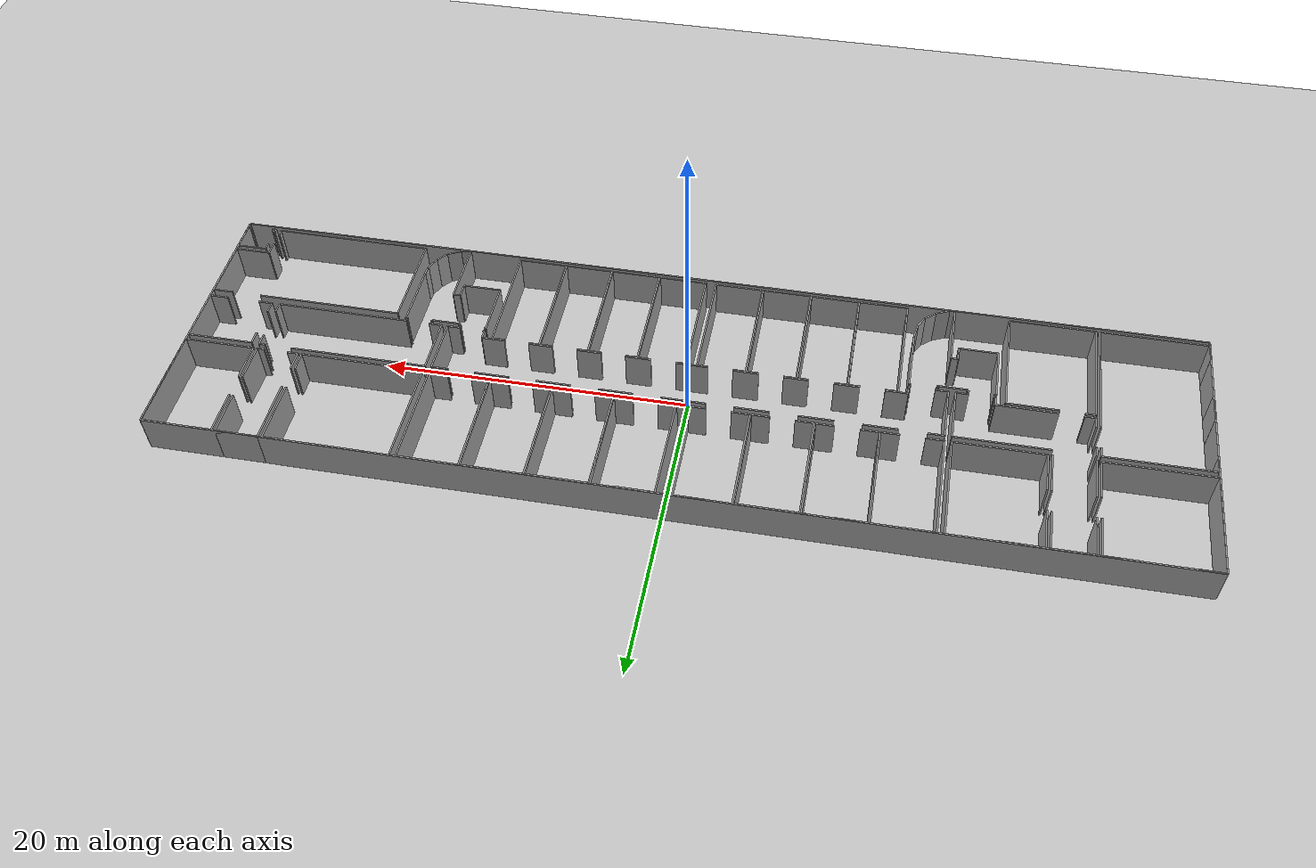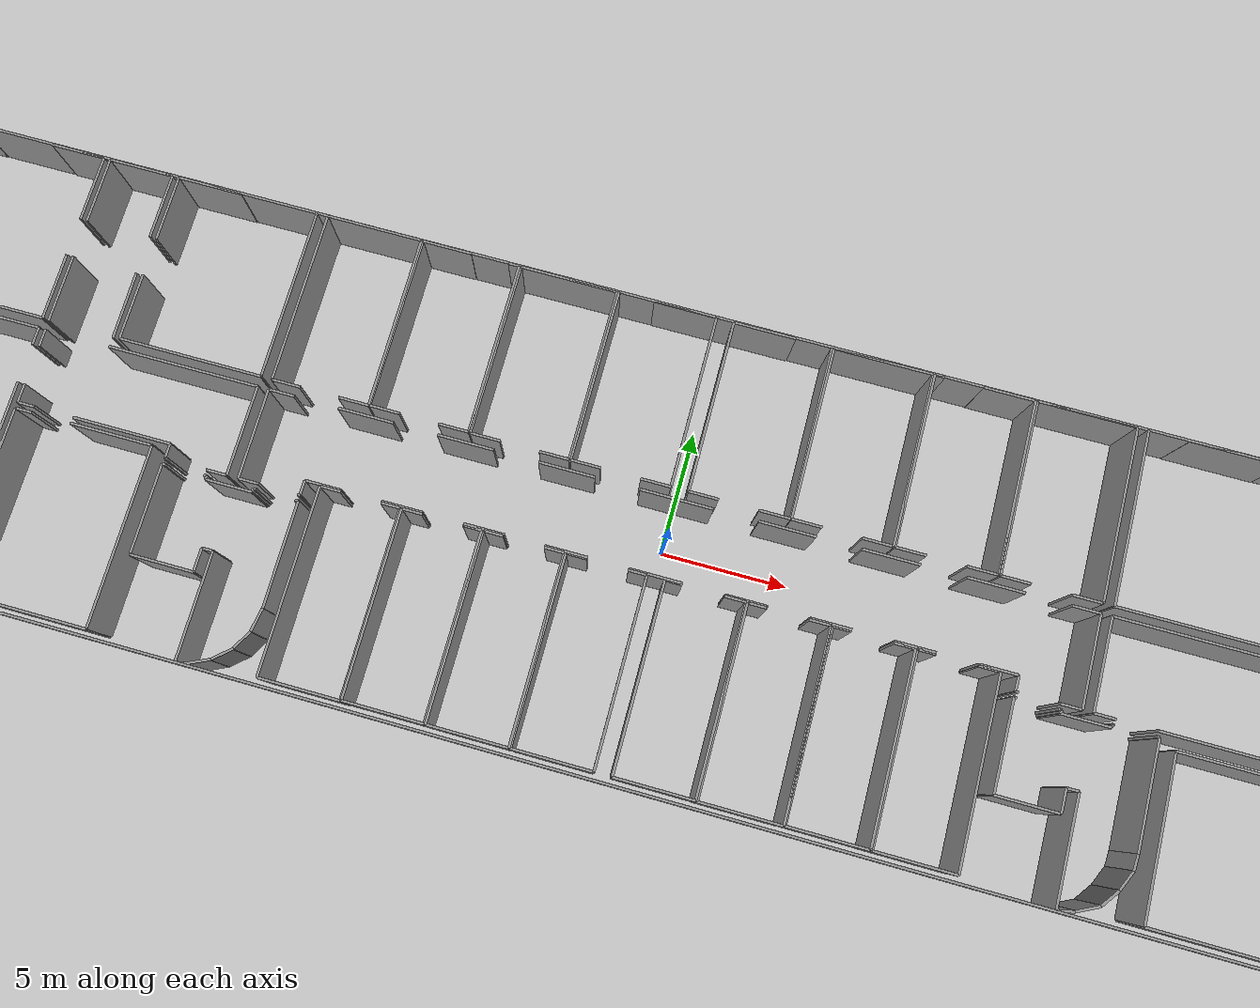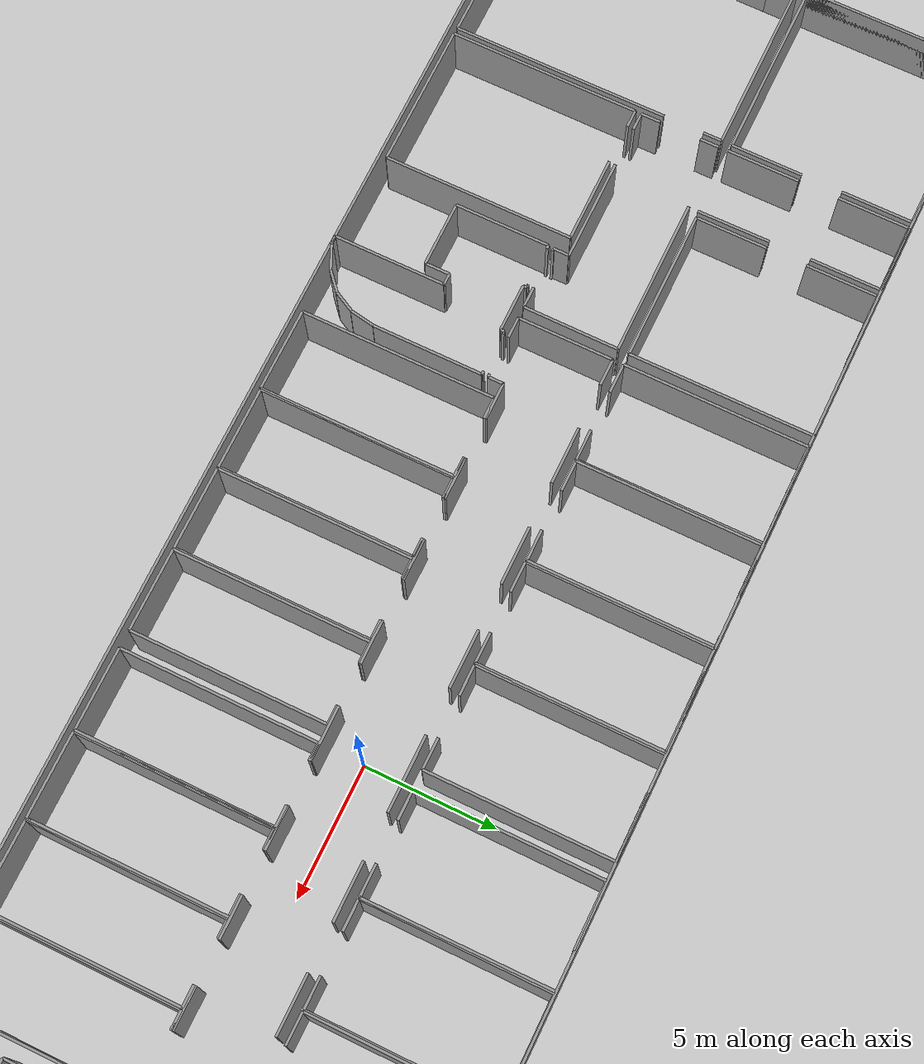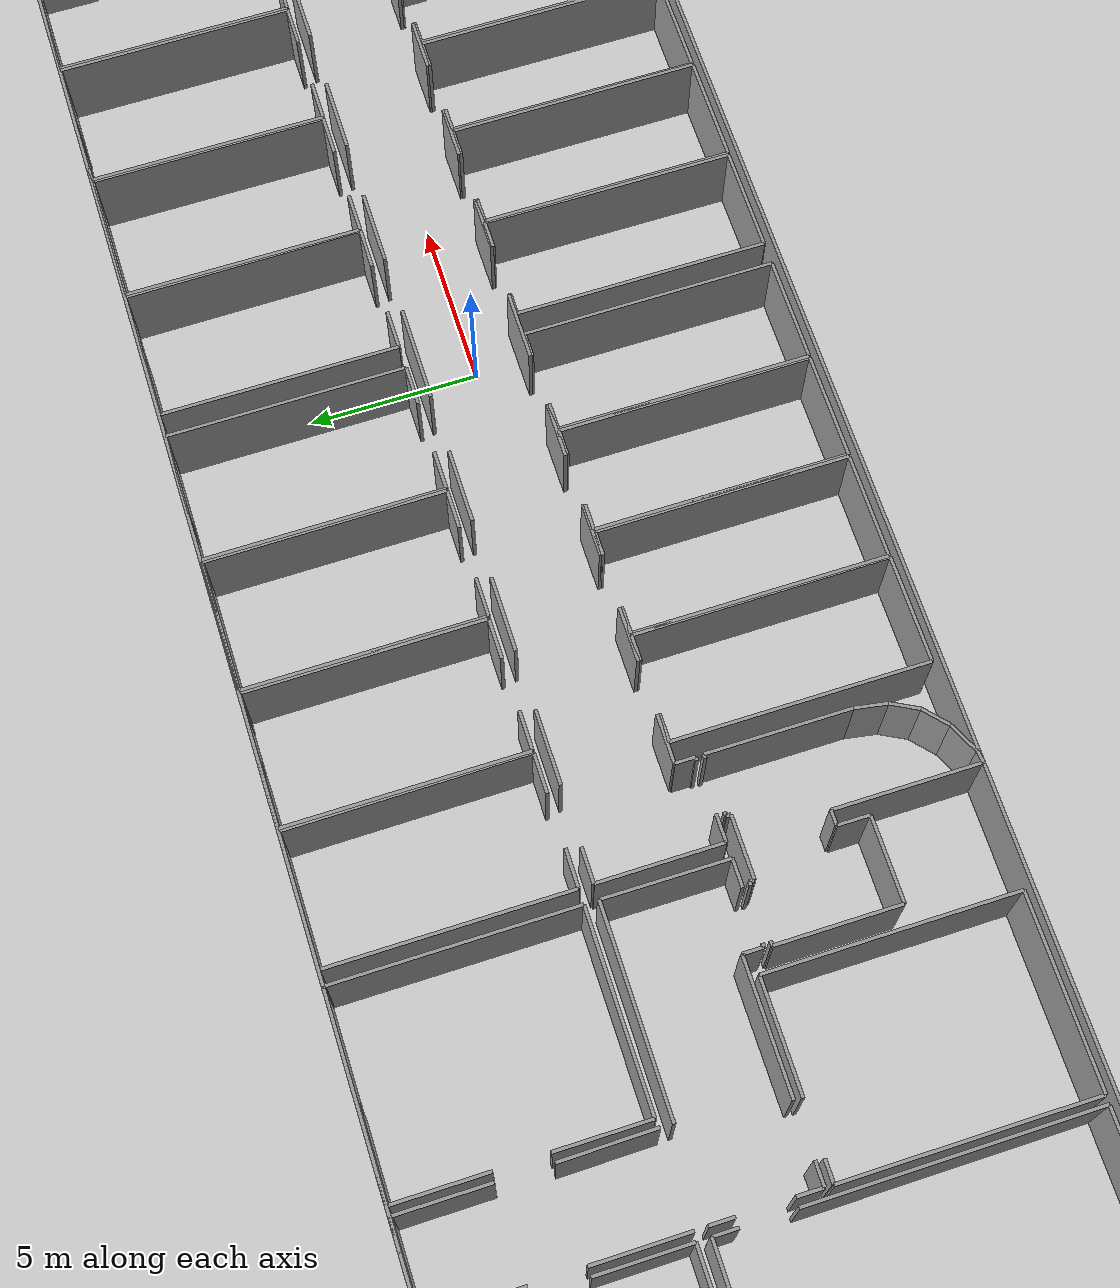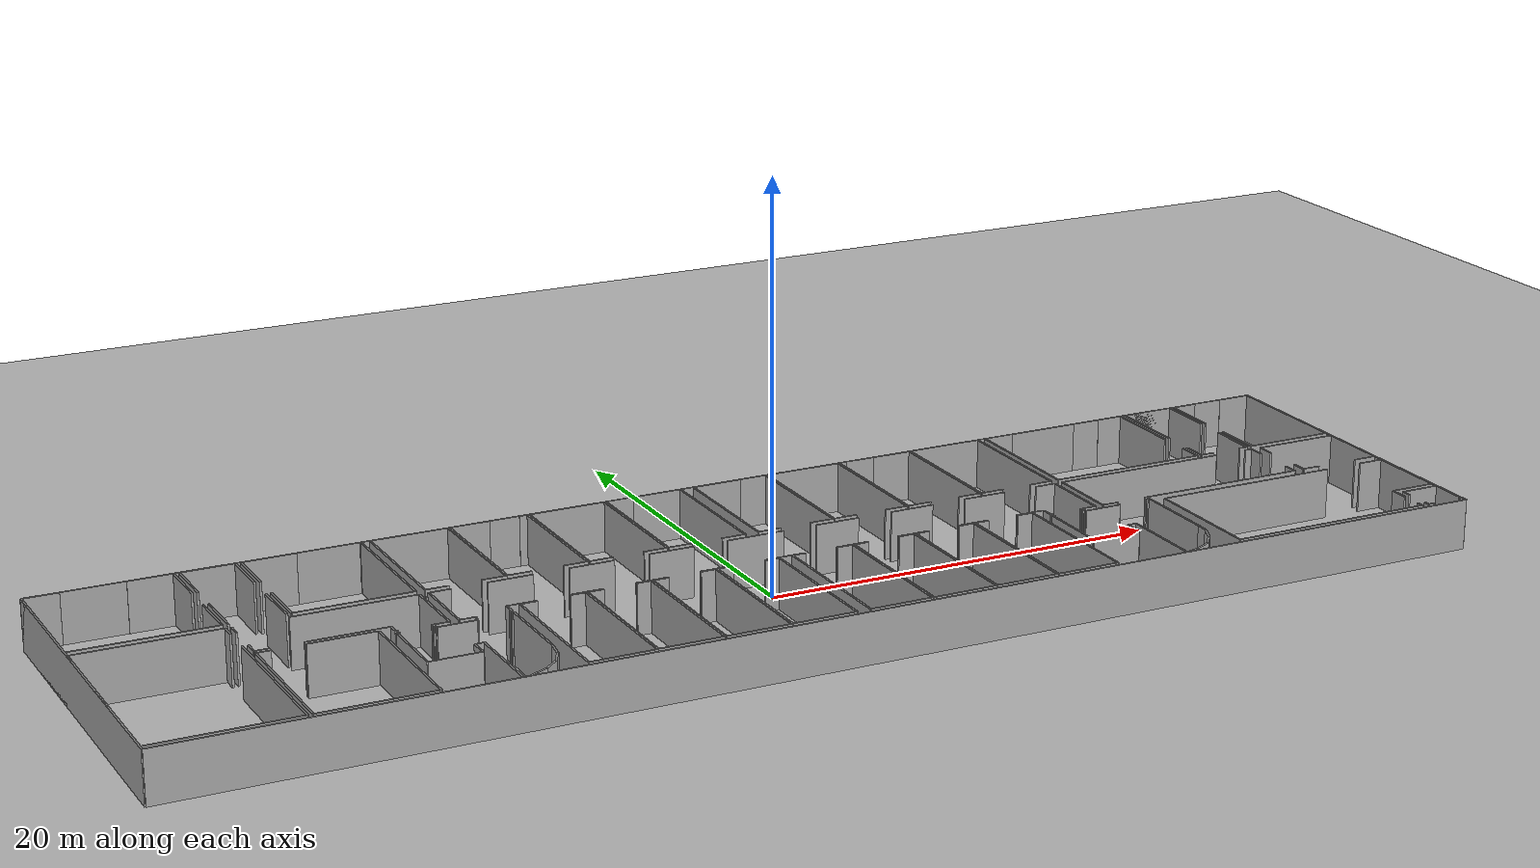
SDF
<sdf version="1.6">
  <world name="default">
    <light name="sun" type="directional">
      <cast_shadows>1</cast_shadows>
      <pose frame="">0 0 10 0 -0 0</pose>
      <diffuse>0.8 0.8 0.8 1</diffuse>
      <specular>0.1 0.1 0.1 1</specular>
      <attenuation>
        <range>1000</range>
        <constant>0.9</constant>
        <linear>0.01</linear>
        <quadratic>0.001</quadratic>
      </attenuation>
      <direction>-0.5 0.5 -1</direction>
    </light>
    <model name="ground_plane">
      <static>1</static>
      <link name="link">
        <collision name="collision">
          <geometry>
            <plane>
              <normal>0 0 1</normal>
              <size>100 100</size>
            </plane>
          </geometry>
          <surface>
            <friction>
              <ode>
                <mu>100</mu>
                <mu2>50</mu2>
              </ode>
              <torsional>
                <ode />
              </torsional>
            </friction>
            <contact>
              <ode />
            </contact>
            <bounce />
          </surface>
          <max_contacts>10</max_contacts>
        </collision>
        <visual name="visual">
          <cast_shadows>0</cast_shadows>
          <geometry>
            <plane>
              <normal>0 0 1</normal>
              <size>100 100</size>
            </plane>
          </geometry>
          <material>
            <script>
              <uri>file://media/materials/scripts/gazebo.material</uri>
              <name>Gazebo/Grey</name>
            </script>
          </material>
        </visual>
        <self_collide>0</self_collide>
        <kinematic>0</kinematic>
        <gravity>1</gravity>
      </link>
    </model>
    <gravity>0 0 -9.8</gravity>
    <magnetic_field>6e-06 2.3e-05 -4.2e-05</magnetic_field>
    <atmosphere type="adiabatic" />
    <physics default="0" name="default_physics" type="ode">
      <max_step_size>0.001</max_step_size>
      <real_time_factor>1</real_time_factor>
      <real_time_update_rate>1000</real_time_update_rate>
    </physics>
    <scene>
      <ambient>0.4 0.4 0.4 1</ambient>
      <background>0.7 0.7 0.7 1</background>
      <shadows>1</shadows>
    </scene>
    <spherical_coordinates>
      <surface_model>EARTH_WGS84</surface_model>
      <latitude_deg>0</latitude_deg>
      <longitude_deg>0</longitude_deg>
      <elevation>0</elevation>
      <heading_deg>0</heading_deg>
    </spherical_coordinates>
  <model name="0510034868_A-40">
		<static>1</static>
		<link name="Wall_0">
			<collision name="Wall_0_Collision">
				<geometry>
					<box>
						<size>6.94066651012 0.1 2.5</size>
					</box>
				</geometry>
				<pose frame="">3.47033325506 0 1.25 0 0 0</pose>
			</collision>
			<visual name="Wall_0_Visual">
				<pose frame="">3.47033325506 0 1.25 0 0 0</pose>
				<geometry>
					<box>
						<size>6.94066651012 0.1 2.5</size>
					</box>
				</geometry>
				<material>
					<script>
						<uri>file://media/materials/scripts/gazebo.material</uri>
						<name>Gazebo/Grey</name>
					</script>
					<ambient>1 1 1 1</ambient>
				</material>
			</visual>
			<pose frame="">6.94066651012 -7.01555528759 0 0 0 3.14159265359</pose>
		</link>
		<link name="Wall_1">
			<collision name="Wall_1_Collision">
				<geometry>
					<box>
						<size>6.99537339671 0.1 2.5</size>
					</box>
				</geometry>
				<pose frame="">3.49768669836 0 1.25 0 0 0</pose>
			</collision>
			<visual name="Wall_1_Visual">
				<pose frame="">3.49768669836 0 1.25 0 0 0</pose>
				<geometry>
					<box>
						<size>6.99537339671 0.1 2.5</size>
					</box>
				</geometry>
				<material>
					<script>
						<uri>file://media/materials/scripts/gazebo.material</uri>
						<name>Gazebo/Grey</name>
					</script>
					<ambient>1 1 1 1</ambient>
				</material>
			</visual>
			<pose frame="">0.0 -7.01555528759 0 0 0 1.57079632679</pose>
		</link>
		<link name="Wall_2">
			<collision name="Wall_2_Collision">
				<geometry>
					<box>
						<size>1.71266826176 0.1 2.5</size>
					</box>
				</geometry>
				<pose frame="">0.856334130878 0 1.25 0 0 0</pose>
			</collision>
			<visual name="Wall_2_Visual">
				<pose frame="">0.856334130878 0 1.25 0 0 0</pose>
				<geometry>
					<box>
						<size>1.71266826176 0.1 2.5</size>
					</box>
				</geometry>
				<material>
					<script>
						<uri>file://media/materials/scripts/gazebo.material</uri>
						<name>Gazebo/Grey</name>
					</script>
					<ambient>1 1 1 1</ambient>
				</material>
			</visual>
			<pose frame="">0.0 -0.0201818908782 0 0 0 0.0</pose>
		</link>
		<link name="Wall_3">
			<collision name="Wall_3_Collision">
				<geometry>
					<box>
						<size>2.17837491353 0.1 2.5</size>
					</box>
				</geometry>
				<pose frame="">1.08918745676 0 1.25 0 0 0</pose>
			</collision>
			<visual name="Wall_3_Visual">
				<pose frame="">1.08918745676 0 1.25 0 0 0</pose>
				<geometry>
					<box>
						<size>2.17837491353 0.1 2.5</size>
					</box>
				</geometry>
				<material>
					<script>
						<uri>file://media/materials/scripts/gazebo.material</uri>
						<name>Gazebo/Grey</name>
					</script>
					<ambient>1 1 1 1</ambient>
				</material>
			</visual>
			<pose frame="">4.75937220357 -0.0201818908782 0 0 0 0.0</pose>
		</link>
		<link name="Wall_4">
			<collision name="Wall_4_Collision">
				<geometry>
					<box>
						<size>2.71782797159 0.1 2.5</size>
					</box>
				</geometry>
				<pose frame="">1.3589139858 0 1.25 0 0 0</pose>
			</collision>
			<visual name="Wall_4_Visual">
				<pose frame="">1.3589139858 0 1.25 0 0 0</pose>
				<geometry>
					<box>
						<size>2.71782797159 0.1 2.5</size>
					</box>
				</geometry>
				<material>
					<script>
						<uri>file://media/materials/scripts/gazebo.material</uri>
						<name>Gazebo/Grey</name>
					</script>
					<ambient>1 1 1 1</ambient>
				</material>
			</visual>
			<pose frame="">6.9377471171 -0.0201818908782 0 0 0 -1.57079632679</pose>
		</link>
		<link name="Wall_5">
			<collision name="Wall_5_Collision">
				<geometry>
					<box>
						<size>2.71986042048 0.1 2.5</size>
					</box>
				</geometry>
				<pose frame="">1.35993021024 0 1.25 0 0 0</pose>
			</collision>
			<visual name="Wall_5_Visual">
				<pose frame="">1.35993021024 0 1.25 0 0 0</pose>
				<geometry>
					<box>
						<size>2.71986042048 0.1 2.5</size>
					</box>
				</geometry>
				<material>
					<script>
						<uri>file://media/materials/scripts/gazebo.material</uri>
						<name>Gazebo/Grey</name>
					</script>
					<ambient>1 1 1 1</ambient>
				</material>
			</visual>
			<pose frame="">6.9377471171 -4.2956964339 0 0 0 -1.56972296525</pose>
		</link>
		<link name="Wall_6">
			<collision name="Wall_6_Collision">
				<geometry>
					<box>
						<size>2.77012318569 0.1 2.5</size>
					</box>
				</geometry>
				<pose frame="">1.38506159285 0 1.25 0 0 0</pose>
			</collision>
			<visual name="Wall_6_Visual">
				<pose frame="">1.38506159285 0 1.25 0 0 0</pose>
				<geometry>
					<box>
						<size>2.77012318569 0.1 2.5</size>
					</box>
				</geometry>
				<material>
					<script>
						<uri>file://media/materials/scripts/gazebo.material</uri>
						<name>Gazebo/Grey</name>
					</script>
					<ambient>1 1 1 1</ambient>
				</material>
			</visual>
			<pose frame="">7.20100020943 -7.06607347985 0 0 0 1.57079632679</pose>
		</link>
		<link name="Wall_7">
			<collision name="Wall_7_Collision">
				<geometry>
					<box>
						<size>2.72607843013 0.1 2.5</size>
					</box>
				</geometry>
				<pose frame="">1.36303921506 0 1.25 0 0 0</pose>
			</collision>
			<visual name="Wall_7_Visual">
				<pose frame="">1.36303921506 0 1.25 0 0 0</pose>
				<geometry>
					<box>
						<size>2.72607843013 0.1 2.5</size>
					</box>
				</geometry>
				<material>
					<script>
						<uri>file://media/materials/scripts/gazebo.material</uri>
						<name>Gazebo/Grey</name>
					</script>
					<ambient>1 1 1 1</ambient>
				</material>
			</visual>
			<pose frame="">7.20100020943 -2.75032208521 0 0 0 1.57079632679</pose>
		</link>
		<link name="Wall_8">
			<collision name="Wall_8_Collision">
				<geometry>
					<box>
						<size>2.62466125521 0.1 2.5</size>
					</box>
				</geometry>
				<pose frame="">1.31233062761 0 1.25 0 0 0</pose>
			</collision>
			<visual name="Wall_8_Visual">
				<pose frame="">1.31233062761 0 1.25 0 0 0</pose>
				<geometry>
					<box>
						<size>2.62466125521 0.1 2.5</size>
					</box>
				</geometry>
				<material>
					<script>
						<uri>file://media/materials/scripts/gazebo.material</uri>
						<name>Gazebo/Grey</name>
					</script>
					<ambient>1 1 1 1</ambient>
				</material>
			</visual>
			<pose frame="">7.20100020943 -0.0242436550801 0 0 0 0.0</pose>
		</link>
		<link name="Wall_9">
			<collision name="Wall_9_Collision">
				<geometry>
					<box>
						<size>2.69206115494 0.1 2.5</size>
					</box>
				</geometry>
				<pose frame="">1.34603057747 0 1.25 0 0 0</pose>
			</collision>
			<visual name="Wall_9_Visual">
				<pose frame="">1.34603057747 0 1.25 0 0 0</pose>
				<geometry>
					<box>
						<size>2.69206115494 0.1 2.5</size>
					</box>
				</geometry>
				<material>
					<script>
						<uri>file://media/materials/scripts/gazebo.material</uri>
						<name>Gazebo/Grey</name>
					</script>
					<ambient>1 1 1 1</ambient>
				</material>
			</visual>
			<pose frame="">9.82566146465 -0.0242436550801 0 0 0 -1.57079632679</pose>
		</link>
		<link name="Wall_10">
			<collision name="Wall_10_Collision">
				<geometry>
					<box>
						<size>2.76565996242 0.1 2.5</size>
					</box>
				</geometry>
				<pose frame="">1.38282998121 0 1.25 0 0 0</pose>
			</collision>
			<visual name="Wall_10_Visual">
				<pose frame="">1.38282998121 0 1.25 0 0 0</pose>
				<geometry>
					<box>
						<size>2.76565996242 0.1 2.5</size>
					</box>
				</geometry>
				<material>
					<script>
						<uri>file://media/materials/scripts/gazebo.material</uri>
						<name>Gazebo/Grey</name>
					</script>
					<ambient>1 1 1 1</ambient>
				</material>
			</visual>
			<pose frame="">9.82566146465 -4.30051977889 0 0 0 -1.56203025797</pose>
		</link>
		<link name="Wall_11">
			<collision name="Wall_11_Collision">
				<geometry>
					<box>
						<size>5.76554735446 0.1 2.5</size>
					</box>
				</geometry>
				<pose frame="">2.88277367723 0 1.25 0 0 0</pose>
			</collision>
			<visual name="Wall_11_Visual">
				<pose frame="">2.88277367723 0 1.25 0 0 0</pose>
				<geometry>
					<box>
						<size>5.76554735446 0.1 2.5</size>
					</box>
				</geometry>
				<material>
					<script>
						<uri>file://media/materials/scripts/gazebo.material</uri>
						<name>Gazebo/Grey</name>
					</script>
					<ambient>1 1 1 1</ambient>
				</material>
			</visual>
			<pose frame="">15.8609353481 -7.01085887273 0 0 0 3.14159265359</pose>
		</link>
		<link name="Wall_12">
			<collision name="Wall_12_Collision">
				<geometry>
					<box>
						<size>2.72582456987 0.1 2.5</size>
					</box>
				</geometry>
				<pose frame="">1.36291228493 0 1.25 0 0 0</pose>
			</collision>
			<visual name="Wall_12_Visual">
				<pose frame="">1.36291228493 0 1.25 0 0 0</pose>
				<geometry>
					<box>
						<size>2.72582456987 0.1 2.5</size>
					</box>
				</geometry>
				<material>
					<script>
						<uri>file://media/materials/scripts/gazebo.material</uri>
						<name>Gazebo/Grey</name>
					</script>
					<ambient>1 1 1 1</ambient>
				</material>
			</visual>
			<pose frame="">10.0953879937 -7.01085887273 0 0 0 1.57079632679</pose>
		</link>
		<link name="Wall_13">
			<collision name="Wall_13_Collision">
				<geometry>
					<box>
						<size>2.73255186682 0.1 2.5</size>
					</box>
				</geometry>
				<pose frame="">1.36627593341 0 1.25 0 0 0</pose>
			</collision>
			<visual name="Wall_13_Visual">
				<pose frame="">1.36627593341 0 1.25 0 0 0</pose>
				<geometry>
					<box>
						<size>2.73255186682 0.1 2.5</size>
					</box>
				</geometry>
				<material>
					<script>
						<uri>file://media/materials/scripts/gazebo.material</uri>
						<name>Gazebo/Grey</name>
					</script>
					<ambient>1 1 1 1</ambient>
				</material>
			</visual>
			<pose frame="">10.0953879937 -2.75590701099 0 0 0 1.57079632679</pose>
		</link>
		<link name="Wall_14">
			<collision name="Wall_14_Collision">
				<geometry>
					<box>
						<size>2.63481566572 0.1 2.5</size>
					</box>
				</geometry>
				<pose frame="">1.31740783286 0 1.25 0 0 0</pose>
			</collision>
			<visual name="Wall_14_Visual">
				<pose frame="">1.31740783286 0 1.25 0 0 0</pose>
				<geometry>
					<box>
						<size>2.63481566572 0.1 2.5</size>
					</box>
				</geometry>
				<material>
					<script>
						<uri>file://media/materials/scripts/gazebo.material</uri>
						<name>Gazebo/Grey</name>
					</script>
					<ambient>1 1 1 1</ambient>
				</material>
			</visual>
			<pose frame="">10.0953879937 -0.0233551441609 0 0 0 0.0</pose>
		</link>
		<link name="Wall_15">
			<collision name="Wall_15_Collision">
				<geometry>
					<box>
						<size>0.0746349172098 0.1 2.5</size>
					</box>
				</geometry>
				<pose frame="">0.0373174586049 0 1.25 0 0 0</pose>
			</collision>
			<visual name="Wall_15_Visual">
				<pose frame="">0.0373174586049 0 1.25 0 0 0</pose>
				<geometry>
					<box>
						<size>0.0746349172098 0.1 2.5</size>
					</box>
				</geometry>
				<material>
					<script>
						<uri>file://media/materials/scripts/gazebo.material</uri>
						<name>Gazebo/Grey</name>
					</script>
					<ambient>1 1 1 1</ambient>
				</material>
			</visual>
			<pose frame="">15.7800808545 -0.0233551441609 0 0 0 0.0</pose>
		</link>
		<link name="Wall_16">
			<collision name="Wall_16_Collision">
				<geometry>
					<box>
						<size>6.98750649659 0.1 2.5</size>
					</box>
				</geometry>
				<pose frame="">3.4937532483 0 1.25 0 0 0</pose>
			</collision>
			<visual name="Wall_16_Visual">
				<pose frame="">3.4937532483 0 1.25 0 0 0</pose>
				<geometry>
					<box>
						<size>6.98750649659 0.1 2.5</size>
					</box>
				</geometry>
				<material>
					<script>
						<uri>file://media/materials/scripts/gazebo.material</uri>
						<name>Gazebo/Grey</name>
					</script>
					<ambient>1 1 1 1</ambient>
				</material>
			</visual>
			<pose frame="">15.8547157717 -0.0233551441609 0 0 0 -1.56990622712</pose>
		</link>
		<link name="Wall_17">
			<collision name="Wall_17_Collision">
				<geometry>
					<box>
						<size>0.821491809833 0.1 2.5</size>
					</box>
				</geometry>
				<pose frame="">0.410745904917 0 1.25 0 0 0</pose>
			</collision>
			<visual name="Wall_17_Visual">
				<pose frame="">0.410745904917 0 1.25 0 0 0</pose>
				<geometry>
					<box>
						<size>0.821491809833 0.1 2.5</size>
					</box>
				</geometry>
				<material>
					<script>
						<uri>file://media/materials/scripts/gazebo.material</uri>
						<name>Gazebo/Grey</name>
					</script>
					<ambient>1 1 1 1</ambient>
				</material>
			</visual>
			<pose frame="">15.8516694486 -11.0769386991 0 0 0 3.14159265359</pose>
		</link>
		<link name="Wall_18">
			<collision name="Wall_18_Collision">
				<geometry>
					<box>
						<size>0.104336567936 0.1 2.5</size>
					</box>
				</geometry>
				<pose frame="">0.0521682839681 0 1.25 0 0 0</pose>
			</collision>
			<visual name="Wall_18_Visual">
				<pose frame="">0.0521682839681 0 1.25 0 0 0</pose>
				<geometry>
					<box>
						<size>0.104336567936 0.1 2.5</size>
					</box>
				</geometry>
				<material>
					<script>
						<uri>file://media/materials/scripts/gazebo.material</uri>
						<name>Gazebo/Grey</name>
					</script>
					<ambient>1 1 1 1</ambient>
				</material>
			</visual>
			<pose frame="">13.4882304036 -11.0769386991 0 0 0 3.14159265359</pose>
		</link>
		<link name="Wall_19">
			<collision name="Wall_19_Collision">
				<geometry>
					<box>
						<size>0.596444687022 0.1 2.5</size>
					</box>
				</geometry>
				<pose frame="">0.298222343511 0 1.25 0 0 0</pose>
			</collision>
			<visual name="Wall_19_Visual">
				<pose frame="">0.298222343511 0 1.25 0 0 0</pose>
				<geometry>
					<box>
						<size>0.596444687022 0.1 2.5</size>
					</box>
				</geometry>
				<material>
					<script>
						<uri>file://media/materials/scripts/gazebo.material</uri>
						<name>Gazebo/Grey</name>
					</script>
					<ambient>1 1 1 1</ambient>
				</material>
			</visual>
			<pose frame="">13.3838938356 -11.0769386991 0 0 0 1.57079632679</pose>
		</link>
		<link name="Wall_20">
			<collision name="Wall_20_Collision">
				<geometry>
					<box>
						<size>3.9235372889 0.1 2.5</size>
					</box>
				</geometry>
				<pose frame="">1.96176864445 0 1.25 0 0 0</pose>
			</collision>
			<visual name="Wall_20_Visual">
				<pose frame="">1.96176864445 0 1.25 0 0 0</pose>
				<geometry>
					<box>
						<size>3.9235372889 0.1 2.5</size>
					</box>
				</geometry>
				<material>
					<script>
						<uri>file://media/materials/scripts/gazebo.material</uri>
						<name>Gazebo/Grey</name>
					</script>
					<ambient>1 1 1 1</ambient>
				</material>
			</visual>
			<pose frame="">13.3838938356 -10.4804940121 0 0 0 3.14159265359</pose>
		</link>
		<link name="Wall_21">
			<collision name="Wall_21_Collision">
				<geometry>
					<box>
						<size>0.692784656686 0.1 2.5</size>
					</box>
				</geometry>
				<pose frame="">0.346392328343 0 1.25 0 0 0</pose>
			</collision>
			<visual name="Wall_21_Visual">
				<pose frame="">0.346392328343 0 1.25 0 0 0</pose>
				<geometry>
					<box>
						<size>0.692784656686 0.1 2.5</size>
					</box>
				</geometry>
				<material>
					<script>
						<uri>file://media/materials/scripts/gazebo.material</uri>
						<name>Gazebo/Grey</name>
					</script>
					<ambient>1 1 1 1</ambient>
				</material>
			</visual>
			<pose frame="">7.90647787925 -10.4804940121 0 0 0 3.14159265359</pose>
		</link>
		<link name="Wall_22">
			<collision name="Wall_22_Collision">
				<geometry>
					<box>
						<size>0.755615071684 0.1 2.5</size>
					</box>
				</geometry>
				<pose frame="">0.377807535842 0 1.25 0 0 0</pose>
			</collision>
			<visual name="Wall_22_Visual">
				<pose frame="">0.377807535842 0 1.25 0 0 0</pose>
				<geometry>
					<box>
						<size>0.755615071684 0.1 2.5</size>
					</box>
				</geometry>
				<material>
					<script>
						<uri>file://media/materials/scripts/gazebo.material</uri>
						<name>Gazebo/Grey</name>
					</script>
					<ambient>1 1 1 1</ambient>
				</material>
			</visual>
			<pose frame="">7.21369322257 -10.4804940121 0 0 0 1.57079632679</pose>
		</link>
		<link name="Wall_23">
			<collision name="Wall_23_Collision">
				<geometry>
					<box>
						<size>0.713728128352 0.1 2.5</size>
					</box>
				</geometry>
				<pose frame="">0.356864064176 0 1.25 0 0 0</pose>
			</collision>
			<visual name="Wall_23_Visual">
				<pose frame="">0.356864064176 0 1.25 0 0 0</pose>
				<geometry>
					<box>
						<size>0.713728128352 0.1 2.5</size>
					</box>
				</geometry>
				<material>
					<script>
						<uri>file://media/materials/scripts/gazebo.material</uri>
						<name>Gazebo/Grey</name>
					</script>
					<ambient>1 1 1 1</ambient>
				</material>
			</visual>
			<pose frame="">7.21369322257 -8.14167941257 0 0 0 1.57079632679</pose>
		</link>
		<link name="Wall_24">
			<collision name="Wall_24_Collision">
				<geometry>
					<box>
						<size>6.04657066518 0.1 2.5</size>
					</box>
				</geometry>
				<pose frame="">3.02328533259 0 1.25 0 0 0</pose>
			</collision>
			<visual name="Wall_24_Visual">
				<pose frame="">3.02328533259 0 1.25 0 0 0</pose>
				<geometry>
					<box>
						<size>6.04657066518 0.1 2.5</size>
					</box>
				</geometry>
				<material>
					<script>
						<uri>file://media/materials/scripts/gazebo.material</uri>
						<name>Gazebo/Grey</name>
					</script>
					<ambient>1 1 1 1</ambient>
				</material>
			</visual>
			<pose frame="">9.81893416769 -7.42795128422 0 0 0 0.0</pose>
		</link>
		<link name="Wall_25">
			<collision name="Wall_25_Collision">
				<geometry>
					<box>
						<size>3.64901364368 0.1 2.5</size>
					</box>
				</geometry>
				<pose frame="">1.82450682184 0 1.25 0 0 0</pose>
			</collision>
			<visual name="Wall_25_Visual">
				<pose frame="">1.82450682184 0 1.25 0 0 0</pose>
				<geometry>
					<box>
						<size>3.64901364368 0.1 2.5</size>
					</box>
				</geometry>
				<material>
					<script>
						<uri>file://media/materials/scripts/gazebo.material</uri>
						<name>Gazebo/Grey</name>
					</script>
					<ambient>1 1 1 1</ambient>
				</material>
			</visual>
			<pose frame="">15.8655048329 -7.42795128422 0 0 0 -1.57458787673</pose>
		</link>
		<link name="Wall_26">
			<collision name="Wall_26_Collision">
				<geometry>
					<box>
						<size>6.95399417391 0.1 2.5</size>
					</box>
				</geometry>
				<pose frame="">3.47699708695 0 1.25 0 0 0</pose>
			</collision>
			<visual name="Wall_26_Visual">
				<pose frame="">3.47699708695 0 1.25 0 0 0</pose>
				<geometry>
					<box>
						<size>6.95399417391 0.1 2.5</size>
					</box>
				</geometry>
				<material>
					<script>
						<uri>file://media/materials/scripts/gazebo.material</uri>
						<name>Gazebo/Grey</name>
					</script>
					<ambient>1 1 1 1</ambient>
				</material>
			</visual>
			<pose frame="">6.95691356693 -17.9909498816 0 0 0 3.14159265359</pose>
		</link>
		<link name="Wall_27">
			<collision name="Wall_27_Collision">
				<geometry>
					<box>
						<size>1.31385378918 0.1 2.5</size>
					</box>
				</geometry>
				<pose frame="">0.656926894591 0 1.25 0 0 0</pose>
			</collision>
			<visual name="Wall_27_Visual">
				<pose frame="">0.656926894591 0 1.25 0 0 0</pose>
				<geometry>
					<box>
						<size>1.31385378918 0.1 2.5</size>
					</box>
				</geometry>
				<material>
					<script>
						<uri>file://media/materials/scripts/gazebo.material</uri>
						<name>Gazebo/Grey</name>
					</script>
					<ambient>1 1 1 1</ambient>
				</material>
			</visual>
			<pose frame="">0.00291939302011 -17.9909498816 0 0 0 1.57079632679</pose>
		</link>
		<link name="Wall_28">
			<collision name="Wall_28_Collision">
				<geometry>
					<box>
						<size>2.02237778215 0.1 2.5</size>
					</box>
				</geometry>
				<pose frame="">1.01118889107 0 1.25 0 0 0</pose>
			</collision>
			<visual name="Wall_28_Visual">
				<pose frame="">1.01118889107 0 1.25 0 0 0</pose>
				<geometry>
					<box>
						<size>2.02237778215 0.1 2.5</size>
					</box>
				</geometry>
				<material>
					<script>
						<uri>file://media/materials/scripts/gazebo.material</uri>
						<name>Gazebo/Grey</name>
					</script>
					<ambient>1 1 1 1</ambient>
				</material>
			</visual>
			<pose frame="">0.00291939302011 -13.6057677052 0 0 0 1.57079632679</pose>
		</link>
		<link name="Wall_29">
			<collision name="Wall_29_Collision">
				<geometry>
					<box>
						<size>1.07014793707 0.1 2.5</size>
					</box>
				</geometry>
				<pose frame="">0.535073968534 0 1.25 0 0 0</pose>
			</collision>
			<visual name="Wall_29_Visual">
				<pose frame="">0.535073968534 0 1.25 0 0 0</pose>
				<geometry>
					<box>
						<size>1.07014793707 0.1 2.5</size>
					</box>
				</geometry>
				<material>
					<script>
						<uri>file://media/materials/scripts/gazebo.material</uri>
						<name>Gazebo/Grey</name>
					</script>
					<ambient>1 1 1 1</ambient>
				</material>
			</visual>
			<pose frame="">0.00291939302011 -8.49949545273 0 0 0 1.57079632679</pose>
		</link>
		<link name="Wall_30">
			<collision name="Wall_30_Collision">
				<geometry>
					<box>
						<size>6.93863562802 0.1 2.5</size>
					</box>
				</geometry>
				<pose frame="">3.46931781401 0 1.25 0 0 0</pose>
			</collision>
			<visual name="Wall_30_Visual">
				<pose frame="">3.46931781401 0 1.25 0 0 0</pose>
				<geometry>
					<box>
						<size>6.93863562802 0.1 2.5</size>
					</box>
				</geometry>
				<material>
					<script>
						<uri>file://media/materials/scripts/gazebo.material</uri>
						<name>Gazebo/Grey</name>
					</script>
					<ambient>1 1 1 1</ambient>
				</material>
			</visual>
			<pose frame="">0.00291939302011 -7.42934751566 0 0 0 0.0</pose>
		</link>
		<link name="Wall_31">
			<collision name="Wall_31_Collision">
				<geometry>
					<box>
						<size>0.717282172028 0.1 2.5</size>
					</box>
				</geometry>
				<pose frame="">0.358641086014 0 1.25 0 0 0</pose>
			</collision>
			<visual name="Wall_31_Visual">
				<pose frame="">0.358641086014 0 1.25 0 0 0</pose>
				<geometry>
					<box>
						<size>0.717282172028 0.1 2.5</size>
					</box>
				</geometry>
				<material>
					<script>
						<uri>file://media/materials/scripts/gazebo.material</uri>
						<name>Gazebo/Grey</name>
					</script>
					<ambient>1 1 1 1</ambient>
				</material>
			</visual>
			<pose frame="">6.94155502104 -7.42934751566 0 0 0 -1.57079632679</pose>
		</link>
		<link name="Wall_32">
			<collision name="Wall_32_Collision">
				<geometry>
					<box>
						<size>8.28398232719 0.1 2.5</size>
					</box>
				</geometry>
				<pose frame="">4.14199116359 0 1.25 0 0 0</pose>
			</collision>
			<visual name="Wall_32_Visual">
				<pose frame="">4.14199116359 0 1.25 0 0 0</pose>
				<geometry>
					<box>
						<size>8.28398232719 0.1 2.5</size>
					</box>
				</geometry>
				<material>
					<script>
						<uri>file://media/materials/scripts/gazebo.material</uri>
						<name>Gazebo/Grey</name>
					</script>
					<ambient>1 1 1 1</ambient>
				</material>
			</visual>
			<pose frame="">6.94155502104 -9.70698179187 0 0 0 -1.56894232058</pose>
		</link>
		<link name="Wall_33">
			<collision name="Wall_33_Collision">
				<geometry>
					<box>
						<size>5.54164260283 0.1 2.5</size>
					</box>
				</geometry>
				<pose frame="">2.77082130141 0 1.25 0 0 0</pose>
			</collision>
			<visual name="Wall_33_Visual">
				<pose frame="">2.77082130141 0 1.25 0 0 0</pose>
				<geometry>
					<box>
						<size>5.54164260283 0.1 2.5</size>
					</box>
				</geometry>
				<material>
					<script>
						<uri>file://media/materials/scripts/gazebo.material</uri>
						<name>Gazebo/Grey</name>
					</script>
					<ambient>1 1 1 1</ambient>
				</material>
			</visual>
			<pose frame="">12.7470853669 -18.0040236852 0 0 0 3.14159265359</pose>
		</link>
		<link name="Wall_34">
			<collision name="Wall_34_Collision">
				<geometry>
					<box>
						<size>7.28122005242 0.1 2.5</size>
					</box>
				</geometry>
				<pose frame="">3.64061002621 0 1.25 0 0 0</pose>
			</collision>
			<visual name="Wall_34_Visual">
				<pose frame="">3.64061002621 0 1.25 0 0 0</pose>
				<geometry>
					<box>
						<size>7.28122005242 0.1 2.5</size>
					</box>
				</geometry>
				<material>
					<script>
						<uri>file://media/materials/scripts/gazebo.material</uri>
						<name>Gazebo/Grey</name>
					</script>
					<ambient>1 1 1 1</ambient>
				</material>
			</visual>
			<pose frame="">7.20544276403 -18.0040236852 0 0 0 1.57079632679</pose>
		</link>
		<link name="Wall_35">
			<collision name="Wall_35_Collision">
				<geometry>
					<box>
						<size>0.677806901191 0.1 2.5</size>
					</box>
				</geometry>
				<pose frame="">0.338903450596 0 1.25 0 0 0</pose>
			</collision>
			<visual name="Wall_35_Visual">
				<pose frame="">0.338903450596 0 1.25 0 0 0</pose>
				<geometry>
					<box>
						<size>0.677806901191 0.1 2.5</size>
					</box>
				</geometry>
				<material>
					<script>
						<uri>file://media/materials/scripts/gazebo.material</uri>
						<name>Gazebo/Grey</name>
					</script>
					<ambient>1 1 1 1</ambient>
				</material>
			</visual>
			<pose frame="">7.20544276403 -10.7228036327 0 0 0 0.0</pose>
		</link>
		<link name="Wall_36">
			<collision name="Wall_36_Collision">
				<geometry>
					<box>
						<size>3.29815253194 0.1 2.5</size>
					</box>
				</geometry>
				<pose frame="">1.64907626597 0 1.25 0 0 0</pose>
			</collision>
			<visual name="Wall_36_Visual">
				<pose frame="">1.64907626597 0 1.25 0 0 0</pose>
				<geometry>
					<box>
						<size>3.29815253194 0.1 2.5</size>
					</box>
				</geometry>
				<material>
					<script>
						<uri>file://media/materials/scripts/gazebo.material</uri>
						<name>Gazebo/Grey</name>
					</script>
					<ambient>1 1 1 1</ambient>
				</material>
			</visual>
			<pose frame="">9.44207860783 -10.7228036327 0 0 0 0.0</pose>
		</link>
		<link name="Wall_37">
			<collision name="Wall_37_Collision">
				<geometry>
					<box>
						<size>7.28122327856 0.1 2.5</size>
					</box>
				</geometry>
				<pose frame="">3.64061163928 0 1.25 0 0 0</pose>
			</collision>
			<visual name="Wall_37_Visual">
				<pose frame="">3.64061163928 0 1.25 0 0 0</pose>
				<geometry>
					<box>
						<size>7.28122327856 0.1 2.5</size>
					</box>
				</geometry>
				<material>
					<script>
						<uri>file://media/materials/scripts/gazebo.material</uri>
						<name>Gazebo/Grey</name>
					</script>
					<ambient>1 1 1 1</ambient>
				</material>
			</visual>
			<pose frame="">12.7402311398 -10.7228036327 0 0 0 -1.56985497012</pose>
		</link>
		<link name="Wall_38">
			<collision name="Wall_38_Collision">
				<geometry>
					<box>
						<size>4.2997581981 0.1 2.5</size>
					</box>
				</geometry>
				<pose frame="">2.14987909905 0 1.25 0 0 0</pose>
			</collision>
			<visual name="Wall_38_Visual">
				<pose frame="">2.14987909905 0 1.25 0 0 0</pose>
				<geometry>
					<box>
						<size>4.2997581981 0.1 2.5</size>
					</box>
				</geometry>
				<material>
					<script>
						<uri>file://media/materials/scripts/gazebo.material</uri>
						<name>Gazebo/Grey</name>
					</script>
					<ambient>1 1 1 1</ambient>
				</material>
			</visual>
			<pose frame="">16.2973211396 -18.2769234675 0 0 0 1.57079632679</pose>
		</link>
		<link name="Wall_39">
			<collision name="Wall_39_Collision">
				<geometry>
					<box>
						<size>0.438289743411 0.1 2.5</size>
					</box>
				</geometry>
				<pose frame="">0.219144871705 0 1.25 0 0 0</pose>
			</collision>
			<visual name="Wall_39_Visual">
				<pose frame="">0.219144871705 0 1.25 0 0 0</pose>
				<geometry>
					<box>
						<size>0.438289743411 0.1 2.5</size>
					</box>
				</geometry>
				<material>
					<script>
						<uri>file://media/materials/scripts/gazebo.material</uri>
						<name>Gazebo/Grey</name>
					</script>
					<ambient>1 1 1 1</ambient>
				</material>
			</visual>
			<pose frame="">16.2973211396 -13.9771652694 0 0 0 3.14159265359</pose>
		</link>
		<link name="Wall_40">
			<collision name="Wall_40_Collision">
				<geometry>
					<box>
						<size>0.947660360355 0.1 2.5</size>
					</box>
				</geometry>
				<pose frame="">0.473830180177 0 1.25 0 0 0</pose>
			</collision>
			<visual name="Wall_40_Visual">
				<pose frame="">0.473830180177 0 1.25 0 0 0</pose>
				<geometry>
					<box>
						<size>0.947660360355 0.1 2.5</size>
					</box>
				</geometry>
				<material>
					<script>
						<uri>file://media/materials/scripts/gazebo.material</uri>
						<name>Gazebo/Grey</name>
					</script>
					<ambient>1 1 1 1</ambient>
				</material>
			</visual>
			<pose frame="">15.8590313962 -13.9771652694 0 0 0 -1.57079632679</pose>
		</link>
		<link name="Wall_41">
			<collision name="Wall_41_Collision">
				<geometry>
					<box>
						<size>2.51105878769 0.1 2.5</size>
					</box>
				</geometry>
				<pose frame="">1.25552939385 0 1.25 0 0 0</pose>
			</collision>
			<visual name="Wall_41_Visual">
				<pose frame="">1.25552939385 0 1.25 0 0 0</pose>
				<geometry>
					<box>
						<size>2.51105878769 0.1 2.5</size>
					</box>
				</geometry>
				<material>
					<script>
						<uri>file://media/materials/scripts/gazebo.material</uri>
						<name>Gazebo/Grey</name>
					</script>
					<ambient>1 1 1 1</ambient>
				</material>
			</visual>
			<pose frame="">15.8590313962 -14.9248256297 0 0 0 3.14159265359</pose>
		</link>
		<link name="Wall_42">
			<collision name="Wall_42_Collision">
				<geometry>
					<box>
						<size>3.62893245413 0.1 2.5</size>
					</box>
				</geometry>
				<pose frame="">1.81446622707 0 1.25 0 0 0</pose>
			</collision>
			<visual name="Wall_42_Visual">
				<pose frame="">1.81446622707 0 1.25 0 0 0</pose>
				<geometry>
					<box>
						<size>3.62893245413 0.1 2.5</size>
					</box>
				</geometry>
				<material>
					<script>
						<uri>file://media/materials/scripts/gazebo.material</uri>
						<name>Gazebo/Grey</name>
					</script>
					<ambient>1 1 1 1</ambient>
				</material>
			</visual>
			<pose frame="">13.3479726085 -14.9248256297 0 0 0 1.57079632679</pose>
		</link>
		<link name="Wall_43">
			<collision name="Wall_43_Collision">
				<geometry>
					<box>
						<size>0.136576821289 0.1 2.5</size>
					</box>
				</geometry>
				<pose frame="">0.0682884106444 0 1.25 0 0 0</pose>
			</collision>
			<visual name="Wall_43_Visual">
				<pose frame="">0.0682884106444 0 1.25 0 0 0</pose>
				<geometry>
					<box>
						<size>0.136576821289 0.1 2.5</size>
					</box>
				</geometry>
				<material>
					<script>
						<uri>file://media/materials/scripts/gazebo.material</uri>
						<name>Gazebo/Grey</name>
					</script>
					<ambient>1 1 1 1</ambient>
				</material>
			</visual>
			<pose frame="">13.3479726085 -11.2958931756 0 0 0 0.0</pose>
		</link>
		<link name="Wall_44">
			<collision name="Wall_44_Collision">
				<geometry>
					<box>
						<size>0.116014140017 0.1 2.5</size>
					</box>
				</geometry>
				<pose frame="">0.0580070700083 0 1.25 0 0 0</pose>
			</collision>
			<visual name="Wall_44_Visual">
				<pose frame="">0.0580070700083 0 1.25 0 0 0</pose>
				<geometry>
					<box>
						<size>0.116014140017 0.1 2.5</size>
					</box>
				</geometry>
				<material>
					<script>
						<uri>file://media/materials/scripts/gazebo.material</uri>
						<name>Gazebo/Grey</name>
					</script>
					<ambient>1 1 1 1</ambient>
				</material>
			</visual>
			<pose frame="">15.0173576955 -11.2958931756 0 0 0 0.0</pose>
		</link>
		<link name="Wall_45">
			<collision name="Wall_45_Collision">
				<geometry>
					<box>
						<size>0.139496214309 0.1 2.5</size>
					</box>
				</geometry>
				<pose frame="">0.0697481071544 0 1.25 0 0 0</pose>
			</collision>
			<visual name="Wall_45_Visual">
				<pose frame="">0.0697481071544 0 1.25 0 0 0</pose>
				<geometry>
					<box>
						<size>0.139496214309 0.1 2.5</size>
					</box>
				</geometry>
				<material>
					<script>
						<uri>file://media/materials/scripts/gazebo.material</uri>
						<name>Gazebo/Grey</name>
					</script>
					<ambient>1 1 1 1</ambient>
				</material>
			</visual>
			<pose frame="">15.1333718355 -11.2958931756 0 0 0 -1.57079632679</pose>
		</link>
		<link name="Wall_46">
			<collision name="Wall_46_Collision">
				<geometry>
					<box>
						<size>1.85330684725 0.1 2.5</size>
					</box>
				</geometry>
				<pose frame="">0.926653423623 0 1.25 0 0 0</pose>
			</collision>
			<visual name="Wall_46_Visual">
				<pose frame="">0.926653423623 0 1.25 0 0 0</pose>
				<geometry>
					<box>
						<size>1.85330684725 0.1 2.5</size>
					</box>
				</geometry>
				<material>
					<script>
						<uri>file://media/materials/scripts/gazebo.material</uri>
						<name>Gazebo/Grey</name>
					</script>
					<ambient>1 1 1 1</ambient>
				</material>
			</visual>
			<pose frame="">15.1333718355 -11.4353893899 0 0 0 0.0</pose>
		</link>
		<link name="Wall_47">
			<collision name="Wall_47_Collision">
				<geometry>
					<box>
						<size>0.137846122602 0.1 2.5</size>
					</box>
				</geometry>
				<pose frame="">0.0689230613009 0 1.25 0 0 0</pose>
			</collision>
			<visual name="Wall_47_Visual">
				<pose frame="">0.0689230613009 0 1.25 0 0 0</pose>
				<geometry>
					<box>
						<size>0.137846122602 0.1 2.5</size>
					</box>
				</geometry>
				<material>
					<script>
						<uri>file://media/materials/scripts/gazebo.material</uri>
						<name>Gazebo/Grey</name>
					</script>
					<ambient>1 1 1 1</ambient>
				</material>
			</visual>
			<pose frame="">16.9866786827 -11.4353893899 0 0 0 1.57079632679</pose>
		</link>
		<link name="Wall_48">
			<collision name="Wall_48_Collision">
				<geometry>
					<box>
						<size>0.114617908572 0.1 2.5</size>
					</box>
				</geometry>
				<pose frame="">0.0573089542861 0 1.25 0 0 0</pose>
			</collision>
			<visual name="Wall_48_Visual">
				<pose frame="">0.0573089542861 0 1.25 0 0 0</pose>
				<geometry>
					<box>
						<size>0.114617908572 0.1 2.5</size>
					</box>
				</geometry>
				<material>
					<script>
						<uri>file://media/materials/scripts/gazebo.material</uri>
						<name>Gazebo/Grey</name>
					</script>
					<ambient>1 1 1 1</ambient>
				</material>
			</visual>
			<pose frame="">16.9866786827 -11.2975432673 0 0 0 0.0</pose>
		</link>
		<link name="Wall_49">
			<collision name="Wall_49_Collision">
				<geometry>
					<box>
						<size>0.131753476299 0.1 2.5</size>
					</box>
				</geometry>
				<pose frame="">0.0658767381495 0 1.25 0 0 0</pose>
			</collision>
			<visual name="Wall_49_Visual">
				<pose frame="">0.0658767381495 0 1.25 0 0 0</pose>
				<geometry>
					<box>
						<size>0.131753476299 0.1 2.5</size>
					</box>
				</geometry>
				<material>
					<script>
						<uri>file://media/materials/scripts/gazebo.material</uri>
						<name>Gazebo/Grey</name>
					</script>
					<ambient>1 1 1 1</ambient>
				</material>
			</visual>
			<pose frame="">18.6409590841 -11.2975432673 0 0 0 0.0</pose>
		</link>
		<link name="Wall_50">
			<collision name="Wall_50_Collision">
				<geometry>
					<box>
						<size>4.22613872194 0.1 2.5</size>
					</box>
				</geometry>
				<pose frame="">2.11306936097 0 1.25 0 0 0</pose>
			</collision>
			<visual name="Wall_50_Visual">
				<pose frame="">2.11306936097 0 1.25 0 0 0</pose>
				<geometry>
					<box>
						<size>4.22613872194 0.1 2.5</size>
					</box>
				</geometry>
				<material>
					<script>
						<uri>file://media/materials/scripts/gazebo.material</uri>
						<name>Gazebo/Grey</name>
					</script>
					<ambient>1 1 1 1</ambient>
				</material>
			</visual>
			<pose frame="">18.7727125604 -11.2975432673 0 0 0 -1.57079632679</pose>
		</link>
		<link name="Wall_51">
			<collision name="Wall_51_Collision">
				<geometry>
					<box>
						<size>0.953298017298 0.1 2.5</size>
					</box>
				</geometry>
				<pose frame="">0.476649008649 0 1.25 0 0 0</pose>
			</collision>
			<visual name="Wall_51_Visual">
				<pose frame="">0.476649008649 0 1.25 0 0 0</pose>
				<geometry>
					<box>
						<size>0.953298017298 0.1 2.5</size>
					</box>
				</geometry>
				<material>
					<script>
						<uri>file://media/materials/scripts/gazebo.material</uri>
						<name>Gazebo/Grey</name>
					</script>
					<ambient>1 1 1 1</ambient>
				</material>
			</visual>
			<pose frame="">18.7727125604 -15.5236819892 0 0 0 -1.73773994143</pose>
		</link>
		<link name="Wall_52">
			<collision name="Wall_52_Collision">
				<geometry>
					<box>
						<size>0.875289514943 0.1 2.5</size>
					</box>
				</geometry>
				<pose frame="">0.437644757471 0 1.25 0 0 0</pose>
			</collision>
			<visual name="Wall_52_Visual">
				<pose frame="">0.437644757471 0 1.25 0 0 0</pose>
				<geometry>
					<box>
						<size>0.875289514943 0.1 2.5</size>
					</box>
				</geometry>
				<material>
					<script>
						<uri>file://media/materials/scripts/gazebo.material</uri>
						<name>Gazebo/Grey</name>
					</script>
					<ambient>1 1 1 1</ambient>
				</material>
			</visual>
			<pose frame="">18.6143037565 -16.4637265417 0 0 0 -2.05876609286</pose>
		</link>
		<link name="Wall_53">
			<collision name="Wall_53_Collision">
				<geometry>
					<box>
						<size>0.892347621154 0.1 2.5</size>
					</box>
				</geometry>
				<pose frame="">0.446173810577 0 1.25 0 0 0</pose>
			</collision>
			<visual name="Wall_53_Visual">
				<pose frame="">0.446173810577 0 1.25 0 0 0</pose>
				<geometry>
					<box>
						<size>0.892347621154 0.1 2.5</size>
					</box>
				</geometry>
				<material>
					<script>
						<uri>file://media/materials/scripts/gazebo.material</uri>
						<name>Gazebo/Grey</name>
					</script>
					<ambient>1 1 1 1</ambient>
				</material>
			</visual>
			<pose frame="">18.203938642 -17.2368579715 0 0 0 -2.41678127182</pose>
		</link>
		<link name="Wall_54">
			<collision name="Wall_54_Collision">
				<geometry>
					<box>
						<size>0.982272339876 0.1 2.5</size>
					</box>
				</geometry>
				<pose frame="">0.491136169938 0 1.25 0 0 0</pose>
			</collision>
			<visual name="Wall_54_Visual">
				<pose frame="">0.491136169938 0 1.25 0 0 0</pose>
				<geometry>
					<box>
						<size>0.982272339876 0.1 2.5</size>
					</box>
				</geometry>
				<material>
					<script>
						<uri>file://media/materials/scripts/gazebo.material</uri>
						<name>Gazebo/Grey</name>
					</script>
					<ambient>1 1 1 1</ambient>
				</material>
			</visual>
			<pose frame="">17.5359053609 -17.8284793136 0 0 0 -2.71060183179</pose>
		</link>
		<link name="Wall_55">
			<collision name="Wall_55_Collision">
				<geometry>
					<box>
						<size>0.348226725462 0.1 2.5</size>
					</box>
				</geometry>
				<pose frame="">0.174113362731 0 1.25 0 0 0</pose>
			</collision>
			<visual name="Wall_55_Visual">
				<pose frame="">0.174113362731 0 1.25 0 0 0</pose>
				<geometry>
					<box>
						<size>0.348226725462 0.1 2.5</size>
					</box>
				</geometry>
				<material>
					<script>
						<uri>file://media/materials/scripts/gazebo.material</uri>
						<name>Gazebo/Grey</name>
					</script>
					<ambient>1 1 1 1</ambient>
				</material>
			</visual>
			<pose frame="">16.6434596077 -18.2388444281 0 0 0 -3.03202225725</pose>
		</link>
		<link name="Wall_56">
			<collision name="Wall_56_Collision">
				<geometry>
					<box>
						<size>0.823649622066 0.1 2.5</size>
					</box>
				</geometry>
				<pose frame="">0.411824811033 0 1.25 0 0 0</pose>
			</collision>
			<visual name="Wall_56_Visual">
				<pose frame="">0.411824811033 0 1.25 0 0 0</pose>
				<geometry>
					<box>
						<size>0.823649622066 0.1 2.5</size>
					</box>
				</geometry>
				<material>
					<script>
						<uri>file://media/materials/scripts/gazebo.material</uri>
						<name>Gazebo/Grey</name>
					</script>
					<ambient>1 1 1 1</ambient>
				</material>
			</visual>
			<pose frame="">48.7089301694 -11.0882354808 0 0 0 3.14159265359</pose>
		</link>
		<link name="Wall_57">
			<collision name="Wall_57_Collision">
				<geometry>
					<box>
						<size>0.111317725158 0.1 2.5</size>
					</box>
				</geometry>
				<pose frame="">0.0556588625791 0 1.25 0 0 0</pose>
			</collision>
			<visual name="Wall_57_Visual">
				<pose frame="">0.0556588625791 0 1.25 0 0 0</pose>
				<geometry>
					<box>
						<size>0.111317725158 0.1 2.5</size>
					</box>
				</geometry>
				<material>
					<script>
						<uri>file://media/materials/scripts/gazebo.material</uri>
						<name>Gazebo/Grey</name>
					</script>
					<ambient>1 1 1 1</ambient>
				</material>
			</visual>
			<pose frame="">46.334448203 -11.0882354808 0 0 0 3.14159265359</pose>
		</link>
		<link name="Wall_58">
			<collision name="Wall_58_Collision">
				<geometry>
					<box>
						<size>0.614214905405 0.1 2.5</size>
					</box>
				</geometry>
				<pose frame="">0.307107452703 0 1.25 0 0 0</pose>
			</collision>
			<visual name="Wall_58_Visual">
				<pose frame="">0.307107452703 0 1.25 0 0 0</pose>
				<geometry>
					<box>
						<size>0.614214905405 0.1 2.5</size>
					</box>
				</geometry>
				<material>
					<script>
						<uri>file://media/materials/scripts/gazebo.material</uri>
						<name>Gazebo/Grey</name>
					</script>
					<ambient>1 1 1 1</ambient>
				</material>
			</visual>
			<pose frame="">46.2231304778 -11.0882354808 0 0 0 1.57079632679</pose>
		</link>
		<link name="Wall_59">
			<collision name="Wall_59_Collision">
				<geometry>
					<box>
						<size>1.48774806908 0.1 2.5</size>
					</box>
				</geometry>
				<pose frame="">0.743874034538 0 1.25 0 0 0</pose>
			</collision>
			<visual name="Wall_59_Visual">
				<pose frame="">0.743874034538 0 1.25 0 0 0</pose>
				<geometry>
					<box>
						<size>1.48774806908 0.1 2.5</size>
					</box>
				</geometry>
				<material>
					<script>
						<uri>file://media/materials/scripts/gazebo.material</uri>
						<name>Gazebo/Grey</name>
					</script>
					<ambient>1 1 1 1</ambient>
				</material>
			</visual>
			<pose frame="">46.2231304778 -10.4740205754 0 0 0 3.14159265359</pose>
		</link>
		<link name="Wall_60">
			<collision name="Wall_60_Collision">
				<geometry>
					<box>
						<size>1.57736074178 0.1 2.5</size>
					</box>
				</geometry>
				<pose frame="">0.78868037089 0 1.25 0 0 0</pose>
			</collision>
			<visual name="Wall_60_Visual">
				<pose frame="">0.78868037089 0 1.25 0 0 0</pose>
				<geometry>
					<box>
						<size>1.57736074178 0.1 2.5</size>
					</box>
				</geometry>
				<material>
					<script>
						<uri>file://media/materials/scripts/gazebo.material</uri>
						<name>Gazebo/Grey</name>
					</script>
					<ambient>1 1 1 1</ambient>
				</material>
			</visual>
			<pose frame="">43.1426631211 -10.4740205754 0 0 0 3.14159265359</pose>
		</link>
		<link name="Wall_61">
			<collision name="Wall_61_Collision">
				<geometry>
					<box>
						<size>1.59678105187 0.1 2.5</size>
					</box>
				</geometry>
				<pose frame="">0.798390525935 0 1.25 0 0 0</pose>
			</collision>
			<visual name="Wall_61_Visual">
				<pose frame="">0.798390525935 0 1.25 0 0 0</pose>
				<geometry>
					<box>
						<size>1.59678105187 0.1 2.5</size>
					</box>
				</geometry>
				<material>
					<script>
						<uri>file://media/materials/scripts/gazebo.material</uri>
						<name>Gazebo/Grey</name>
					</script>
					<ambient>1 1 1 1</ambient>
				</material>
			</visual>
			<pose frame="">39.9600170086 -10.4740205754 0 0 0 3.14159265359</pose>
		</link>
		<link name="Wall_62">
			<collision name="Wall_62_Collision">
				<geometry>
					<box>
						<size>1.65580356293 0.1 2.5</size>
					</box>
				</geometry>
				<pose frame="">0.827901781464 0 1.25 0 0 0</pose>
			</collision>
			<visual name="Wall_62_Visual">
				<pose frame="">0.827901781464 0 1.25 0 0 0</pose>
				<geometry>
					<box>
						<size>1.65580356293 0.1 2.5</size>
					</box>
				</geometry>
				<material>
					<script>
						<uri>file://media/materials/scripts/gazebo.material</uri>
						<name>Gazebo/Grey</name>
					</script>
					<ambient>1 1 1 1</ambient>
				</material>
			</visual>
			<pose frame="">36.7755938744 -10.4740205754 0 0 0 3.14159265359</pose>
		</link>
		<link name="Wall_63">
			<collision name="Wall_63_Collision">
				<geometry>
					<box>
						<size>2.06642253771 0.1 2.5</size>
					</box>
				</geometry>
				<pose frame="">1.03321126886 0 1.25 0 0 0</pose>
			</collision>
			<visual name="Wall_63_Visual">
				<pose frame="">1.03321126886 0 1.25 0 0 0</pose>
				<geometry>
					<box>
						<size>2.06642253771 0.1 2.5</size>
					</box>
				</geometry>
				<material>
					<script>
						<uri>file://media/materials/scripts/gazebo.material</uri>
						<name>Gazebo/Grey</name>
					</script>
					<ambient>1 1 1 1</ambient>
				</material>
			</visual>
			<pose frame="">33.4936883992 -10.4740205754 0 0 0 3.14159265359</pose>
		</link>
		<link name="Wall_64">
			<collision name="Wall_64_Collision">
				<geometry>
					<box>
						<size>1.66608490356 0.1 2.5</size>
					</box>
				</geometry>
				<pose frame="">0.833042451782 0 1.25 0 0 0</pose>
			</collision>
			<visual name="Wall_64_Visual">
				<pose frame="">0.833042451782 0 1.25 0 0 0</pose>
				<geometry>
					<box>
						<size>1.66608490356 0.1 2.5</size>
					</box>
				</geometry>
				<material>
					<script>
						<uri>file://media/materials/scripts/gazebo.material</uri>
						<name>Gazebo/Grey</name>
					</script>
					<ambient>1 1 1 1</ambient>
				</material>
			</visual>
			<pose frame="">29.8421623817 -10.4740205754 0 0 0 3.14159265359</pose>
		</link>
		<link name="Wall_65">
			<collision name="Wall_65_Collision">
				<geometry>
					<box>
						<size>1.59906579423 0.1 2.5</size>
					</box>
				</geometry>
				<pose frame="">0.799532897117 0 1.25 0 0 0</pose>
			</collision>
			<visual name="Wall_65_Visual">
				<pose frame="">0.799532897117 0 1.25 0 0 0</pose>
				<geometry>
					<box>
						<size>1.59906579423 0.1 2.5</size>
					</box>
				</geometry>
				<material>
					<script>
						<uri>file://media/materials/scripts/gazebo.material</uri>
						<name>Gazebo/Grey</name>
					</script>
					<ambient>1 1 1 1</ambient>
				</material>
			</visual>
			<pose frame="">26.6110289591 -10.4740205754 0 0 0 3.14159265359</pose>
		</link>
		<link name="Wall_66">
			<collision name="Wall_66_Collision">
				<geometry>
					<box>
						<size>1.62330944931 0.1 2.5</size>
					</box>
				</geometry>
				<pose frame="">0.811654724657 0 1.25 0 0 0</pose>
			</collision>
			<visual name="Wall_66_Visual">
				<pose frame="">0.811654724657 0 1.25 0 0 0</pose>
				<geometry>
					<box>
						<size>1.62330944931 0.1 2.5</size>
					</box>
				</geometry>
				<material>
					<script>
						<uri>file://media/materials/scripts/gazebo.material</uri>
						<name>Gazebo/Grey</name>
					</script>
					<ambient>1 1 1 1</ambient>
				</material>
			</visual>
			<pose frame="">23.4098510475 -10.4740205754 0 0 0 3.14159265359</pose>
		</link>
		<link name="Wall_67">
			<collision name="Wall_67_Collision">
				<geometry>
					<box>
						<size>1.4359605755 0.1 2.5</size>
					</box>
				</geometry>
				<pose frame="">0.717980287751 0 1.25 0 0 0</pose>
			</collision>
			<visual name="Wall_67_Visual">
				<pose frame="">0.717980287751 0 1.25 0 0 0</pose>
				<geometry>
					<box>
						<size>1.4359605755 0.1 2.5</size>
					</box>
				</geometry>
				<material>
					<script>
						<uri>file://media/materials/scripts/gazebo.material</uri>
						<name>Gazebo/Grey</name>
					</script>
					<ambient>1 1 1 1</ambient>
				</material>
			</visual>
			<pose frame="">20.1994072363 -10.4740205754 0 0 0 3.14159265359</pose>
		</link>
		<link name="Wall_68">
			<collision name="Wall_68_Collision">
				<geometry>
					<box>
						<size>0.595175385709 0.1 2.5</size>
					</box>
				</geometry>
				<pose frame="">0.297587692854 0 1.25 0 0 0</pose>
			</collision>
			<visual name="Wall_68_Visual">
				<pose frame="">0.297587692854 0 1.25 0 0 0</pose>
				<geometry>
					<box>
						<size>0.595175385709 0.1 2.5</size>
					</box>
				</geometry>
				<material>
					<script>
						<uri>file://media/materials/scripts/gazebo.material</uri>
						<name>Gazebo/Grey</name>
					</script>
					<ambient>1 1 1 1</ambient>
				</material>
			</visual>
			<pose frame="">18.7634466608 -10.4740205754 0 0 0 -1.57079632679</pose>
		</link>
		<link name="Wall_69">
			<collision name="Wall_69_Collision">
				<geometry>
					<box>
						<size>0.11246009634 0.1 2.5</size>
					</box>
				</geometry>
				<pose frame="">0.05623004817 0 1.25 0 0 0</pose>
			</collision>
			<visual name="Wall_69_Visual">
				<pose frame="">0.05623004817 0 1.25 0 0 0</pose>
				<geometry>
					<box>
						<size>0.11246009634 0.1 2.5</size>
					</box>
				</geometry>
				<material>
					<script>
						<uri>file://media/materials/scripts/gazebo.material</uri>
						<name>Gazebo/Grey</name>
					</script>
					<ambient>1 1 1 1</ambient>
				</material>
			</visual>
			<pose frame="">18.7634466608 -11.0691959611 0 0 0 3.14159265359</pose>
		</link>
		<link name="Wall_70">
			<collision name="Wall_70_Collision">
				<geometry>
					<box>
						<size>0.814002932086 0.1 2.5</size>
					</box>
				</geometry>
				<pose frame="">0.407001466043 0 1.25 0 0 0</pose>
			</collision>
			<visual name="Wall_70_Visual">
				<pose frame="">0.407001466043 0 1.25 0 0 0</pose>
				<geometry>
					<box>
						<size>0.814002932086 0.1 2.5</size>
					</box>
				</geometry>
				<material>
					<script>
						<uri>file://media/materials/scripts/gazebo.material</uri>
						<name>Gazebo/Grey</name>
					</script>
					<ambient>1 1 1 1</ambient>
				</material>
			</visual>
			<pose frame="">17.1198283905 -11.0691959611 0 0 0 3.14159265359</pose>
		</link>
		<link name="Wall_71">
			<collision name="Wall_71_Collision">
				<geometry>
					<box>
						<size>3.64530644107 0.1 2.5</size>
					</box>
				</geometry>
				<pose frame="">1.82265322053 0 1.25 0 0 0</pose>
			</collision>
			<visual name="Wall_71_Visual">
				<pose frame="">1.82265322053 0 1.25 0 0 0</pose>
				<geometry>
					<box>
						<size>3.64530644107 0.1 2.5</size>
					</box>
				</geometry>
				<material>
					<script>
						<uri>file://media/materials/scripts/gazebo.material</uri>
						<name>Gazebo/Grey</name>
					</script>
					<ambient>1 1 1 1</ambient>
				</material>
			</visual>
			<pose frame="">16.3058254584 -11.0691959611 0 0 0 1.57079632679</pose>
		</link>
		<link name="Wall_72">
			<collision name="Wall_72_Collision">
				<geometry>
					<box>
						<size>1.04006549595 0.1 2.5</size>
					</box>
				</geometry>
				<pose frame="">0.520032747974 0 1.25 0 0 0</pose>
			</collision>
			<visual name="Wall_72_Visual">
				<pose frame="">0.520032747974 0 1.25 0 0 0</pose>
				<geometry>
					<box>
						<size>1.04006549595 0.1 2.5</size>
					</box>
				</geometry>
				<material>
					<script>
						<uri>file://media/materials/scripts/gazebo.material</uri>
						<name>Gazebo/Grey</name>
					</script>
					<ambient>1 1 1 1</ambient>
				</material>
			</visual>
			<pose frame="">16.3058254584 -7.42388952001 0 0 0 0.0</pose>
		</link>
		<link name="Wall_73">
			<collision name="Wall_73_Collision">
				<geometry>
					<box>
						<size>2.20921893544 0.1 2.5</size>
					</box>
				</geometry>
				<pose frame="">1.10460946772 0 1.25 0 0 0</pose>
			</collision>
			<visual name="Wall_73_Visual">
				<pose frame="">1.10460946772 0 1.25 0 0 0</pose>
				<geometry>
					<box>
						<size>2.20921893544 0.1 2.5</size>
					</box>
				</geometry>
				<material>
					<script>
						<uri>file://media/materials/scripts/gazebo.material</uri>
						<name>Gazebo/Grey</name>
					</script>
					<ambient>1 1 1 1</ambient>
				</material>
			</visual>
			<pose frame="">19.1090774083 -7.42388952001 0 0 0 0.0</pose>
		</link>
		<link name="Wall_74">
			<collision name="Wall_74_Collision">
				<geometry>
					<box>
						<size>2.23625505341 0.1 2.5</size>
					</box>
				</geometry>
				<pose frame="">1.1181275267 0 1.25 0 0 0</pose>
			</collision>
			<visual name="Wall_74_Visual">
				<pose frame="">1.1181275267 0 1.25 0 0 0</pose>
				<geometry>
					<box>
						<size>2.23625505341 0.1 2.5</size>
					</box>
				</geometry>
				<material>
					<script>
						<uri>file://media/materials/scripts/gazebo.material</uri>
						<name>Gazebo/Grey</name>
					</script>
					<ambient>1 1 1 1</ambient>
				</material>
			</visual>
			<pose frame="">23.0733592694 -7.42388952001 0 0 0 0.0</pose>
		</link>
		<link name="Wall_75">
			<collision name="Wall_75_Collision">
				<geometry>
					<box>
						<size>2.21340762977 0.1 2.5</size>
					</box>
				</geometry>
				<pose frame="">1.10670381489 0 1.25 0 0 0</pose>
			</collision>
			<visual name="Wall_75_Visual">
				<pose frame="">1.10670381489 0 1.25 0 0 0</pose>
				<geometry>
					<box>
						<size>2.21340762977 0.1 2.5</size>
					</box>
				</geometry>
				<material>
					<script>
						<uri>file://media/materials/scripts/gazebo.material</uri>
						<name>Gazebo/Grey</name>
					</script>
					<ambient>1 1 1 1</ambient>
				</material>
			</visual>
			<pose frame="">27.078766493 -7.42388952001 0 0 0 0.0</pose>
		</link>
		<link name="Wall_76">
			<collision name="Wall_76_Collision">
				<geometry>
					<box>
						<size>2.86252832129 0.1 2.5</size>
					</box>
				</geometry>
				<pose frame="">1.43126416064 0 1.25 0 0 0</pose>
			</collision>
			<visual name="Wall_76_Visual">
				<pose frame="">1.43126416064 0 1.25 0 0 0</pose>
				<geometry>
					<box>
						<size>2.86252832129 0.1 2.5</size>
					</box>
				</geometry>
				<material>
					<script>
						<uri>file://media/materials/scripts/gazebo.material</uri>
						<name>Gazebo/Grey</name>
					</script>
					<ambient>1 1 1 1</ambient>
				</material>
			</visual>
			<pose frame="">31.0557413672 -7.42388952001 0 0 0 0.0</pose>
		</link>
		<link name="Wall_77">
			<collision name="Wall_77_Collision">
				<geometry>
					<box>
						<size>2.21696167345 0.1 2.5</size>
					</box>
				</geometry>
				<pose frame="">1.10848083672 0 1.25 0 0 0</pose>
			</collision>
			<visual name="Wall_77_Visual">
				<pose frame="">1.10848083672 0 1.25 0 0 0</pose>
				<geometry>
					<box>
						<size>2.21696167345 0.1 2.5</size>
					</box>
				</geometry>
				<material>
					<script>
						<uri>file://media/materials/scripts/gazebo.material</uri>
						<name>Gazebo/Grey</name>
					</script>
					<ambient>1 1 1 1</ambient>
				</material>
			</visual>
			<pose frame="">35.671301732 -7.42388952001 0 0 0 0.0</pose>
		</link>
		<link name="Wall_78">
			<collision name="Wall_78_Collision">
				<geometry>
					<box>
						<size>2.2366358438 0.1 2.5</size>
					</box>
				</geometry>
				<pose frame="">1.1183179219 0 1.25 0 0 0</pose>
			</collision>
			<visual name="Wall_78_Visual">
				<pose frame="">1.1183179219 0 1.25 0 0 0</pose>
				<geometry>
					<box>
						<size>2.2366358438 0.1 2.5</size>
					</box>
				</geometry>
				<material>
					<script>
						<uri>file://media/materials/scripts/gazebo.material</uri>
						<name>Gazebo/Grey</name>
					</script>
					<ambient>1 1 1 1</ambient>
				</material>
			</visual>
			<pose frame="">39.6541153922 -7.42388952001 0 0 0 0.0</pose>
		</link>
		<link name="Wall_79">
			<collision name="Wall_79_Collision">
				<geometry>
					<box>
						<size>2.19995303585 0.1 2.5</size>
					</box>
				</geometry>
				<pose frame="">1.09997651793 0 1.25 0 0 0</pose>
			</collision>
			<visual name="Wall_79_Visual">
				<pose frame="">1.09997651793 0 1.25 0 0 0</pose>
				<geometry>
					<box>
						<size>2.19995303585 0.1 2.5</size>
					</box>
				</geometry>
				<material>
					<script>
						<uri>file://media/materials/scripts/gazebo.material</uri>
						<name>Gazebo/Grey</name>
					</script>
					<ambient>1 1 1 1</ambient>
				</material>
			</visual>
			<pose frame="">43.6605380568 -7.42388952001 0 0 0 0.0</pose>
		</link>
		<link name="Wall_80">
			<collision name="Wall_80_Collision">
				<geometry>
					<box>
						<size>1.08169857902 0.1 2.5</size>
					</box>
				</geometry>
				<pose frame="">0.540849289509 0 1.25 0 0 0</pose>
			</collision>
			<visual name="Wall_80_Visual">
				<pose frame="">0.540849289509 0 1.25 0 0 0</pose>
				<geometry>
					<box>
						<size>1.08169857902 0.1 2.5</size>
					</box>
				</geometry>
				<material>
					<script>
						<uri>file://media/materials/scripts/gazebo.material</uri>
						<name>Gazebo/Grey</name>
					</script>
					<ambient>1 1 1 1</ambient>
				</material>
			</visual>
			<pose frame="">47.6186003414 -7.42388952001 0 0 0 0.0</pose>
		</link>
		<link name="Wall_81">
			<collision name="Wall_81_Collision">
				<geometry>
					<box>
						<size>3.66435612607 0.1 2.5</size>
					</box>
				</geometry>
				<pose frame="">1.83217806303 0 1.25 0 0 0</pose>
			</collision>
			<visual name="Wall_81_Visual">
				<pose frame="">1.83217806303 0 1.25 0 0 0</pose>
				<geometry>
					<box>
						<size>3.66435612607 0.1 2.5</size>
					</box>
				</geometry>
				<material>
					<script>
						<uri>file://media/materials/scripts/gazebo.material</uri>
						<name>Gazebo/Grey</name>
					</script>
					<ambient>1 1 1 1</ambient>
				</material>
			</visual>
			<pose frame="">48.7002989205 -7.42388952001 0 0 0 -1.56844086335</pose>
		</link>
		<link name="Wall_82">
			<collision name="Wall_82_Collision">
				<geometry>
					<box>
						<size>1.19720499851 0.1 2.5</size>
					</box>
				</geometry>
				<pose frame="">0.598602499254 0 1.25 0 0 0</pose>
			</collision>
			<visual name="Wall_82_Visual">
				<pose frame="">0.598602499254 0 1.25 0 0 0</pose>
				<geometry>
					<box>
						<size>1.19720499851 0.1 2.5</size>
					</box>
				</geometry>
				<material>
					<script>
						<uri>file://media/materials/scripts/gazebo.material</uri>
						<name>Gazebo/Grey</name>
					</script>
					<ambient>1 1 1 1</ambient>
				</material>
			</visual>
			<pose frame="">20.1931876599 -7.01555528759 0 0 0 3.14159265359</pose>
		</link>
		<link name="Wall_83">
			<collision name="Wall_83_Collision">
				<geometry>
					<box>
						<size>1.13945178876 0.1 2.5</size>
					</box>
				</geometry>
				<pose frame="">0.569725894381 0 1.25 0 0 0</pose>
			</collision>
			<visual name="Wall_83_Visual">
				<pose frame="">0.569725894381 0 1.25 0 0 0</pose>
				<geometry>
					<box>
						<size>1.13945178876 0.1 2.5</size>
					</box>
				</geometry>
				<material>
					<script>
						<uri>file://media/materials/scripts/gazebo.material</uri>
						<name>Gazebo/Grey</name>
					</script>
					<ambient>1 1 1 1</ambient>
				</material>
			</visual>
			<pose frame="">17.4410885528 -7.01555528759 0 0 0 3.14159265359</pose>
		</link>
		<link name="Wall_84">
			<collision name="Wall_84_Collision">
				<geometry>
					<box>
						<size>7.011112733 0.1 2.5</size>
					</box>
				</geometry>
				<pose frame="">3.5055563665 0 1.25 0 0 0</pose>
			</collision>
			<visual name="Wall_84_Visual">
				<pose frame="">3.5055563665 0 1.25 0 0 0</pose>
				<geometry>
					<box>
						<size>7.011112733 0.1 2.5</size>
					</box>
				</geometry>
				<material>
					<script>
						<uri>file://media/materials/scripts/gazebo.material</uri>
						<name>Gazebo/Grey</name>
					</script>
					<ambient>1 1 1 1</ambient>
				</material>
			</visual>
			<pose frame="">16.301636764 -7.01555528759 0 0 0 1.57079632679</pose>
		</link>
		<link name="Wall_85">
			<collision name="Wall_85_Collision">
				<geometry>
					<box>
						<size>3.85994529311 0.1 2.5</size>
					</box>
				</geometry>
				<pose frame="">1.92997264656 0 1.25 0 0 0</pose>
			</collision>
			<visual name="Wall_85_Visual">
				<pose frame="">1.92997264656 0 1.25 0 0 0</pose>
				<geometry>
					<box>
						<size>3.85994529311 0.1 2.5</size>
					</box>
				</geometry>
				<material>
					<script>
						<uri>file://media/materials/scripts/gazebo.material</uri>
						<name>Gazebo/Grey</name>
					</script>
					<ambient>1 1 1 1</ambient>
				</material>
			</visual>
			<pose frame="">16.301636764 -0.00444255459583 0 0 0 0.0</pose>
		</link>
		<link name="Wall_86">
			<collision name="Wall_86_Collision">
				<geometry>
					<box>
						<size>7.01118397055 0.1 2.5</size>
					</box>
				</geometry>
				<pose frame="">3.50559198528 0 1.25 0 0 0</pose>
			</collision>
			<visual name="Wall_86_Visual">
				<pose frame="">3.50559198528 0 1.25 0 0 0</pose>
				<geometry>
					<box>
						<size>7.01118397055 0.1 2.5</size>
					</box>
				</geometry>
				<material>
					<script>
						<uri>file://media/materials/scripts/gazebo.material</uri>
						<name>Gazebo/Grey</name>
					</script>
					<ambient>1 1 1 1</ambient>
				</material>
			</visual>
			<pose frame="">20.1615820572 -0.00444255459583 0 0 0 -1.56628842772</pose>
		</link>
		<link name="Wall_87">
			<collision name="Wall_87_Collision">
				<geometry>
					<box>
						<size>1.19809350943 0.1 2.5</size>
					</box>
				</geometry>
				<pose frame="">0.599046754714 0 1.25 0 0 0</pose>
			</collision>
			<visual name="Wall_87_Visual">
				<pose frame="">0.599046754714 0 1.25 0 0 0</pose>
				<geometry>
					<box>
						<size>1.19809350943 0.1 2.5</size>
					</box>
				</geometry>
				<material>
					<script>
						<uri>file://media/materials/scripts/gazebo.material</uri>
						<name>Gazebo/Grey</name>
					</script>
					<ambient>1 1 1 1</ambient>
				</material>
			</visual>
			<pose frame="">24.1814593157 -7.00298920459 0 0 0 3.14159265359</pose>
		</link>
		<link name="Wall_88">
			<collision name="Wall_88_Collision">
				<geometry>
					<box>
						<size>1.18641593735 0.1 2.5</size>
					</box>
				</geometry>
				<pose frame="">0.593207968674 0 1.25 0 0 0</pose>
			</collision>
			<visual name="Wall_88_Visual">
				<pose frame="">0.593207968674 0 1.25 0 0 0</pose>
				<geometry>
					<box>
						<size>1.18641593735 0.1 2.5</size>
					</box>
				</geometry>
				<material>
					<script>
						<uri>file://media/materials/scripts/gazebo.material</uri>
						<name>Gazebo/Grey</name>
					</script>
					<ambient>1 1 1 1</ambient>
				</material>
			</visual>
			<pose frame="">21.4237752829 -7.00298920459 0 0 0 3.14159265359</pose>
		</link>
		<link name="Wall_89">
			<collision name="Wall_89_Collision">
				<geometry>
					<box>
						<size>6.98750372857 0.1 2.5</size>
					</box>
				</geometry>
				<pose frame="">3.49375186429 0 1.25 0 0 0</pose>
			</collision>
			<visual name="Wall_89_Visual">
				<pose frame="">3.49375186429 0 1.25 0 0 0</pose>
				<geometry>
					<box>
						<size>6.98750372857 0.1 2.5</size>
					</box>
				</geometry>
				<material>
					<script>
						<uri>file://media/materials/scripts/gazebo.material</uri>
						<name>Gazebo/Grey</name>
					</script>
					<ambient>1 1 1 1</ambient>
				</material>
			</visual>
			<pose frame="">20.2373593455 -7.00298920459 0 0 0 1.57079632679</pose>
		</link>
		<link name="Wall_90">
			<collision name="Wall_90_Collision">
				<geometry>
					<box>
						<size>1.98912208775 0.1 2.5</size>
					</box>
				</geometry>
				<pose frame="">0.994561043873 0 1.25 0 0 0</pose>
			</collision>
			<visual name="Wall_90_Visual">
				<pose frame="">0.994561043873 0 1.25 0 0 0</pose>
				<geometry>
					<box>
						<size>1.98912208775 0.1 2.5</size>
					</box>
				</geometry>
				<material>
					<script>
						<uri>file://media/materials/scripts/gazebo.material</uri>
						<name>Gazebo/Grey</name>
					</script>
					<ambient>1 1 1 1</ambient>
				</material>
			</visual>
			<pose frame="">20.2373593455 -0.0154854760197 0 0 0 0.0</pose>
		</link>
		<link name="Wall_91">
			<collision name="Wall_91_Collision">
				<geometry>
					<box>
						<size>0.434227979209 0.1 2.5</size>
					</box>
				</geometry>
				<pose frame="">0.217113989604 0 1.25 0 0 0</pose>
			</collision>
			<visual name="Wall_91_Visual">
				<pose frame="">0.217113989604 0 1.25 0 0 0</pose>
				<geometry>
					<box>
						<size>0.434227979209 0.1 2.5</size>
					</box>
				</geometry>
				<material>
					<script>
						<uri>file://media/materials/scripts/gazebo.material</uri>
						<name>Gazebo/Grey</name>
					</script>
					<ambient>1 1 1 1</ambient>
				</material>
			</visual>
			<pose frame="">23.7344113932 -0.0154854760197 0 0 0 0.0</pose>
		</link>
		<link name="Wall_92">
			<collision name="Wall_92_Collision">
				<geometry>
					<box>
						<size>6.98751548891 0.1 2.5</size>
					</box>
				</geometry>
				<pose frame="">3.49375774446 0 1.25 0 0 0</pose>
			</collision>
			<visual name="Wall_92_Visual">
				<pose frame="">3.49375774446 0 1.25 0 0 0</pose>
				<geometry>
					<box>
						<size>6.98751548891 0.1 2.5</size>
					</box>
				</geometry>
				<material>
					<script>
						<uri>file://media/materials/scripts/gazebo.material</uri>
						<name>Gazebo/Grey</name>
					</script>
					<ambient>1 1 1 1</ambient>
				</material>
			</visual>
			<pose frame="">24.1686393725 -0.0154854760197 0 0 0 -1.56896163312</pose>
		</link>
		<link name="Wall_93">
			<collision name="Wall_93_Collision">
				<geometry>
					<box>
						<size>1.17258055303 0.1 2.5</size>
					</box>
				</geometry>
				<pose frame="">0.586290276517 0 1.25 0 0 0</pose>
			</collision>
			<visual name="Wall_93_Visual">
				<pose frame="">0.586290276517 0 1.25 0 0 0</pose>
				<geometry>
					<box>
						<size>1.17258055303 0.1 2.5</size>
					</box>
				</geometry>
				<material>
					<script>
						<uri>file://media/materials/scripts/gazebo.material</uri>
						<name>Gazebo/Grey</name>
					</script>
					<ambient>1 1 1 1</ambient>
				</material>
			</visual>
			<pose frame="">28.1600842816 -7.02164793389 0 0 0 3.14159265359</pose>
		</link>
		<link name="Wall_94">
			<collision name="Wall_94_Collision">
				<geometry>
					<box>
						<size>1.17981557052 0.1 2.5</size>
					</box>
				</geometry>
				<pose frame="">0.58990778526 0 1.25 0 0 0</pose>
			</collision>
			<visual name="Wall_94_Visual">
				<pose frame="">0.58990778526 0 1.25 0 0 0</pose>
				<geometry>
					<box>
						<size>1.17981557052 0.1 2.5</size>
					</box>
				</geometry>
				<material>
					<script>
						<uri>file://media/materials/scripts/gazebo.material</uri>
						<name>Gazebo/Grey</name>
					</script>
					<ambient>1 1 1 1</ambient>
				</material>
			</visual>
			<pose frame="">25.4290555764 -7.02164793389 0 0 0 3.14159265359</pose>
		</link>
		<link name="Wall_95">
			<collision name="Wall_95_Collision">
				<geometry>
					<box>
						<size>6.99829278973 0.1 2.5</size>
					</box>
				</geometry>
				<pose frame="">3.49914639487 0 1.25 0 0 0</pose>
			</collision>
			<visual name="Wall_95_Visual">
				<pose frame="">3.49914639487 0 1.25 0 0 0</pose>
				<geometry>
					<box>
						<size>6.99829278973 0.1 2.5</size>
					</box>
				</geometry>
				<material>
					<script>
						<uri>file://media/materials/scripts/gazebo.material</uri>
						<name>Gazebo/Grey</name>
					</script>
					<ambient>1 1 1 1</ambient>
				</material>
			</visual>
			<pose frame="">24.2492400058 -7.02164793389 0 0 0 1.57079632679</pose>
		</link>
		<link name="Wall_96">
			<collision name="Wall_96_Collision">
				<geometry>
					<box>
						<size>3.89612038054 0.1 2.5</size>
					</box>
				</geometry>
				<pose frame="">1.94806019027 0 1.25 0 0 0</pose>
			</collision>
			<visual name="Wall_96_Visual">
				<pose frame="">1.94806019027 0 1.25 0 0 0</pose>
				<geometry>
					<box>
						<size>3.89612038054 0.1 2.5</size>
					</box>
				</geometry>
				<material>
					<script>
						<uri>file://media/materials/scripts/gazebo.material</uri>
						<name>Gazebo/Grey</name>
					</script>
					<ambient>1 1 1 1</ambient>
				</material>
			</visual>
			<pose frame="">24.2492400058 -0.0233551441609 0 0 0 0.0</pose>
		</link>
		<link name="Wall_97">
			<collision name="Wall_97_Collision">
				<geometry>
					<box>
						<size>6.99830827872 0.1 2.5</size>
					</box>
				</geometry>
				<pose frame="">3.49915413936 0 1.25 0 0 0</pose>
			</collision>
			<visual name="Wall_97_Visual">
				<pose frame="">3.49915413936 0 1.25 0 0 0</pose>
				<geometry>
					<box>
						<size>6.99830827872 0.1 2.5</size>
					</box>
				</geometry>
				<material>
					<script>
						<uri>file://media/materials/scripts/gazebo.material</uri>
						<name>Gazebo/Grey</name>
					</script>
					<ambient>1 1 1 1</ambient>
				</material>
			</visual>
			<pose frame="">28.1453603864 -0.0233551441609 0 0 0 -1.56869240317</pose>
		</link>
		<link name="Wall_98">
			<collision name="Wall_98_Collision">
				<geometry>
					<box>
						<size>1.18565435656 0.1 2.5</size>
					</box>
				</geometry>
				<pose frame="">0.59282717828 0 1.25 0 0 0</pose>
			</collision>
			<visual name="Wall_98_Visual">
				<pose frame="">0.59282717828 0 1.25 0 0 0</pose>
				<geometry>
					<box>
						<size>1.18565435656 0.1 2.5</size>
					</box>
				</geometry>
				<material>
					<script>
						<uri>file://media/materials/scripts/gazebo.material</uri>
						<name>Gazebo/Grey</name>
					</script>
					<ambient>1 1 1 1</ambient>
				</material>
			</visual>
			<pose frame="">32.1511484004 -7.02088635311 0 0 0 3.14159265359</pose>
		</link>
		<link name="Wall_99">
			<collision name="Wall_99_Collision">
				<geometry>
					<box>
						<size>1.17676924737 0.1 2.5</size>
					</box>
				</geometry>
				<pose frame="">0.588384623684 0 1.25 0 0 0</pose>
			</collision>
			<visual name="Wall_99_Visual">
				<pose frame="">0.588384623684 0 1.25 0 0 0</pose>
				<geometry>
					<box>
						<size>1.17676924737 0.1 2.5</size>
					</box>
				</geometry>
				<material>
					<script>
						<uri>file://media/materials/scripts/gazebo.material</uri>
						<name>Gazebo/Grey</name>
					</script>
					<ambient>1 1 1 1</ambient>
				</material>
			</visual>
			<pose frame="">29.3970184112 -7.02088635311 0 0 0 3.14159265359</pose>
		</link>
		<link name="Wall_100">
			<collision name="Wall_100_Collision">
				<geometry>
					<box>
						<size>7.01047808234 0.1 2.5</size>
					</box>
				</geometry>
				<pose frame="">3.50523904117 0 1.25 0 0 0</pose>
			</collision>
			<visual name="Wall_100_Visual">
				<pose frame="">3.50523904117 0 1.25 0 0 0</pose>
				<geometry>
					<box>
						<size>7.01047808234 0.1 2.5</size>
					</box>
				</geometry>
				<material>
					<script>
						<uri>file://media/materials/scripts/gazebo.material</uri>
						<name>Gazebo/Grey</name>
					</script>
					<ambient>1 1 1 1</ambient>
				</material>
			</visual>
			<pose frame="">28.2202491638 -7.02088635311 0 0 0 1.57079632679</pose>
		</link>
		<link name="Wall_101">
			<collision name="Wall_101_Collision">
				<geometry>
					<box>
						<size>2.50534693178 0.1 2.5</size>
					</box>
				</geometry>
				<pose frame="">1.25267346589 0 1.25 0 0 0</pose>
			</collision>
			<visual name="Wall_101_Visual">
				<pose frame="">1.25267346589 0 1.25 0 0 0</pose>
				<geometry>
					<box>
						<size>2.50534693178 0.1 2.5</size>
					</box>
				</geometry>
				<material>
					<script>
						<uri>file://media/materials/scripts/gazebo.material</uri>
						<name>Gazebo/Grey</name>
					</script>
					<ambient>1 1 1 1</ambient>
				</material>
			</visual>
			<pose frame="">29.6402165428 -0.0104082707674 0 0 0 0.0</pose>
		</link>
		<link name="Wall_102">
			<collision name="Wall_102_Collision">
				<geometry>
					<box>
						<size>7.01048030697 0.1 2.5</size>
					</box>
				</geometry>
				<pose frame="">3.50524015348 0 1.25 0 0 0</pose>
			</collision>
			<visual name="Wall_102_Visual">
				<pose frame="">3.50524015348 0 1.25 0 0 0</pose>
				<geometry>
					<box>
						<size>7.01048030697 0.1 2.5</size>
					</box>
				</geometry>
				<material>
					<script>
						<uri>file://media/materials/scripts/gazebo.material</uri>
						<name>Gazebo/Grey</name>
					</script>
					<ambient>1 1 1 1</ambient>
				</material>
			</visual>
			<pose frame="">32.1455634746 -0.0104082707674 0 0 0 -1.56999967291</pose>
		</link>
		<link name="Wall_103">
			<collision name="Wall_103_Collision">
				<geometry>
					<box>
						<size>1.21586372781 0.1 2.5</size>
					</box>
				</geometry>
				<pose frame="">0.607931863906 0 1.25 0 0 0</pose>
			</collision>
			<visual name="Wall_103_Visual">
				<pose frame="">0.607931863906 0 1.25 0 0 0</pose>
				<geometry>
					<box>
						<size>1.21586372781 0.1 2.5</size>
					</box>
				</geometry>
				<material>
					<script>
						<uri>file://media/materials/scripts/gazebo.material</uri>
						<name>Gazebo/Grey</name>
					</script>
					<ambient>1 1 1 1</ambient>
				</material>
			</visual>
			<pose frame="">36.7914601408 -7.01250896444 0 0 0 3.14159265359</pose>
		</link>
		<link name="Wall_104">
			<collision name="Wall_104_Collision">
				<geometry>
					<box>
						<size>1.1683918587 0.1 2.5</size>
					</box>
				</geometry>
				<pose frame="">0.584195929351 0 1.25 0 0 0</pose>
			</collision>
			<visual name="Wall_104_Visual">
				<pose frame="">0.584195929351 0 1.25 0 0 0</pose>
				<geometry>
					<box>
						<size>1.1683918587 0.1 2.5</size>
					</box>
				</geometry>
				<material>
					<script>
						<uri>file://media/materials/scripts/gazebo.material</uri>
						<name>Gazebo/Grey</name>
					</script>
					<ambient>1 1 1 1</ambient>
				</material>
			</visual>
			<pose frame="">34.0094055227 -7.01250896444 0 0 0 3.14159265359</pose>
		</link>
		<link name="Wall_105">
			<collision name="Wall_105_Collision">
				<geometry>
					<box>
						<size>6.98280731371 0.1 2.5</size>
					</box>
				</geometry>
				<pose frame="">3.49140365686 0 1.25 0 0 0</pose>
			</collision>
			<visual name="Wall_105_Visual">
				<pose frame="">3.49140365686 0 1.25 0 0 0</pose>
				<geometry>
					<box>
						<size>6.98280731371 0.1 2.5</size>
					</box>
				</geometry>
				<material>
					<script>
						<uri>file://media/materials/scripts/gazebo.material</uri>
						<name>Gazebo/Grey</name>
					</script>
					<ambient>1 1 1 1</ambient>
				</material>
			</visual>
			<pose frame="">32.841013664 -7.01250896444 0 0 0 1.57079632679</pose>
		</link>
		<link name="Wall_106">
			<collision name="Wall_106_Collision">
				<geometry>
					<box>
						<size>2.47881853434 0.1 2.5</size>
					</box>
				</geometry>
				<pose frame="">1.23940926717 0 1.25 0 0 0</pose>
			</collision>
			<visual name="Wall_106_Visual">
				<pose frame="">1.23940926717 0 1.25 0 0 0</pose>
				<geometry>
					<box>
						<size>2.47881853434 0.1 2.5</size>
					</box>
				</geometry>
				<material>
					<script>
						<uri>file://media/materials/scripts/gazebo.material</uri>
						<name>Gazebo/Grey</name>
					</script>
					<ambient>1 1 1 1</ambient>
				</material>
			</visual>
			<pose frame="">32.841013664 -0.0297016507264 0 0 0 0.0</pose>
		</link>
		<link name="Wall_107">
			<collision name="Wall_107_Collision">
				<geometry>
					<box>
						<size>6.98291675153 0.1 2.5</size>
					</box>
				</geometry>
				<pose frame="">3.49145837577 0 1.25 0 0 0</pose>
			</collision>
			<visual name="Wall_107_Visual">
				<pose frame="">3.49145837577 0 1.25 0 0 0</pose>
				<geometry>
					<box>
						<size>6.98291675153 0.1 2.5</size>
					</box>
				</geometry>
				<material>
					<script>
						<uri>file://media/materials/scripts/gazebo.material</uri>
						<name>Gazebo/Grey</name>
					</script>
					<ambient>1 1 1 1</ambient>
				</material>
			</visual>
			<pose frame="">36.7523656603 -0.0297016507264 0 0 0 -1.56519770861</pose>
		</link>
		<link name="Wall_108">
			<collision name="Wall_108_Collision">
				<geometry>
					<box>
						<size>1.19200086312 0.1 2.5</size>
					</box>
				</geometry>
				<pose frame="">0.596000431562 0 1.25 0 0 0</pose>
			</collision>
			<visual name="Wall_108_Visual">
				<pose frame="">0.596000431562 0 1.25 0 0 0</pose>
				<geometry>
					<box>
						<size>1.19200086312 0.1 2.5</size>
					</box>
				</geometry>
				<material>
					<script>
						<uri>file://media/materials/scripts/gazebo.material</uri>
						<name>Gazebo/Grey</name>
					</script>
					<ambient>1 1 1 1</ambient>
				</material>
			</visual>
			<pose frame="">40.7514263774 -7.01441291641 0 0 0 3.14159265359</pose>
		</link>
		<link name="Wall_109">
			<collision name="Wall_109_Collision">
				<geometry>
					<box>
						<size>1.1833696142 0.1 2.5</size>
					</box>
				</geometry>
				<pose frame="">0.591684807098 0 1.25 0 0 0</pose>
			</collision>
			<visual name="Wall_109_Visual">
				<pose frame="">0.591684807098 0 1.25 0 0 0</pose>
				<geometry>
					<box>
						<size>1.1833696142 0.1 2.5</size>
					</box>
				</geometry>
				<material>
					<script>
						<uri>file://media/materials/scripts/gazebo.material</uri>
						<name>Gazebo/Grey</name>
					</script>
					<ambient>1 1 1 1</ambient>
				</material>
			</visual>
			<pose frame="">38.0115125629 -7.01441291641 0 0 0 3.14159265359</pose>
		</link>
		<link name="Wall_110">
			<collision name="Wall_110_Collision">
				<geometry>
					<box>
						<size>6.98877302989 0.1 2.5</size>
					</box>
				</geometry>
				<pose frame="">3.49438651494 0 1.25 0 0 0</pose>
			</collision>
			<visual name="Wall_110_Visual">
				<pose frame="">3.49438651494 0 1.25 0 0 0</pose>
				<geometry>
					<box>
						<size>6.98877302989 0.1 2.5</size>
					</box>
				</geometry>
				<material>
					<script>
						<uri>file://media/materials/scripts/gazebo.material</uri>
						<name>Gazebo/Grey</name>
					</script>
					<ambient>1 1 1 1</ambient>
				</material>
			</visual>
			<pose frame="">36.8281429487 -7.01441291641 0 0 0 1.57079632679</pose>
		</link>
		<link name="Wall_111">
			<collision name="Wall_111_Collision">
				<geometry>
					<box>
						<size>3.91249436748 0.1 2.5</size>
					</box>
				</geometry>
				<pose frame="">1.95624718374 0 1.25 0 0 0</pose>
			</collision>
			<visual name="Wall_111_Visual">
				<pose frame="">1.95624718374 0 1.25 0 0 0</pose>
				<geometry>
					<box>
						<size>3.91249436748 0.1 2.5</size>
					</box>
				</geometry>
				<material>
					<script>
						<uri>file://media/materials/scripts/gazebo.material</uri>
						<name>Gazebo/Grey</name>
					</script>
					<ambient>1 1 1 1</ambient>
				</material>
			</visual>
			<pose frame="">36.8281429487 -0.0256398865245 0 0 0 0.0</pose>
		</link>
		<link name="Wall_112">
			<collision name="Wall_112_Collision">
				<geometry>
					<box>
						<size>6.9887813578 0.1 2.5</size>
					</box>
				</geometry>
				<pose frame="">3.4943906789 0 1.25 0 0 0</pose>
			</collision>
			<visual name="Wall_112_Visual">
				<pose frame="">3.4943906789 0 1.25 0 0 0</pose>
				<geometry>
					<box>
						<size>6.9887813578 0.1 2.5</size>
					</box>
				</geometry>
				<material>
					<script>
						<uri>file://media/materials/scripts/gazebo.material</uri>
						<name>Gazebo/Grey</name>
					</script>
					<ambient>1 1 1 1</ambient>
				</material>
			</visual>
			<pose frame="">40.7406373162 -0.0256398865245 0 0 0 -1.56925255759</pose>
		</link>
		<link name="Wall_113">
			<collision name="Wall_113_Collision">
				<geometry>
					<box>
						<size>1.20190141337 0.1 2.5</size>
					</box>
				</geometry>
				<pose frame="">0.600950706684 0 1.25 0 0 0</pose>
			</collision>
			<visual name="Wall_113_Visual">
				<pose frame="">0.600950706684 0 1.25 0 0 0</pose>
				<geometry>
					<box>
						<size>1.20190141337 0.1 2.5</size>
					</box>
				</geometry>
				<material>
					<script>
						<uri>file://media/materials/scripts/gazebo.material</uri>
						<name>Gazebo/Grey</name>
					</script>
					<ambient>1 1 1 1</ambient>
				</material>
			</visual>
			<pose frame="">44.7617838761 -7.02088635311 0 0 0 3.14159265359</pose>
		</link>
		<link name="Wall_114">
			<collision name="Wall_114_Collision">
				<geometry>
					<box>
						<size>1.20380536534 0.1 2.5</size>
					</box>
				</geometry>
				<pose frame="">0.601902682668 0 1.25 0 0 0</pose>
			</collision>
			<visual name="Wall_114_Visual">
				<pose frame="">0.601902682668 0 1.25 0 0 0</pose>
				<geometry>
					<box>
						<size>1.20380536534 0.1 2.5</size>
					</box>
				</geometry>
				<material>
					<script>
						<uri>file://media/materials/scripts/gazebo.material</uri>
						<name>Gazebo/Grey</name>
					</script>
					<ambient>1 1 1 1</ambient>
				</material>
			</visual>
			<pose frame="">42.009684769 -7.02088635311 0 0 0 3.14159265359</pose>
		</link>
		<link name="Wall_115">
			<collision name="Wall_115_Collision">
				<geometry>
					<box>
						<size>7.0026084142 0.1 2.5</size>
					</box>
				</geometry>
				<pose frame="">3.5013042071 0 1.25 0 0 0</pose>
			</collision>
			<visual name="Wall_115_Visual">
				<pose frame="">3.5013042071 0 1.25 0 0 0</pose>
				<geometry>
					<box>
						<size>7.0026084142 0.1 2.5</size>
					</box>
				</geometry>
				<material>
					<script>
						<uri>file://media/materials/scripts/gazebo.material</uri>
						<name>Gazebo/Grey</name>
					</script>
					<ambient>1 1 1 1</ambient>
				</material>
			</visual>
			<pose frame="">40.8058794037 -7.02088635311 0 0 0 1.57079632679</pose>
		</link>
		<link name="Wall_116">
			<collision name="Wall_116_Collision">
				<geometry>
					<box>
						<size>0.394371917978 0.1 2.5</size>
					</box>
				</geometry>
				<pose frame="">0.197185958989 0 1.25 0 0 0</pose>
			</collision>
			<visual name="Wall_116_Visual">
				<pose frame="">0.197185958989 0 1.25 0 0 0</pose>
				<geometry>
					<box>
						<size>0.394371917978 0.1 2.5</size>
					</box>
				</geometry>
				<material>
					<script>
						<uri>file://media/materials/scripts/gazebo.material</uri>
						<name>Gazebo/Grey</name>
					</script>
					<ambient>1 1 1 1</ambient>
				</material>
			</visual>
			<pose frame="">40.8058794037 -0.0182779389085 0 0 0 0.0</pose>
		</link>
		<link name="Wall_117">
			<collision name="Wall_117_Collision">
				<geometry>
					<box>
						<size>2.01844294808 0.1 2.5</size>
					</box>
				</geometry>
				<pose frame="">1.00922147404 0 1.25 0 0 0</pose>
			</collision>
			<visual name="Wall_117_Visual">
				<pose frame="">1.00922147404 0 1.25 0 0 0</pose>
				<geometry>
					<box>
						<size>2.01844294808 0.1 2.5</size>
					</box>
				</geometry>
				<material>
					<script>
						<uri>file://media/materials/scripts/gazebo.material</uri>
						<name>Gazebo/Grey</name>
					</script>
					<ambient>1 1 1 1</ambient>
				</material>
			</visual>
			<pose frame="">42.7260784301 -0.0182779389085 0 0 0 0.0</pose>
		</link>
		<link name="Wall_118">
			<collision name="Wall_118_Collision">
				<geometry>
					<box>
						<size>7.00262969151 0.1 2.5</size>
					</box>
				</geometry>
				<pose frame="">3.50131484576 0 1.25 0 0 0</pose>
			</collision>
			<visual name="Wall_118_Visual">
				<pose frame="">3.50131484576 0 1.25 0 0 0</pose>
				<geometry>
					<box>
						<size>7.00262969151 0.1 2.5</size>
					</box>
				</geometry>
				<material>
					<script>
						<uri>file://media/materials/scripts/gazebo.material</uri>
						<name>Gazebo/Grey</name>
					</script>
					<ambient>1 1 1 1</ambient>
				</material>
			</visual>
			<pose frame="">44.7445213782 -0.0182779389085 0 0 0 -1.56833117926</pose>
		</link>
		<link name="Wall_119">
			<collision name="Wall_119_Collision">
				<geometry>
					<box>
						<size>1.18032329104 0.1 2.5</size>
					</box>
				</geometry>
				<pose frame="">0.590161645522 0 1.25 0 0 0</pose>
			</collision>
			<visual name="Wall_119_Visual">
				<pose frame="">0.590161645522 0 1.25 0 0 0</pose>
				<geometry>
					<box>
						<size>1.18032329104 0.1 2.5</size>
					</box>
				</geometry>
				<material>
					<script>
						<uri>file://media/materials/scripts/gazebo.material</uri>
						<name>Gazebo/Grey</name>
					</script>
					<ambient>1 1 1 1</ambient>
				</material>
			</visual>
			<pose frame="">48.7113418419 -7.03078690335 0 0 0 3.14159265359</pose>
		</link>
		<link name="Wall_120">
			<collision name="Wall_120_Collision">
				<geometry>
					<box>
						<size>1.17676924737 0.1 2.5</size>
					</box>
				</geometry>
				<pose frame="">0.588384623684 0 1.25 0 0 0</pose>
			</collision>
			<visual name="Wall_120_Visual">
				<pose frame="">0.588384623684 0 1.25 0 0 0</pose>
				<geometry>
					<box>
						<size>1.17676924737 0.1 2.5</size>
					</box>
				</geometry>
				<material>
					<script>
						<uri>file://media/materials/scripts/gazebo.material</uri>
						<name>Gazebo/Grey</name>
					</script>
					<ambient>1 1 1 1</ambient>
				</material>
			</visual>
			<pose frame="">45.9969409838 -7.03078690335 0 0 0 3.14159265359</pose>
		</link>
		<link name="Wall_121">
			<collision name="Wall_121_Collision">
				<geometry>
					<box>
						<size>7.02037863258 0.1 2.5</size>
					</box>
				</geometry>
				<pose frame="">3.51018931629 0 1.25 0 0 0</pose>
			</collision>
			<visual name="Wall_121_Visual">
				<pose frame="">3.51018931629 0 1.25 0 0 0</pose>
				<geometry>
					<box>
						<size>7.02037863258 0.1 2.5</size>
					</box>
				</geometry>
				<material>
					<script>
						<uri>file://media/materials/scripts/gazebo.material</uri>
						<name>Gazebo/Grey</name>
					</script>
					<ambient>1 1 1 1</ambient>
				</material>
			</visual>
			<pose frame="">44.8201717365 -7.03078690335 0 0 0 1.57079632679</pose>
		</link>
		<link name="Wall_122">
			<collision name="Wall_122_Collision">
				<geometry>
					<box>
						<size>3.88456973859 0.1 2.5</size>
					</box>
				</geometry>
				<pose frame="">1.94228486929 0 1.25 0 0 0</pose>
			</collision>
			<visual name="Wall_122_Visual">
				<pose frame="">1.94228486929 0 1.25 0 0 0</pose>
				<geometry>
					<box>
						<size>3.88456973859 0.1 2.5</size>
					</box>
				</geometry>
				<material>
					<script>
						<uri>file://media/materials/scripts/gazebo.material</uri>
						<name>Gazebo/Grey</name>
					</script>
					<ambient>1 1 1 1</ambient>
				</material>
			</visual>
			<pose frame="">44.8201717365 -0.0104082707674 0 0 0 0.0</pose>
		</link>
		<link name="Wall_123">
			<collision name="Wall_123_Collision">
				<geometry>
					<box>
						<size>7.02038173532 0.1 2.5</size>
					</box>
				</geometry>
				<pose frame="">3.51019086766 0 1.25 0 0 0</pose>
			</collision>
			<visual name="Wall_123_Visual">
				<pose frame="">3.51019086766 0 1.25 0 0 0</pose>
				<geometry>
					<box>
						<size>7.02038173532 0.1 2.5</size>
					</box>
				</geometry>
				<material>
					<script>
						<uri>file://media/materials/scripts/gazebo.material</uri>
						<name>Gazebo/Grey</name>
					</script>
					<ambient>1 1 1 1</ambient>
				</material>
			</visual>
			<pose frame="">48.7047414751 -0.0104082707674 0 0 0 -1.56985615459</pose>
		</link>
		<link name="Wall_124">
			<collision name="Wall_124_Collision">
				<geometry>
					<box>
						<size>3.19000806006 0.1 2.5</size>
					</box>
				</geometry>
				<pose frame="">1.59500403003 0 1.25 0 0 0</pose>
			</collision>
			<visual name="Wall_124_Visual">
				<pose frame="">1.59500403003 0 1.25 0 0 0</pose>
				<geometry>
					<box>
						<size>3.19000806006 0.1 2.5</size>
					</box>
				</geometry>
				<material>
					<script>
						<uri>file://media/materials/scripts/gazebo.material</uri>
						<name>Gazebo/Grey</name>
					</script>
					<ambient>1 1 1 1</ambient>
				</material>
			</visual>
			<pose frame="">22.5637347922 -18.0019928031 0 0 0 3.14159265359</pose>
		</link>
		<link name="Wall_125">
			<collision name="Wall_125_Collision">
				<geometry>
					<box>
						<size>7.46780734545 0.1 2.5</size>
					</box>
				</geometry>
				<pose frame="">3.73390367272 0 1.25 0 0 0</pose>
			</collision>
			<visual name="Wall_125_Visual">
				<pose frame="">3.73390367272 0 1.25 0 0 0</pose>
				<geometry>
					<box>
						<size>7.46780734545 0.1 2.5</size>
					</box>
				</geometry>
				<material>
					<script>
						<uri>file://media/materials/scripts/gazebo.material</uri>
						<name>Gazebo/Grey</name>
					</script>
					<ambient>1 1 1 1</ambient>
				</material>
			</visual>
			<pose frame="">19.3737267321 -18.0019928031 0 0 0 1.57079632679</pose>
		</link>
		<link name="Wall_126">
			<collision name="Wall_126_Collision">
				<geometry>
					<box>
						<size>0.832407801126 0.1 2.5</size>
					</box>
				</geometry>
				<pose frame="">0.416203900563 0 1.25 0 0 0</pose>
			</collision>
			<visual name="Wall_126_Visual">
				<pose frame="">0.416203900563 0 1.25 0 0 0</pose>
				<geometry>
					<box>
						<size>0.832407801126 0.1 2.5</size>
					</box>
				</geometry>
				<material>
					<script>
						<uri>file://media/materials/scripts/gazebo.material</uri>
						<name>Gazebo/Grey</name>
					</script>
					<ambient>1 1 1 1</ambient>
				</material>
			</visual>
			<pose frame="">19.3737267321 -10.5341854576 0 0 0 0.0</pose>
		</link>
		<link name="Wall_127">
			<collision name="Wall_127_Collision">
				<geometry>
					<box>
						<size>0.75815367431 0.1 2.5</size>
					</box>
				</geometry>
				<pose frame="">0.379076837155 0 1.25 0 0 0</pose>
			</collision>
			<visual name="Wall_127_Visual">
				<pose frame="">0.379076837155 0 1.25 0 0 0</pose>
				<geometry>
					<box>
						<size>0.75815367431 0.1 2.5</size>
					</box>
				</geometry>
				<material>
					<script>
						<uri>file://media/materials/scripts/gazebo.material</uri>
						<name>Gazebo/Grey</name>
					</script>
					<ambient>1 1 1 1</ambient>
				</material>
			</visual>
			<pose frame="">21.787303179 -10.5341854576 0 0 0 0.0</pose>
		</link>
		<link name="Wall_128">
			<collision name="Wall_128_Collision">
				<geometry>
					<box>
						<size>7.46782971363 0.1 2.5</size>
					</box>
				</geometry>
				<pose frame="">3.73391485681 0 1.25 0 0 0</pose>
			</collision>
			<visual name="Wall_128_Visual">
				<pose frame="">3.73391485681 0 1.25 0 0 0</pose>
				<geometry>
					<box>
						<size>7.46782971363 0.1 2.5</size>
					</box>
				</geometry>
				<material>
					<script>
						<uri>file://media/materials/scripts/gazebo.material</uri>
						<name>Gazebo/Grey</name>
					</script>
					<ambient>1 1 1 1</ambient>
				</material>
			</visual>
			<pose frame="">22.5454568533 -10.5341854576 0 0 0 -1.56834876735</pose>
		</link>
		<link name="Wall_129">
			<collision name="Wall_129_Collision">
				<geometry>
					<box>
						<size>3.14774032634 0.1 2.5</size>
					</box>
				</geometry>
				<pose frame="">1.57387016317 0 1.25 0 0 0</pose>
			</collision>
			<visual name="Wall_129_Visual">
				<pose frame="">1.57387016317 0 1.25 0 0 0</pose>
				<geometry>
					<box>
						<size>3.14774032634 0.1 2.5</size>
					</box>
				</geometry>
				<material>
					<script>
						<uri>file://media/materials/scripts/gazebo.material</uri>
						<name>Gazebo/Grey</name>
					</script>
					<ambient>1 1 1 1</ambient>
				</material>
			</visual>
			<pose frame="">25.7512042496 -17.9793992397 0 0 0 3.14159265359</pose>
		</link>
		<link name="Wall_130">
			<collision name="Wall_130_Collision">
				<geometry>
					<box>
						<size>7.44242131918 0.1 2.5</size>
					</box>
				</geometry>
				<pose frame="">3.72121065959 0 1.25 0 0 0</pose>
			</collision>
			<visual name="Wall_130_Visual">
				<pose frame="">3.72121065959 0 1.25 0 0 0</pose>
				<geometry>
					<box>
						<size>7.44242131918 0.1 2.5</size>
					</box>
				</geometry>
				<material>
					<script>
						<uri>file://media/materials/scripts/gazebo.material</uri>
						<name>Gazebo/Grey</name>
					</script>
					<ambient>1 1 1 1</ambient>
				</material>
			</visual>
			<pose frame="">22.6034639233 -17.9793992397 0 0 0 1.57079632679</pose>
		</link>
		<link name="Wall_131">
			<collision name="Wall_131_Collision">
				<geometry>
					<box>
						<size>0.808164146046 0.1 2.5</size>
					</box>
				</geometry>
				<pose frame="">0.404082073023 0 1.25 0 0 0</pose>
			</collision>
			<visual name="Wall_131_Visual">
				<pose frame="">0.404082073023 0 1.25 0 0 0</pose>
				<geometry>
					<box>
						<size>0.808164146046 0.1 2.5</size>
					</box>
				</geometry>
				<material>
					<script>
						<uri>file://media/materials/scripts/gazebo.material</uri>
						<name>Gazebo/Grey</name>
					</script>
					<ambient>1 1 1 1</ambient>
				</material>
			</visual>
			<pose frame="">22.6034639233 -10.5369779205 0 0 0 0.0</pose>
		</link>
		<link name="Wall_132">
			<collision name="Wall_132_Collision">
				<geometry>
					<box>
						<size>0.724390259382 0.1 2.5</size>
					</box>
				</geometry>
				<pose frame="">0.362195129691 0 1.25 0 0 0</pose>
			</collision>
			<visual name="Wall_132_Visual">
				<pose frame="">0.362195129691 0 1.25 0 0 0</pose>
				<geometry>
					<box>
						<size>0.724390259382 0.1 2.5</size>
					</box>
				</geometry>
				<material>
					<script>
						<uri>file://media/materials/scripts/gazebo.material</uri>
						<name>Gazebo/Grey</name>
					</script>
					<ambient>1 1 1 1</ambient>
				</material>
			</visual>
			<pose frame="">25.0119631649 -10.5369779205 0 0 0 0.0</pose>
		</link>
		<link name="Wall_133">
			<collision name="Wall_133_Collision">
				<geometry>
					<box>
						<size>7.44243613606 0.1 2.5</size>
					</box>
				</geometry>
				<pose frame="">3.72121806803 0 1.25 0 0 0</pose>
			</collision>
			<visual name="Wall_133_Visual">
				<pose frame="">3.72121806803 0 1.25 0 0 0</pose>
				<geometry>
					<box>
						<size>7.44243613606 0.1 2.5</size>
					</box>
				</geometry>
				<material>
					<script>
						<uri>file://media/materials/scripts/gazebo.material</uri>
						<name>Gazebo/Grey</name>
					</script>
					<ambient>1 1 1 1</ambient>
				</material>
			</visual>
			<pose frame="">25.7363534243 -10.5369779205 0 0 0 -1.56880090017</pose>
		</link>
		<link name="Wall_134">
			<collision name="Wall_134_Collision">
				<geometry>
					<box>
						<size>3.15687929579 0.1 2.5</size>
					</box>
				</geometry>
				<pose frame="">1.5784396479 0 1.25 0 0 0</pose>
			</collision>
			<visual name="Wall_134_Visual">
				<pose frame="">1.5784396479 0 1.25 0 0 0</pose>
				<geometry>
					<box>
						<size>3.15687929579 0.1 2.5</size>
					</box>
				</geometry>
				<material>
					<script>
						<uri>file://media/materials/scripts/gazebo.material</uri>
						<name>Gazebo/Grey</name>
					</script>
					<ambient>1 1 1 1</ambient>
				</material>
			</visual>
			<pose frame="">28.9655828949 -17.987395838 0 0 0 3.14159265359</pose>
		</link>
		<link name="Wall_135">
			<collision name="Wall_135_Collision">
				<geometry>
					<box>
						<size>7.45752600481 0.1 2.5</size>
					</box>
				</geometry>
				<pose frame="">3.72876300241 0 1.25 0 0 0</pose>
			</collision>
			<visual name="Wall_135_Visual">
				<pose frame="">3.72876300241 0 1.25 0 0 0</pose>
				<geometry>
					<box>
						<size>7.45752600481 0.1 2.5</size>
					</box>
				</geometry>
				<material>
					<script>
						<uri>file://media/materials/scripts/gazebo.material</uri>
						<name>Gazebo/Grey</name>
					</script>
					<ambient>1 1 1 1</ambient>
				</material>
			</visual>
			<pose frame="">25.8087035991 -17.987395838 0 0 0 1.57079632679</pose>
		</link>
		<link name="Wall_136">
			<collision name="Wall_136_Collision">
				<geometry>
					<box>
						<size>0.783666630703 0.1 2.5</size>
					</box>
				</geometry>
				<pose frame="">0.391833315352 0 1.25 0 0 0</pose>
			</collision>
			<visual name="Wall_136_Visual">
				<pose frame="">0.391833315352 0 1.25 0 0 0</pose>
				<geometry>
					<box>
						<size>0.783666630703 0.1 2.5</size>
					</box>
				</geometry>
				<material>
					<script>
						<uri>file://media/materials/scripts/gazebo.material</uri>
						<name>Gazebo/Grey</name>
					</script>
					<ambient>1 1 1 1</ambient>
				</material>
			</visual>
			<pose frame="">25.8087035991 -10.5298698332 0 0 0 0.0</pose>
		</link>
		<link name="Wall_137">
			<collision name="Wall_137_Collision">
				<geometry>
					<box>
						<size>0.767800364289 0.1 2.5</size>
					</box>
				</geometry>
				<pose frame="">0.383900182145 0 1.25 0 0 0</pose>
			</collision>
			<visual name="Wall_137_Visual">
				<pose frame="">0.383900182145 0 1.25 0 0 0</pose>
				<geometry>
					<box>
						<size>0.767800364289 0.1 2.5</size>
					</box>
				</geometry>
				<material>
					<script>
						<uri>file://media/materials/scripts/gazebo.material</uri>
						<name>Gazebo/Grey</name>
					</script>
					<ambient>1 1 1 1</ambient>
				</material>
			</visual>
			<pose frame="">28.1890243515 -10.5298698332 0 0 0 0.0</pose>
		</link>
		<link name="Wall_138">
			<collision name="Wall_138_Collision">
				<geometry>
					<box>
						<size>7.45753114765 0.1 2.5</size>
					</box>
				</geometry>
				<pose frame="">3.72876557382 0 1.25 0 0 0</pose>
			</collision>
			<visual name="Wall_138_Visual">
				<pose frame="">3.72876557382 0 1.25 0 0 0</pose>
				<geometry>
					<box>
						<size>7.45753114765 0.1 2.5</size>
					</box>
				</geometry>
				<material>
					<script>
						<uri>file://media/materials/scripts/gazebo.material</uri>
						<name>Gazebo/Grey</name>
					</script>
					<ambient>1 1 1 1</ambient>
				</material>
			</visual>
			<pose frame="">28.9568247158 -10.5298698332 0 0 0 -1.56962191922</pose>
		</link>
		<link name="Wall_139">
			<collision name="Wall_139_Collision">
				<geometry>
					<box>
						<size>3.13809363636 0.1 2.5</size>
					</box>
				</geometry>
				<pose frame="">1.56904681818 0 1.25 0 0 0</pose>
			</collision>
			<visual name="Wall_139_Visual">
				<pose frame="">1.56904681818 0 1.25 0 0 0</pose>
				<geometry>
					<box>
						<size>3.13809363636 0.1 2.5</size>
					</box>
				</geometry>
				<material>
					<script>
						<uri>file://media/materials/scripts/gazebo.material</uri>
						<name>Gazebo/Grey</name>
					</script>
					<ambient>1 1 1 1</ambient>
				</material>
			</visual>
			<pose frame="">32.159525789 -17.987395838 0 0 0 3.14159265359</pose>
		</link>
		<link name="Wall_140">
			<collision name="Wall_140_Collision">
				<geometry>
					<box>
						<size>7.46120697862 0.1 2.5</size>
					</box>
				</geometry>
				<pose frame="">3.73060348931 0 1.25 0 0 0</pose>
			</collision>
			<visual name="Wall_140_Visual">
				<pose frame="">3.73060348931 0 1.25 0 0 0</pose>
				<geometry>
					<box>
						<size>7.46120697862 0.1 2.5</size>
					</box>
				</geometry>
				<material>
					<script>
						<uri>file://media/materials/scripts/gazebo.material</uri>
						<name>Gazebo/Grey</name>
					</script>
					<ambient>1 1 1 1</ambient>
				</material>
			</visual>
			<pose frame="">29.0214321527 -17.987395838 0 0 0 1.57079632679</pose>
		</link>
		<link name="Wall_141">
			<collision name="Wall_141_Collision">
				<geometry>
					<box>
						<size>0.80956037749 0.1 2.5</size>
					</box>
				</geometry>
				<pose frame="">0.404780188745 0 1.25 0 0 0</pose>
			</collision>
			<visual name="Wall_141_Visual">
				<pose frame="">0.404780188745 0 1.25 0 0 0</pose>
				<geometry>
					<box>
						<size>0.80956037749 0.1 2.5</size>
					</box>
				</geometry>
				<material>
					<script>
						<uri>file://media/materials/scripts/gazebo.material</uri>
						<name>Gazebo/Grey</name>
					</script>
					<ambient>1 1 1 1</ambient>
				</material>
			</visual>
			<pose frame="">29.0214321527 -10.5261888593 0 0 0 0.0</pose>
		</link>
		<link name="Wall_142">
			<collision name="Wall_142_Collision">
				<geometry>
					<box>
						<size>0.717662962422 0.1 2.5</size>
					</box>
				</geometry>
				<pose frame="">0.358831481211 0 1.25 0 0 0</pose>
			</collision>
			<visual name="Wall_142_Visual">
				<pose frame="">0.358831481211 0 1.25 0 0 0</pose>
				<geometry>
					<box>
						<size>0.717662962422 0.1 2.5</size>
					</box>
				</geometry>
				<material>
					<script>
						<uri>file://media/materials/scripts/gazebo.material</uri>
						<name>Gazebo/Grey</name>
					</script>
					<ambient>1 1 1 1</ambient>
				</material>
			</visual>
			<pose frame="">31.4334854379 -10.5261888593 0 0 0 0.0</pose>
		</link>
		<link name="Wall_143">
			<collision name="Wall_143_Collision">
				<geometry>
					<box>
						<size>7.46121168165 0.1 2.5</size>
					</box>
				</geometry>
				<pose frame="">3.73060584083 0 1.25 0 0 0</pose>
			</collision>
			<visual name="Wall_143_Visual">
				<pose frame="">3.73060584083 0 1.25 0 0 0</pose>
				<geometry>
					<box>
						<size>7.46121168165 0.1 2.5</size>
					</box>
				</geometry>
				<material>
					<script>
						<uri>file://media/materials/scripts/gazebo.material</uri>
						<name>Gazebo/Grey</name>
					</script>
					<ambient>1 1 1 1</ambient>
				</material>
			</visual>
			<pose frame="">32.1511484004 -10.5261888593 0 0 0 -1.56967353458</pose>
		</link>
		<link name="Wall_144">
			<collision name="Wall_144_Collision">
				<geometry>
					<box>
						<size>3.10610724327 0.1 2.5</size>
					</box>
				</geometry>
				<pose frame="">1.55305362163 0 1.25 0 0 0</pose>
			</collision>
			<visual name="Wall_144_Visual">
				<pose frame="">1.55305362163 0 1.25 0 0 0</pose>
				<geometry>
					<box>
						<size>3.10610724327 0.1 2.5</size>
					</box>
				</geometry>
				<material>
					<script>
						<uri>file://media/materials/scripts/gazebo.material</uri>
						<name>Gazebo/Grey</name>
					</script>
					<ambient>1 1 1 1</ambient>
				</material>
			</visual>
			<pose frame="">35.9471209073 -17.987395838 0 0 0 3.14159265359</pose>
		</link>
		<link name="Wall_145">
			<collision name="Wall_145_Collision">
				<geometry>
					<box>
						<size>7.46933050702 0.1 2.5</size>
					</box>
				</geometry>
				<pose frame="">3.73466525351 0 1.25 0 0 0</pose>
			</collision>
			<visual name="Wall_145_Visual">
				<pose frame="">3.73466525351 0 1.25 0 0 0</pose>
				<geometry>
					<box>
						<size>7.46933050702 0.1 2.5</size>
					</box>
				</geometry>
				<material>
					<script>
						<uri>file://media/materials/scripts/gazebo.material</uri>
						<name>Gazebo/Grey</name>
					</script>
					<ambient>1 1 1 1</ambient>
				</material>
			</visual>
			<pose frame="">32.841013664 -17.987395838 0 0 0 1.57079632679</pose>
		</link>
		<link name="Wall_146">
			<collision name="Wall_146_Collision">
				<geometry>
					<box>
						<size>0.667652490687 0.1 2.5</size>
					</box>
				</geometry>
				<pose frame="">0.333826245343 0 1.25 0 0 0</pose>
			</collision>
			<visual name="Wall_146_Visual">
				<pose frame="">0.333826245343 0 1.25 0 0 0</pose>
				<geometry>
					<box>
						<size>0.667652490687 0.1 2.5</size>
					</box>
				</geometry>
				<material>
					<script>
						<uri>file://media/materials/scripts/gazebo.material</uri>
						<name>Gazebo/Grey</name>
					</script>
					<ambient>1 1 1 1</ambient>
				</material>
			</visual>
			<pose frame="">32.841013664 -10.5180653309 0 0 0 0.0</pose>
		</link>
		<link name="Wall_147">
			<collision name="Wall_147_Collision">
				<geometry>
					<box>
						<size>0.827330595874 0.1 2.5</size>
					</box>
				</geometry>
				<pose frame="">0.413665297937 0 1.25 0 0 0</pose>
			</collision>
			<visual name="Wall_147_Visual">
				<pose frame="">0.413665297937 0 1.25 0 0 0</pose>
				<geometry>
					<box>
						<size>0.827330595874 0.1 2.5</size>
					</box>
				</geometry>
				<material>
					<script>
						<uri>file://media/materials/scripts/gazebo.material</uri>
						<name>Gazebo/Grey</name>
					</script>
					<ambient>1 1 1 1</ambient>
				</material>
			</visual>
			<pose frame="">35.1270253289 -10.5180653309 0 0 0 0.0</pose>
		</link>
		<link name="Wall_148">
			<collision name="Wall_148_Collision">
				<geometry>
					<box>
						<size>7.46933401105 0.1 2.5</size>
					</box>
				</geometry>
				<pose frame="">3.73466700552 0 1.25 0 0 0</pose>
			</collision>
			<visual name="Wall_148_Visual">
				<pose frame="">3.73466700552 0 1.25 0 0 0</pose>
				<geometry>
					<box>
						<size>7.46933401105 0.1 2.5</size>
					</box>
				</geometry>
				<material>
					<script>
						<uri>file://media/materials/scripts/gazebo.material</uri>
						<name>Gazebo/Grey</name>
					</script>
					<ambient>1 1 1 1</ambient>
				</material>
			</visual>
			<pose frame="">35.9543559248 -10.5180653309 0 0 0 -1.57176495648</pose>
		</link>
		<link name="Wall_149">
			<collision name="Wall_149_Collision">
				<geometry>
					<box>
						<size>3.20092405136 0.1 2.5</size>
					</box>
				</geometry>
				<pose frame="">1.60046202568 0 1.25 0 0 0</pose>
			</collision>
			<visual name="Wall_149_Visual">
				<pose frame="">1.60046202568 0 1.25 0 0 0</pose>
				<geometry>
					<box>
						<size>3.20092405136 0.1 2.5</size>
					</box>
				</geometry>
				<material>
					<script>
						<uri>file://media/materials/scripts/gazebo.material</uri>
						<name>Gazebo/Grey</name>
					</script>
					<ambient>1 1 1 1</ambient>
				</material>
			</visual>
			<pose frame="">39.2082098409 -18.0019928031 0 0 0 3.14159265359</pose>
		</link>
		<link name="Wall_150">
			<collision name="Wall_150_Collision">
				<geometry>
					<box>
						<size>7.47136138912 0.1 2.5</size>
					</box>
				</geometry>
				<pose frame="">3.73568069456 0 1.25 0 0 0</pose>
			</collision>
			<visual name="Wall_150_Visual">
				<pose frame="">3.73568069456 0 1.25 0 0 0</pose>
				<geometry>
					<box>
						<size>7.47136138912 0.1 2.5</size>
					</box>
				</geometry>
				<material>
					<script>
						<uri>file://media/materials/scripts/gazebo.material</uri>
						<name>Gazebo/Grey</name>
					</script>
					<ambient>1 1 1 1</ambient>
				</material>
			</visual>
			<pose frame="">36.0072857895 -18.0019928031 0 0 0 1.57079632679</pose>
		</link>
		<link name="Wall_151">
			<collision name="Wall_151_Collision">
				<geometry>
					<box>
						<size>0.757645953785 0.1 2.5</size>
					</box>
				</geometry>
				<pose frame="">0.378822976892 0 1.25 0 0 0</pose>
			</collision>
			<visual name="Wall_151_Visual">
				<pose frame="">0.378822976892 0 1.25 0 0 0</pose>
				<geometry>
					<box>
						<size>0.757645953785 0.1 2.5</size>
					</box>
				</geometry>
				<material>
					<script>
						<uri>file://media/materials/scripts/gazebo.material</uri>
						<name>Gazebo/Grey</name>
					</script>
					<ambient>1 1 1 1</ambient>
				</material>
			</visual>
			<pose frame="">36.0072857895 -10.5306314139 0 0 0 0.0</pose>
		</link>
		<link name="Wall_152">
			<collision name="Wall_152_Collision">
				<geometry>
					<box>
						<size>0.826315154823 0.1 2.5</size>
					</box>
				</geometry>
				<pose frame="">0.413157577412 0 1.25 0 0 0</pose>
			</collision>
			<visual name="Wall_152_Visual">
				<pose frame="">0.413157577412 0 1.25 0 0 0</pose>
				<geometry>
					<box>
						<size>0.826315154823 0.1 2.5</size>
					</box>
				</geometry>
				<material>
					<script>
						<uri>file://media/materials/scripts/gazebo.material</uri>
						<name>Gazebo/Grey</name>
					</script>
					<ambient>1 1 1 1</ambient>
				</material>
			</visual>
			<pose frame="">38.3604434939 -10.5306314139 0 0 0 0.0</pose>
		</link>
		<link name="Wall_153">
			<collision name="Wall_153_Collision">
				<geometry>
					<box>
						<size>7.47139218356 0.1 2.5</size>
					</box>
				</geometry>
				<pose frame="">3.73569609178 0 1.25 0 0 0</pose>
			</collision>
			<visual name="Wall_153_Visual">
				<pose frame="">3.73569609178 0 1.25 0 0 0</pose>
				<geometry>
					<box>
						<size>7.47139218356 0.1 2.5</size>
					</box>
				</geometry>
				<material>
					<script>
						<uri>file://media/materials/scripts/gazebo.material</uri>
						<name>Gazebo/Grey</name>
					</script>
					<ambient>1 1 1 1</ambient>
				</material>
			</visual>
			<pose frame="">39.1867586487 -10.5306314139 0 0 0 -1.5679252124</pose>
		</link>
		<link name="Wall_154">
			<collision name="Wall_154_Collision">
				<geometry>
					<box>
						<size>3.13771284596 0.1 2.5</size>
					</box>
				</geometry>
				<pose frame="">1.56885642298 0 1.25 0 0 0</pose>
			</collision>
			<visual name="Wall_154_Visual">
				<pose frame="">1.56885642298 0 1.25 0 0 0</pose>
				<geometry>
					<box>
						<size>3.13771284596 0.1 2.5</size>
					</box>
				</geometry>
				<material>
					<script>
						<uri>file://media/materials/scripts/gazebo.material</uri>
						<name>Gazebo/Grey</name>
					</script>
					<ambient>1 1 1 1</ambient>
				</material>
			</visual>
			<pose frame="">42.3869211193 -17.9909498816 0 0 0 3.14159265359</pose>
		</link>
		<link name="Wall_155">
			<collision name="Wall_155_Collision">
				<geometry>
					<box>
						<size>7.45562205284 0.1 2.5</size>
					</box>
				</geometry>
				<pose frame="">3.72781102642 0 1.25 0 0 0</pose>
			</collision>
			<visual name="Wall_155_Visual">
				<pose frame="">3.72781102642 0 1.25 0 0 0</pose>
				<geometry>
					<box>
						<size>7.45562205284 0.1 2.5</size>
					</box>
				</geometry>
				<material>
					<script>
						<uri>file://media/materials/scripts/gazebo.material</uri>
						<name>Gazebo/Grey</name>
					</script>
					<ambient>1 1 1 1</ambient>
				</material>
			</visual>
			<pose frame="">39.2492082733 -17.9909498816 0 0 0 1.57079632679</pose>
		</link>
		<link name="Wall_156">
			<collision name="Wall_156_Collision">
				<geometry>
					<box>
						<size>0.699892744039 0.1 2.5</size>
					</box>
				</geometry>
				<pose frame="">0.34994637202 0 1.25 0 0 0</pose>
			</collision>
			<visual name="Wall_156_Visual">
				<pose frame="">0.34994637202 0 1.25 0 0 0</pose>
				<geometry>
					<box>
						<size>0.699892744039 0.1 2.5</size>
					</box>
				</geometry>
				<material>
					<script>
						<uri>file://media/materials/scripts/gazebo.material</uri>
						<name>Gazebo/Grey</name>
					</script>
					<ambient>1 1 1 1</ambient>
				</material>
			</visual>
			<pose frame="">39.2492082733 -10.5353278288 0 0 0 0.0</pose>
		</link>
		<link name="Wall_157">
			<collision name="Wall_157_Collision">
				<geometry>
					<box>
						<size>0.805498613288 0.1 2.5</size>
					</box>
				</geometry>
				<pose frame="">0.402749306644 0 1.25 0 0 0</pose>
			</collision>
			<visual name="Wall_157_Visual">
				<pose frame="">0.402749306644 0 1.25 0 0 0</pose>
				<geometry>
					<box>
						<size>0.805498613288 0.1 2.5</size>
					</box>
				</geometry>
				<material>
					<script>
						<uri>file://media/materials/scripts/gazebo.material</uri>
						<name>Gazebo/Grey</name>
					</script>
					<ambient>1 1 1 1</ambient>
				</material>
			</visual>
			<pose frame="">41.5642869383 -10.5353278288 0 0 0 0.0</pose>
		</link>
		<link name="Wall_158">
			<collision name="Wall_158_Collision">
				<geometry>
					<box>
						<size>7.45564174451 0.1 2.5</size>
					</box>
				</geometry>
				<pose frame="">3.72782087226 0 1.25 0 0 0</pose>
			</collision>
			<visual name="Wall_158_Visual">
				<pose frame="">3.72782087226 0 1.25 0 0 0</pose>
				<geometry>
					<box>
						<size>7.45564174451 0.1 2.5</size>
					</box>
				</geometry>
				<material>
					<script>
						<uri>file://media/materials/scripts/gazebo.material</uri>
						<name>Gazebo/Grey</name>
					</script>
					<ambient>1 1 1 1</ambient>
				</material>
			</visual>
			<pose frame="">42.3697855515 -10.5353278288 0 0 0 -1.56849798905</pose>
		</link>
		<link name="Wall_159">
			<collision name="Wall_159_Collision">
				<geometry>
					<box>
						<size>3.14558251411 0.1 2.5</size>
					</box>
				</geometry>
				<pose frame="">1.57279125705 0 1.25 0 0 0</pose>
			</collision>
			<visual name="Wall_159_Visual">
				<pose frame="">1.57279125705 0 1.25 0 0 0</pose>
				<geometry>
					<box>
						<size>3.14558251411 0.1 2.5</size>
					</box>
				</geometry>
				<material>
					<script>
						<uri>file://media/materials/scripts/gazebo.material</uri>
						<name>Gazebo/Grey</name>
					</script>
					<ambient>1 1 1 1</ambient>
				</material>
			</visual>
			<pose frame="">45.5879721008 -17.9956462965 0 0 0 3.14159265359</pose>
		</link>
		<link name="Wall_160">
			<collision name="Wall_160_Collision">
				<geometry>
					<box>
						<size>7.46323786072 0.1 2.5</size>
					</box>
				</geometry>
				<pose frame="">3.73161893036 0 1.25 0 0 0</pose>
			</collision>
			<visual name="Wall_160_Visual">
				<pose frame="">3.73161893036 0 1.25 0 0 0</pose>
				<geometry>
					<box>
						<size>7.46323786072 0.1 2.5</size>
					</box>
				</geometry>
				<material>
					<script>
						<uri>file://media/materials/scripts/gazebo.material</uri>
						<name>Gazebo/Grey</name>
					</script>
					<ambient>1 1 1 1</ambient>
				</material>
			</visual>
			<pose frame="">42.4423895867 -17.9956462965 0 0 0 1.57079632679</pose>
		</link>
		<link name="Wall_161">
			<collision name="Wall_161_Collision">
				<geometry>
					<box>
						<size>0.708397062837 0.1 2.5</size>
					</box>
				</geometry>
				<pose frame="">0.354198531418 0 1.25 0 0 0</pose>
			</collision>
			<visual name="Wall_161_Visual">
				<pose frame="">0.354198531418 0 1.25 0 0 0</pose>
				<geometry>
					<box>
						<size>0.708397062837 0.1 2.5</size>
					</box>
				</geometry>
				<material>
					<script>
						<uri>file://media/materials/scripts/gazebo.material</uri>
						<name>Gazebo/Grey</name>
					</script>
					<ambient>1 1 1 1</ambient>
				</material>
			</visual>
			<pose frame="">42.4423895867 -10.5324084358 0 0 0 0.0</pose>
		</link>
		<link name="Wall_162">
			<collision name="Wall_162_Collision">
				<geometry>
					<box>
						<size>0.827330595874 0.1 2.5</size>
					</box>
				</geometry>
				<pose frame="">0.413665297937 0 1.25 0 0 0</pose>
			</collision>
			<visual name="Wall_162_Visual">
				<pose frame="">0.413665297937 0 1.25 0 0 0</pose>
				<geometry>
					<box>
						<size>0.827330595874 0.1 2.5</size>
					</box>
				</geometry>
				<material>
					<script>
						<uri>file://media/materials/scripts/gazebo.material</uri>
						<name>Gazebo/Grey</name>
					</script>
					<ambient>1 1 1 1</ambient>
				</material>
			</visual>
			<pose frame="">44.7428712865 -10.5324084358 0 0 0 0.0</pose>
		</link>
		<link name="Wall_163">
			<collision name="Wall_163_Collision">
				<geometry>
					<box>
						<size>7.46325901643 0.1 2.5</size>
					</box>
				</geometry>
				<pose frame="">3.73162950822 0 1.25 0 0 0</pose>
			</collision>
			<visual name="Wall_163_Visual">
				<pose frame="">3.73162950822 0 1.25 0 0 0</pose>
				<geometry>
					<box>
						<size>7.46325901643 0.1 2.5</size>
					</box>
				</geometry>
				<material>
					<script>
						<uri>file://media/materials/scripts/gazebo.material</uri>
						<name>Gazebo/Grey</name>
					</script>
					<ambient>1 1 1 1</ambient>
				</material>
			</visual>
			<pose frame="">45.5702018824 -10.5324084358 0 0 0 -1.56841529793</pose>
		</link>
		<link name="Wall_164">
			<collision name="Wall_164_Collision">
				<geometry>
					<box>
						<size>4.260029067 0.1 2.5</size>
					</box>
				</geometry>
				<pose frame="">2.1300145335 0 1.25 0 0 0</pose>
			</collision>
			<visual name="Wall_164_Visual">
				<pose frame="">2.1300145335 0 1.25 0 0 0</pose>
				<geometry>
					<box>
						<size>4.260029067 0.1 2.5</size>
					</box>
				</geometry>
				<material>
					<script>
						<uri>file://media/materials/scripts/gazebo.material</uri>
						<name>Gazebo/Grey</name>
					</script>
					<ambient>1 1 1 1</ambient>
				</material>
			</visual>
			<pose frame="">49.1522971181 -18.2497604194 0 0 0 1.57079632679</pose>
		</link>
		<link name="Wall_165">
			<collision name="Wall_165_Collision">
				<geometry>
					<box>
						<size>0.467991394137 0.1 2.5</size>
					</box>
				</geometry>
				<pose frame="">0.233995697069 0 1.25 0 0 0</pose>
			</collision>
			<visual name="Wall_165_Visual">
				<pose frame="">0.233995697069 0 1.25 0 0 0</pose>
				<geometry>
					<box>
						<size>0.467991394137 0.1 2.5</size>
					</box>
				</geometry>
				<material>
					<script>
						<uri>file://media/materials/scripts/gazebo.material</uri>
						<name>Gazebo/Grey</name>
					</script>
					<ambient>1 1 1 1</ambient>
				</material>
			</visual>
			<pose frame="">49.1522971181 -13.9897313524 0 0 0 3.14159265359</pose>
		</link>
		<link name="Wall_166">
			<collision name="Wall_166_Collision">
				<geometry>
					<box>
						<size>0.943090875628 0.1 2.5</size>
					</box>
				</geometry>
				<pose frame="">0.471545437814 0 1.25 0 0 0</pose>
			</collision>
			<visual name="Wall_166_Visual">
				<pose frame="">0.471545437814 0 1.25 0 0 0</pose>
				<geometry>
					<box>
						<size>0.943090875628 0.1 2.5</size>
					</box>
				</geometry>
				<material>
					<script>
						<uri>file://media/materials/scripts/gazebo.material</uri>
						<name>Gazebo/Grey</name>
					</script>
					<ambient>1 1 1 1</ambient>
				</material>
			</visual>
			<pose frame="">48.6843057239 -13.9897313524 0 0 0 -1.57079632679</pose>
		</link>
		<link name="Wall_167">
			<collision name="Wall_167_Collision">
				<geometry>
					<box>
						<size>2.47031421554 0.1 2.5</size>
					</box>
				</geometry>
				<pose frame="">1.23515710777 0 1.25 0 0 0</pose>
			</collision>
			<visual name="Wall_167_Visual">
				<pose frame="">1.23515710777 0 1.25 0 0 0</pose>
				<geometry>
					<box>
						<size>2.47031421554 0.1 2.5</size>
					</box>
				</geometry>
				<material>
					<script>
						<uri>file://media/materials/scripts/gazebo.material</uri>
						<name>Gazebo/Grey</name>
					</script>
					<ambient>1 1 1 1</ambient>
				</material>
			</visual>
			<pose frame="">48.6843057239 -14.932822228 0 0 0 3.14159265359</pose>
		</link>
		<link name="Wall_168">
			<collision name="Wall_168_Collision">
				<geometry>
					<box>
						<size>3.63210570741 0.1 2.5</size>
					</box>
				</geometry>
				<pose frame="">1.81605285371 0 1.25 0 0 0</pose>
			</collision>
			<visual name="Wall_168_Visual">
				<pose frame="">1.81605285371 0 1.25 0 0 0</pose>
				<geometry>
					<box>
						<size>3.63210570741 0.1 2.5</size>
					</box>
				</geometry>
				<material>
					<script>
						<uri>file://media/materials/scripts/gazebo.material</uri>
						<name>Gazebo/Grey</name>
					</script>
					<ambient>1 1 1 1</ambient>
				</material>
			</visual>
			<pose frame="">46.2139915084 -14.932822228 0 0 0 1.57079632679</pose>
		</link>
		<link name="Wall_169">
			<collision name="Wall_169_Collision">
				<geometry>
					<box>
						<size>0.109921493714 0.1 2.5</size>
					</box>
				</geometry>
				<pose frame="">0.0549607468569 0 1.25 0 0 0</pose>
			</collision>
			<visual name="Wall_169_Visual">
				<pose frame="">0.0549607468569 0 1.25 0 0 0</pose>
				<geometry>
					<box>
						<size>0.109921493714 0.1 2.5</size>
					</box>
				</geometry>
				<material>
					<script>
						<uri>file://media/materials/scripts/gazebo.material</uri>
						<name>Gazebo/Grey</name>
					</script>
					<ambient>1 1 1 1</ambient>
				</material>
			</visual>
			<pose frame="">46.2139915084 -11.3007165206 0 0 0 0.0</pose>
		</link>
		<link name="Wall_170">
			<collision name="Wall_170_Collision">
				<geometry>
					<box>
						<size>0.109667633451 0.1 2.5</size>
					</box>
				</geometry>
				<pose frame="">0.0548338167256 0 1.25 0 0 0</pose>
			</collision>
			<visual name="Wall_170_Visual">
				<pose frame="">0.0548338167256 0 1.25 0 0 0</pose>
				<geometry>
					<box>
						<size>0.109667633451 0.1 2.5</size>
					</box>
				</geometry>
				<material>
					<script>
						<uri>file://media/materials/scripts/gazebo.material</uri>
						<name>Gazebo/Grey</name>
					</script>
					<ambient>1 1 1 1</ambient>
				</material>
			</visual>
			<pose frame="">47.8605291717 -11.3007165206 0 0 0 0.0</pose>
		</link>
		<link name="Wall_171">
			<collision name="Wall_171_Collision">
				<geometry>
					<box>
						<size>0.133657428269 0.1 2.5</size>
					</box>
				</geometry>
				<pose frame="">0.0668287141343 0 1.25 0 0 0</pose>
			</collision>
			<visual name="Wall_171_Visual">
				<pose frame="">0.0668287141343 0 1.25 0 0 0</pose>
				<geometry>
					<box>
						<size>0.133657428269 0.1 2.5</size>
					</box>
				</geometry>
				<material>
					<script>
						<uri>file://media/materials/scripts/gazebo.material</uri>
						<name>Gazebo/Grey</name>
					</script>
					<ambient>1 1 1 1</ambient>
				</material>
			</visual>
			<pose frame="">47.9701968052 -11.3007165206 0 0 0 -1.57079632679</pose>
		</link>
		<link name="Wall_172">
			<collision name="Wall_172_Collision">
				<geometry>
					<box>
						<size>1.87691585167 0.1 2.5</size>
					</box>
				</geometry>
				<pose frame="">0.938457925835 0 1.25 0 0 0</pose>
			</collision>
			<visual name="Wall_172_Visual">
				<pose frame="">0.938457925835 0 1.25 0 0 0</pose>
				<geometry>
					<box>
						<size>1.87691585167 0.1 2.5</size>
					</box>
				</geometry>
				<material>
					<script>
						<uri>file://media/materials/scripts/gazebo.material</uri>
						<name>Gazebo/Grey</name>
					</script>
					<ambient>1 1 1 1</ambient>
				</material>
			</visual>
			<pose frame="">47.9701968052 -11.4343739489 0 0 0 0.0</pose>
		</link>
		<link name="Wall_173">
			<collision name="Wall_173_Collision">
				<geometry>
					<box>
						<size>0.112587026471 0.1 2.5</size>
					</box>
				</geometry>
				<pose frame="">0.0562935132356 0 1.25 0 0 0</pose>
			</collision>
			<visual name="Wall_173_Visual">
				<pose frame="">0.0562935132356 0 1.25 0 0 0</pose>
				<geometry>
					<box>
						<size>0.112587026471 0.1 2.5</size>
					</box>
				</geometry>
				<material>
					<script>
						<uri>file://media/materials/scripts/gazebo.material</uri>
						<name>Gazebo/Grey</name>
					</script>
					<ambient>1 1 1 1</ambient>
				</material>
			</visual>
			<pose frame="">49.8471126568 -11.4343739489 0 0 0 1.57079632679</pose>
		</link>
		<link name="Wall_174">
			<collision name="Wall_174_Collision">
				<geometry>
					<box>
						<size>0.0830123058762 0.1 2.5</size>
					</box>
				</geometry>
				<pose frame="">0.0415061529381 0 1.25 0 0 0</pose>
			</collision>
			<visual name="Wall_174_Visual">
				<pose frame="">0.0415061529381 0 1.25 0 0 0</pose>
				<geometry>
					<box>
						<size>0.0830123058762 0.1 2.5</size>
					</box>
				</geometry>
				<material>
					<script>
						<uri>file://media/materials/scripts/gazebo.material</uri>
						<name>Gazebo/Grey</name>
					</script>
					<ambient>1 1 1 1</ambient>
				</material>
			</visual>
			<pose frame="">49.8471126568 -11.3217869224 0 0 0 0.0</pose>
		</link>
		<link name="Wall_175">
			<collision name="Wall_175_Collision">
				<geometry>
					<box>
						<size>0.115252559229 0.1 2.5</size>
					</box>
				</geometry>
				<pose frame="">0.0576262796144 0 1.25 0 0 0</pose>
			</collision>
			<visual name="Wall_175_Visual">
				<pose frame="">0.0576262796144 0 1.25 0 0 0</pose>
				<geometry>
					<box>
						<size>0.115252559229 0.1 2.5</size>
					</box>
				</geometry>
				<material>
					<script>
						<uri>file://media/materials/scripts/gazebo.material</uri>
						<name>Gazebo/Grey</name>
					</script>
					<ambient>1 1 1 1</ambient>
				</material>
			</visual>
			<pose frame="">51.4784187044 -11.3217869224 0 0 0 0.0</pose>
		</link>
		<link name="Wall_176">
			<collision name="Wall_176_Collision">
				<geometry>
					<box>
						<size>4.24885921544 0.1 2.5</size>
					</box>
				</geometry>
				<pose frame="">2.12442960772 0 1.25 0 0 0</pose>
			</collision>
			<visual name="Wall_176_Visual">
				<pose frame="">2.12442960772 0 1.25 0 0 0</pose>
				<geometry>
					<box>
						<size>4.24885921544 0.1 2.5</size>
					</box>
				</geometry>
				<material>
					<script>
						<uri>file://media/materials/scripts/gazebo.material</uri>
						<name>Gazebo/Grey</name>
					</script>
					<ambient>1 1 1 1</ambient>
				</material>
			</visual>
			<pose frame="">51.5936712637 -11.3217869224 0 0 0 -1.57079632679</pose>
		</link>
		<link name="Wall_177">
			<collision name="Wall_177_Collision">
				<geometry>
					<box>
						<size>0.625623320526 0.1 2.5</size>
					</box>
				</geometry>
				<pose frame="">0.312811660263 0 1.25 0 0 0</pose>
			</collision>
			<visual name="Wall_177_Visual">
				<pose frame="">0.312811660263 0 1.25 0 0 0</pose>
				<geometry>
					<box>
						<size>0.625623320526 0.1 2.5</size>
					</box>
				</geometry>
				<material>
					<script>
						<uri>file://media/materials/scripts/gazebo.material</uri>
						<name>Gazebo/Grey</name>
					</script>
					<ambient>1 1 1 1</ambient>
				</material>
			</visual>
			<pose frame="">51.5936712637 -15.5706461378 0 0 0 -1.64023909296</pose>
		</link>
		<link name="Wall_178">
			<collision name="Wall_178_Collision">
				<geometry>
					<box>
						<size>0.876994264217 0.1 2.5</size>
					</box>
				</geometry>
				<pose frame="">0.438497132108 0 1.25 0 0 0</pose>
			</collision>
			<visual name="Wall_178_Visual">
				<pose frame="">0.438497132108 0 1.25 0 0 0</pose>
				<geometry>
					<box>
						<size>0.876994264217 0.1 2.5</size>
					</box>
				</geometry>
				<material>
					<script>
						<uri>file://media/materials/scripts/gazebo.material</uri>
						<name>Gazebo/Grey</name>
					</script>
					<ambient>1 1 1 1</ambient>
				</material>
			</visual>
			<pose frame="">51.5502611587 -16.1947615935 0 0 0 -1.99741184172</pose>
		</link>
		<link name="Wall_179">
			<collision name="Wall_179_Collision">
				<geometry>
					<box>
						<size>0.875177686634 0.1 2.5</size>
					</box>
				</geometry>
				<pose frame="">0.437588843317 0 1.25 0 0 0</pose>
			</collision>
			<visual name="Wall_179_Visual">
				<pose frame="">0.437588843317 0 1.25 0 0 0</pose>
				<geometry>
					<box>
						<size>0.875177686634 0.1 2.5</size>
					</box>
				</geometry>
				<material>
					<script>
						<uri>file://media/materials/scripts/gazebo.material</uri>
						<name>Gazebo/Grey</name>
					</script>
					<ambient>1 1 1 1</ambient>
				</material>
			</visual>
			<pose frame="">51.1873679133 -16.9931521194 0 0 0 -2.22102704334</pose>
		</link>
		<link name="Wall_180">
			<collision name="Wall_180_Collision">
				<geometry>
					<box>
						<size>0.963986440215 0.1 2.5</size>
					</box>
				</geometry>
				<pose frame="">0.481993220107 0 1.25 0 0 0</pose>
			</collision>
			<visual name="Wall_180_Visual">
				<pose frame="">0.481993220107 0 1.25 0 0 0</pose>
				<geometry>
					<box>
						<size>0.963986440215 0.1 2.5</size>
					</box>
				</geometry>
				<material>
					<script>
						<uri>file://media/materials/scripts/gazebo.material</uri>
						<name>Gazebo/Grey</name>
					</script>
					<ambient>1 1 1 1</ambient>
				</material>
			</visual>
			<pose frame="">50.6575615452 -17.68974468 0 0 0 -2.68124264187</pose>
		</link>
		<link name="Wall_181">
			<collision name="Wall_181_Collision">
				<geometry>
					<box>
						<size>0.655019360749 0.1 2.5</size>
					</box>
				</geometry>
				<pose frame="">0.327509680375 0 1.25 0 0 0</pose>
			</collision>
			<visual name="Wall_181_Visual">
				<pose frame="">0.327509680375 0 1.25 0 0 0</pose>
				<geometry>
					<box>
						<size>0.655019360749 0.1 2.5</size>
					</box>
				</geometry>
				<material>
					<script>
						<uri>file://media/materials/scripts/gazebo.material</uri>
						<name>Gazebo/Grey</name>
					</script>
					<ambient>1 1 1 1</ambient>
				</material>
			</visual>
			<pose frame="">49.7939289318 -18.1180069431 0 0 0 -2.93906659492</pose>
		</link>
		<link name="Wall_182">
			<collision name="Wall_182_Collision">
				<geometry>
					<box>
						<size>8.67097806013 0.1 2.5</size>
					</box>
				</geometry>
				<pose frame="">4.33548903006 0 1.25 0 0 0</pose>
			</collision>
			<visual name="Wall_182_Visual">
				<pose frame="">4.33548903006 0 1.25 0 0 0</pose>
				<geometry>
					<box>
						<size>8.67097806013 0.1 2.5</size>
					</box>
				</geometry>
				<material>
					<script>
						<uri>file://media/materials/scripts/gazebo.material</uri>
						<name>Gazebo/Grey</name>
					</script>
					<ambient>1 1 1 1</ambient>
				</material>
			</visual>
			<pose frame="">60.1704671663 -11.1004207734 0 0 0 3.14159265359</pose>
		</link>
		<link name="Wall_183">
			<collision name="Wall_183_Collision">
				<geometry>
					<box>
						<size>0.834946403752 0.1 2.5</size>
					</box>
				</geometry>
				<pose frame="">0.417473201876 0 1.25 0 0 0</pose>
			</collision>
			<visual name="Wall_183_Visual">
				<pose frame="">0.417473201876 0 1.25 0 0 0</pose>
				<geometry>
					<box>
						<size>0.834946403752 0.1 2.5</size>
					</box>
				</geometry>
				<material>
					<script>
						<uri>file://media/materials/scripts/gazebo.material</uri>
						<name>Gazebo/Grey</name>
					</script>
					<ambient>1 1 1 1</ambient>
				</material>
			</visual>
			<pose frame="">49.9566533602 -11.1004207734 0 0 0 3.14159265359</pose>
		</link>
		<link name="Wall_184">
			<collision name="Wall_184_Collision">
				<geometry>
					<box>
						<size>3.68808189532 0.1 2.5</size>
					</box>
				</geometry>
				<pose frame="">1.84404094766 0 1.25 0 0 0</pose>
			</collision>
			<visual name="Wall_184_Visual">
				<pose frame="">1.84404094766 0 1.25 0 0 0</pose>
				<geometry>
					<box>
						<size>3.68808189532 0.1 2.5</size>
					</box>
				</geometry>
				<material>
					<script>
						<uri>file://media/materials/scripts/gazebo.material</uri>
						<name>Gazebo/Grey</name>
					</script>
					<ambient>1 1 1 1</ambient>
				</material>
			</visual>
			<pose frame="">49.1217069564 -11.1004207734 0 0 0 1.57079632679</pose>
		</link>
		<link name="Wall_185">
			<collision name="Wall_185_Collision">
				<geometry>
					<box>
						<size>8.91620707382 0.1 2.5</size>
					</box>
				</geometry>
				<pose frame="">4.45810353691 0 1.25 0 0 0</pose>
			</collision>
			<visual name="Wall_185_Visual">
				<pose frame="">4.45810353691 0 1.25 0 0 0</pose>
				<geometry>
					<box>
						<size>8.91620707382 0.1 2.5</size>
					</box>
				</geometry>
				<material>
					<script>
						<uri>file://media/materials/scripts/gazebo.material</uri>
						<name>Gazebo/Grey</name>
					</script>
					<ambient>1 1 1 1</ambient>
				</material>
			</visual>
			<pose frame="">49.1217069564 -7.41233887806 0 0 0 0.0</pose>
		</link>
		<link name="Wall_186">
			<collision name="Wall_186_Collision">
				<geometry>
					<box>
						<size>0.408461162553 0.1 2.5</size>
					</box>
				</geometry>
				<pose frame="">0.204230581277 0 1.25 0 0 0</pose>
			</collision>
			<visual name="Wall_186_Visual">
				<pose frame="">0.204230581277 0 1.25 0 0 0</pose>
				<geometry>
					<box>
						<size>0.408461162553 0.1 2.5</size>
					</box>
				</geometry>
				<material>
					<script>
						<uri>file://media/materials/scripts/gazebo.material</uri>
						<name>Gazebo/Grey</name>
					</script>
					<ambient>1 1 1 1</ambient>
				</material>
			</visual>
			<pose frame="">59.7818071043 -7.41233887806 0 0 0 0.0</pose>
		</link>
		<link name="Wall_187">
			<collision name="Wall_187_Collision">
				<geometry>
					<box>
						<size>0.814002932086 0.1 2.5</size>
					</box>
				</geometry>
				<pose frame="">0.407001466043 0 1.25 0 0 0</pose>
			</collision>
			<visual name="Wall_187_Visual">
				<pose frame="">0.407001466043 0 1.25 0 0 0</pose>
				<geometry>
					<box>
						<size>0.814002932086 0.1 2.5</size>
					</box>
				</geometry>
				<material>
					<script>
						<uri>file://media/materials/scripts/gazebo.material</uri>
						<name>Gazebo/Grey</name>
					</script>
					<ambient>1 1 1 1</ambient>
				</material>
			</visual>
			<pose frame="">60.1902682668 -7.41233887806 0 0 0 -1.57079632679</pose>
		</link>
		<link name="Wall_188">
			<collision name="Wall_188_Collision">
				<geometry>
					<box>
						<size>0.729989928416 0.1 2.5</size>
					</box>
				</geometry>
				<pose frame="">0.364994964208 0 1.25 0 0 0</pose>
			</collision>
			<visual name="Wall_188_Visual">
				<pose frame="">0.364994964208 0 1.25 0 0 0</pose>
				<geometry>
					<box>
						<size>0.729989928416 0.1 2.5</size>
					</box>
				</geometry>
				<material>
					<script>
						<uri>file://media/materials/scripts/gazebo.material</uri>
						<name>Gazebo/Grey</name>
					</script>
					<ambient>1 1 1 1</ambient>
				</material>
			</visual>
			<pose frame="">60.1902682668 -10.3706994485 0 0 0 -1.59792482365</pose>
		</link>
		<link name="Wall_189">
			<collision name="Wall_189_Collision">
				<geometry>
					<box>
						<size>8.05739780538 0.1 2.5</size>
					</box>
				</geometry>
				<pose frame="">4.02869890269 0 1.25 0 0 0</pose>
			</collision>
			<visual name="Wall_189_Visual">
				<pose frame="">4.02869890269 0 1.25 0 0 0</pose>
				<geometry>
					<box>
						<size>8.05739780538 0.1 2.5</size>
					</box>
				</geometry>
				<material>
					<script>
						<uri>file://media/materials/scripts/gazebo.material</uri>
						<name>Gazebo/Grey</name>
					</script>
					<ambient>1 1 1 1</ambient>
				</material>
			</visual>
			<pose frame="">57.1881168011 -7.03078690335 0 0 0 3.14159265359</pose>
		</link>
		<link name="Wall_190">
			<collision name="Wall_190_Collision">
				<geometry>
					<box>
						<size>7.01974398193 0.1 2.5</size>
					</box>
				</geometry>
				<pose frame="">3.50987199096 0 1.25 0 0 0</pose>
			</collision>
			<visual name="Wall_190_Visual">
				<pose frame="">3.50987199096 0 1.25 0 0 0</pose>
				<geometry>
					<box>
						<size>7.01974398193 0.1 2.5</size>
					</box>
				</geometry>
				<material>
					<script>
						<uri>file://media/materials/scripts/gazebo.material</uri>
						<name>Gazebo/Grey</name>
					</script>
					<ambient>1 1 1 1</ambient>
				</material>
			</visual>
			<pose frame="">49.1307189957 -7.03078690335 0 0 0 1.57079632679</pose>
		</link>
		<link name="Wall_191">
			<collision name="Wall_191_Collision">
				<geometry>
					<box>
						<size>3.61636637113 0.1 2.5</size>
					</box>
				</geometry>
				<pose frame="">1.80818318557 0 1.25 0 0 0</pose>
			</collision>
			<visual name="Wall_191_Visual">
				<pose frame="">1.80818318557 0 1.25 0 0 0</pose>
				<geometry>
					<box>
						<size>3.61636637113 0.1 2.5</size>
					</box>
				</geometry>
				<material>
					<script>
						<uri>file://media/materials/scripts/gazebo.material</uri>
						<name>Gazebo/Grey</name>
					</script>
					<ambient>1 1 1 1</ambient>
				</material>
			</visual>
			<pose frame="">50.704652624 -0.0110429214239 0 0 0 0.0</pose>
		</link>
		<link name="Wall_192">
			<collision name="Wall_192_Collision">
				<geometry>
					<box>
						<size>1.37186085919 0.1 2.5</size>
					</box>
				</geometry>
				<pose frame="">0.685930429595 0 1.25 0 0 0</pose>
			</collision>
			<visual name="Wall_192_Visual">
				<pose frame="">0.685930429595 0 1.25 0 0 0</pose>
				<geometry>
					<box>
						<size>1.37186085919 0.1 2.5</size>
					</box>
				</geometry>
				<material>
					<script>
						<uri>file://media/materials/scripts/gazebo.material</uri>
						<name>Gazebo/Grey</name>
					</script>
					<ambient>1 1 1 1</ambient>
				</material>
			</visual>
			<pose frame="">55.7970894921 -0.0110429214239 0 0 0 0.0</pose>
		</link>
		<link name="Wall_193">
			<collision name="Wall_193_Collision">
				<geometry>
					<box>
						<size>4.16686235062 0.1 2.5</size>
					</box>
				</geometry>
				<pose frame="">2.08343117531 0 1.25 0 0 0</pose>
			</collision>
			<visual name="Wall_193_Visual">
				<pose frame="">2.08343117531 0 1.25 0 0 0</pose>
				<geometry>
					<box>
						<size>4.16686235062 0.1 2.5</size>
					</box>
				</geometry>
				<material>
					<script>
						<uri>file://media/materials/scripts/gazebo.material</uri>
						<name>Gazebo/Grey</name>
					</script>
					<ambient>1 1 1 1</ambient>
				</material>
			</visual>
			<pose frame="">57.1689503513 -0.0110429214239 0 0 0 -1.57079632679</pose>
		</link>
		<link name="Wall_194">
			<collision name="Wall_194_Collision">
				<geometry>
					<box>
						<size>1.27033442125 0.1 2.5</size>
					</box>
				</geometry>
				<pose frame="">0.635167210627 0 1.25 0 0 0</pose>
			</collision>
			<visual name="Wall_194_Visual">
				<pose frame="">0.635167210627 0 1.25 0 0 0</pose>
				<geometry>
					<box>
						<size>1.27033442125 0.1 2.5</size>
					</box>
				</geometry>
				<material>
					<script>
						<uri>file://media/materials/scripts/gazebo.material</uri>
						<name>Gazebo/Grey</name>
					</script>
					<ambient>1 1 1 1</ambient>
				</material>
			</visual>
			<pose frame="">57.1689503513 -5.76059707934 0 0 0 -1.55570803449</pose>
		</link>
		<link name="Wall_195">
			<collision name="Wall_195_Collision">
				<geometry>
					<box>
						<size>0.442478437744 0.1 2.5</size>
					</box>
				</geometry>
				<pose frame="">0.221239218872 0 1.25 0 0 0</pose>
			</collision>
			<visual name="Wall_195_Visual">
				<pose frame="">0.221239218872 0 1.25 0 0 0</pose>
				<geometry>
					<box>
						<size>0.442478437744 0.1 2.5</size>
					</box>
				</geometry>
				<material>
					<script>
						<uri>file://media/materials/scripts/gazebo.material</uri>
						<name>Gazebo/Grey</name>
					</script>
					<ambient>1 1 1 1</ambient>
				</material>
			</visual>
			<pose frame="">60.1571395026 -7.03078690335 0 0 0 3.14159265359</pose>
		</link>
		<link name="Wall_196">
			<collision name="Wall_196_Collision">
				<geometry>
					<box>
						<size>0.695323259312 0.1 2.5</size>
					</box>
				</geometry>
				<pose frame="">0.347661629656 0 1.25 0 0 0</pose>
			</collision>
			<visual name="Wall_196_Visual">
				<pose frame="">0.347661629656 0 1.25 0 0 0</pose>
				<geometry>
					<box>
						<size>0.695323259312 0.1 2.5</size>
					</box>
				</geometry>
				<material>
					<script>
						<uri>file://media/materials/scripts/gazebo.material</uri>
						<name>Gazebo/Grey</name>
					</script>
					<ambient>1 1 1 1</ambient>
				</material>
			</visual>
			<pose frame="">58.137300323 -7.03078690335 0 0 0 3.14159265359</pose>
		</link>
		<link name="Wall_197">
			<collision name="Wall_197_Collision">
				<geometry>
					<box>
						<size>1.28681767121 0.1 2.5</size>
					</box>
				</geometry>
				<pose frame="">0.643408835606 0 1.25 0 0 0</pose>
			</collision>
			<visual name="Wall_197_Visual">
				<pose frame="">0.643408835606 0 1.25 0 0 0</pose>
				<geometry>
					<box>
						<size>1.28681767121 0.1 2.5</size>
					</box>
				</geometry>
				<material>
					<script>
						<uri>file://media/materials/scripts/gazebo.material</uri>
						<name>Gazebo/Grey</name>
					</script>
					<ambient>1 1 1 1</ambient>
				</material>
			</visual>
			<pose frame="">57.4419770637 -7.03078690335 0 0 0 1.57079632679</pose>
		</link>
		<link name="Wall_198">
			<collision name="Wall_198_Collision">
				<geometry>
					<box>
						<size>4.16102356458 0.1 2.5</size>
					</box>
				</geometry>
				<pose frame="">2.08051178229 0 1.25 0 0 0</pose>
			</collision>
			<visual name="Wall_198_Visual">
				<pose frame="">2.08051178229 0 1.25 0 0 0</pose>
				<geometry>
					<box>
						<size>4.16102356458 0.1 2.5</size>
					</box>
				</geometry>
				<material>
					<script>
						<uri>file://media/materials/scripts/gazebo.material</uri>
						<name>Gazebo/Grey</name>
					</script>
					<ambient>1 1 1 1</ambient>
				</material>
			</visual>
			<pose frame="">57.4419770637 -4.16102356458 0 0 0 1.57079632679</pose>
		</link>
		<link name="Wall_199">
			<collision name="Wall_199_Collision">
				<geometry>
					<box>
						<size>2.73458274893 0.1 2.5</size>
					</box>
				</geometry>
				<pose frame="">1.36729137446 0 1.25 0 0 0</pose>
			</collision>
			<visual name="Wall_199_Visual">
				<pose frame="">1.36729137446 0 1.25 0 0 0</pose>
				<geometry>
					<box>
						<size>2.73458274893 0.1 2.5</size>
					</box>
				</geometry>
				<material>
					<script>
						<uri>file://media/materials/scripts/gazebo.material</uri>
						<name>Gazebo/Grey</name>
					</script>
					<ambient>1 1 1 1</ambient>
				</material>
			</visual>
			<pose frame="">57.4419770637 -0.0 0 0 0 0.0</pose>
		</link>
		<link name="Wall_200">
			<collision name="Wall_200_Collision">
				<geometry>
					<box>
						<size>2.93145138259 0.1 2.5</size>
					</box>
				</geometry>
				<pose frame="">1.46572569129 0 1.25 0 0 0</pose>
			</collision>
			<visual name="Wall_200_Visual">
				<pose frame="">1.46572569129 0 1.25 0 0 0</pose>
				<geometry>
					<box>
						<size>2.93145138259 0.1 2.5</size>
					</box>
				</geometry>
				<material>
					<script>
						<uri>file://media/materials/scripts/gazebo.material</uri>
						<name>Gazebo/Grey</name>
					</script>
					<ambient>1 1 1 1</ambient>
				</material>
			</visual>
			<pose frame="">60.1765598127 -0.0 0 0 0 -1.57079632679</pose>
		</link>
		<link name="Wall_201">
			<collision name="Wall_201_Collision">
				<geometry>
					<box>
						<size>2.53956539271 0.1 2.5</size>
					</box>
				</geometry>
				<pose frame="">1.26978269636 0 1.25 0 0 0</pose>
			</collision>
			<visual name="Wall_201_Visual">
				<pose frame="">1.26978269636 0 1.25 0 0 0</pose>
				<geometry>
					<box>
						<size>2.53956539271 0.1 2.5</size>
					</box>
				</geometry>
				<material>
					<script>
						<uri>file://media/materials/scripts/gazebo.material</uri>
						<name>Gazebo/Grey</name>
					</script>
					<ambient>1 1 1 1</ambient>
				</material>
			</visual>
			<pose frame="">60.1765598127 -4.49129576625 0 0 0 -1.57844350116</pose>
		</link>
		<link name="Wall_202">
			<collision name="Wall_202_Collision">
				<geometry>
					<box>
						<size>4.58763573591 0.1 2.5</size>
					</box>
				</geometry>
				<pose frame="">2.29381786795 0 1.25 0 0 0</pose>
			</collision>
			<visual name="Wall_202_Visual">
				<pose frame="">2.29381786795 0 1.25 0 0 0</pose>
				<geometry>
					<box>
						<size>4.58763573591 0.1 2.5</size>
					</box>
				</geometry>
				<material>
					<script>
						<uri>file://media/materials/scripts/gazebo.material</uri>
						<name>Gazebo/Grey</name>
					</script>
					<ambient>1 1 1 1</ambient>
				</material>
			</visual>
			<pose frame="">65.0058705186 -7.01644379851 0 0 0 3.14159265359</pose>
		</link>
		<link name="Wall_203">
			<collision name="Wall_203_Collision">
				<geometry>
					<box>
						<size>2.52184784885 0.1 2.5</size>
					</box>
				</geometry>
				<pose frame="">1.26092392443 0 1.25 0 0 0</pose>
			</collision>
			<visual name="Wall_203_Visual">
				<pose frame="">1.26092392443 0 1.25 0 0 0</pose>
				<geometry>
					<box>
						<size>2.52184784885 0.1 2.5</size>
					</box>
				</geometry>
				<material>
					<script>
						<uri>file://media/materials/scripts/gazebo.material</uri>
						<name>Gazebo/Grey</name>
					</script>
					<ambient>1 1 1 1</ambient>
				</material>
			</visual>
			<pose frame="">60.4182347827 -7.01644379851 0 0 0 1.57079632679</pose>
		</link>
		<link name="Wall_204">
			<collision name="Wall_204_Collision">
				<geometry>
					<box>
						<size>2.9428750944 0.1 2.5</size>
					</box>
				</geometry>
				<pose frame="">1.4714375472 0 1.25 0 0 0</pose>
			</collision>
			<visual name="Wall_204_Visual">
				<pose frame="">1.4714375472 0 1.25 0 0 0</pose>
				<geometry>
					<box>
						<size>2.9428750944 0.1 2.5</size>
					</box>
				</geometry>
				<material>
					<script>
						<uri>file://media/materials/scripts/gazebo.material</uri>
						<name>Gazebo/Grey</name>
					</script>
					<ambient>1 1 1 1</ambient>
				</material>
			</visual>
			<pose frame="">60.4182347827 -2.95531424727 0 0 0 1.57079632679</pose>
		</link>
		<link name="Wall_205">
			<collision name="Wall_205_Collision">
				<geometry>
					<box>
						<size>1.28605609043 0.1 2.5</size>
					</box>
				</geometry>
				<pose frame="">0.643028045213 0 1.25 0 0 0</pose>
			</collision>
			<visual name="Wall_205_Visual">
				<pose frame="">0.643028045213 0 1.25 0 0 0</pose>
				<geometry>
					<box>
						<size>1.28605609043 0.1 2.5</size>
					</box>
				</geometry>
				<material>
					<script>
						<uri>file://media/materials/scripts/gazebo.material</uri>
						<name>Gazebo/Grey</name>
					</script>
					<ambient>1 1 1 1</ambient>
				</material>
			</visual>
			<pose frame="">60.4182347827 -0.0124391528683 0 0 0 0.0</pose>
		</link>
		<link name="Wall_206">
			<collision name="Wall_206_Collision">
				<geometry>
					<box>
						<size>1.72916917883 0.1 2.5</size>
					</box>
				</geometry>
				<pose frame="">0.864584589413 0 1.25 0 0 0</pose>
			</collision>
			<visual name="Wall_206_Visual">
				<pose frame="">0.864584589413 0 1.25 0 0 0</pose>
				<geometry>
					<box>
						<size>1.72916917883 0.1 2.5</size>
					</box>
				</geometry>
				<material>
					<script>
						<uri>file://media/materials/scripts/gazebo.material</uri>
						<name>Gazebo/Grey</name>
					</script>
					<ambient>1 1 1 1</ambient>
				</material>
			</visual>
			<pose frame="">63.250807593 -0.0124391528683 0 0 0 0.0</pose>
		</link>
		<link name="Wall_207">
			<collision name="Wall_207_Collision">
				<geometry>
					<box>
						<size>7.00405250996 0.1 2.5</size>
					</box>
				</geometry>
				<pose frame="">3.50202625498 0 1.25 0 0 0</pose>
			</collision>
			<visual name="Wall_207_Visual">
				<pose frame="">3.50202625498 0 1.25 0 0 0</pose>
				<geometry>
					<box>
						<size>7.00405250996 0.1 2.5</size>
					</box>
				</geometry>
				<material>
					<script>
						<uri>file://media/materials/scripts/gazebo.material</uri>
						<name>Gazebo/Grey</name>
					</script>
					<ambient>1 1 1 1</ambient>
				</material>
			</visual>
			<pose frame="">64.9799767718 -0.0124391528683 0 0 0 -1.56709935197</pose>
		</link>
		<link name="Wall_208">
			<collision name="Wall_208_Collision">
				<geometry>
					<box>
						<size>1.2251296274 0.1 2.5</size>
					</box>
				</geometry>
				<pose frame="">0.612564813698 0 1.25 0 0 0</pose>
			</collision>
			<visual name="Wall_208_Visual">
				<pose frame="">0.612564813698 0 1.25 0 0 0</pose>
				<geometry>
					<box>
						<size>1.2251296274 0.1 2.5</size>
					</box>
				</geometry>
				<material>
					<script>
						<uri>file://media/materials/scripts/gazebo.material</uri>
						<name>Gazebo/Grey</name>
					</script>
					<ambient>1 1 1 1</ambient>
				</material>
			</visual>
			<pose frame="">65.0025703352 -11.0815081838 0 0 0 3.14159265359</pose>
		</link>
		<link name="Wall_209">
			<collision name="Wall_209_Collision">
				<geometry>
					<box>
						<size>0.905011836235 0.1 2.5</size>
					</box>
				</geometry>
				<pose frame="">0.452505918117 0 1.25 0 0 0</pose>
			</collision>
			<visual name="Wall_209_Visual">
				<pose frame="">0.452505918117 0 1.25 0 0 0</pose>
				<geometry>
					<box>
						<size>0.905011836235 0.1 2.5</size>
					</box>
				</geometry>
				<material>
					<script>
						<uri>file://media/materials/scripts/gazebo.material</uri>
						<name>Gazebo/Grey</name>
					</script>
					<ambient>1 1 1 1</ambient>
				</material>
			</visual>
			<pose frame="">61.6140435497 -11.0815081838 0 0 0 3.14159265359</pose>
		</link>
		<link name="Wall_210">
			<collision name="Wall_210_Collision">
				<geometry>
					<box>
						<size>0.772623709279 0.1 2.5</size>
					</box>
				</geometry>
				<pose frame="">0.38631185464 0 1.25 0 0 0</pose>
			</collision>
			<visual name="Wall_210_Visual">
				<pose frame="">0.38631185464 0 1.25 0 0 0</pose>
				<geometry>
					<box>
						<size>0.772623709279 0.1 2.5</size>
					</box>
				</geometry>
				<material>
					<script>
						<uri>file://media/materials/scripts/gazebo.material</uri>
						<name>Gazebo/Grey</name>
					</script>
					<ambient>1 1 1 1</ambient>
				</material>
			</visual>
			<pose frame="">60.7090317135 -11.0815081838 0 0 0 1.57079632679</pose>
		</link>
		<link name="Wall_211">
			<collision name="Wall_211_Collision">
				<geometry>
					<box>
						<size>0.884576085094 0.1 2.5</size>
					</box>
				</geometry>
				<pose frame="">0.442288042547 0 1.25 0 0 0</pose>
			</collision>
			<visual name="Wall_211_Visual">
				<pose frame="">0.442288042547 0 1.25 0 0 0</pose>
				<geometry>
					<box>
						<size>0.884576085094 0.1 2.5</size>
					</box>
				</geometry>
				<material>
					<script>
						<uri>file://media/materials/scripts/gazebo.material</uri>
						<name>Gazebo/Grey</name>
					</script>
					<ambient>1 1 1 1</ambient>
				</material>
			</visual>
			<pose frame="">60.7090317135 -8.32280870995 0 0 0 1.57079632679</pose>
		</link>
		<link name="Wall_212">
			<collision name="Wall_212_Collision">
				<geometry>
					<box>
						<size>4.2997581981 0.1 2.5</size>
					</box>
				</geometry>
				<pose frame="">2.14987909905 0 1.25 0 0 0</pose>
			</collision>
			<visual name="Wall_212_Visual">
				<pose frame="">2.14987909905 0 1.25 0 0 0</pose>
				<geometry>
					<box>
						<size>4.2997581981 0.1 2.5</size>
					</box>
				</geometry>
				<material>
					<script>
						<uri>file://media/materials/scripts/gazebo.material</uri>
						<name>Gazebo/Grey</name>
					</script>
					<ambient>1 1 1 1</ambient>
				</material>
			</visual>
			<pose frame="">60.7090317135 -7.43823262485 0 0 0 0.0</pose>
		</link>
		<link name="Wall_213">
			<collision name="Wall_213_Collision">
				<geometry>
					<box>
						<size>3.6432808678 0.1 2.5</size>
					</box>
				</geometry>
				<pose frame="">1.8216404339 0 1.25 0 0 0</pose>
			</collision>
			<visual name="Wall_213_Visual">
				<pose frame="">1.8216404339 0 1.25 0 0 0</pose>
				<geometry>
					<box>
						<size>3.6432808678 0.1 2.5</size>
					</box>
				</geometry>
				<material>
					<script>
						<uri>file://media/materials/scripts/gazebo.material</uri>
						<name>Gazebo/Grey</name>
					</script>
					<ambient>1 1 1 1</ambient>
				</material>
			</visual>
			<pose frame="">65.0087899116 -7.43823262485 0 0 0 -1.57250346376</pose>
		</link>
		<link name="Wall_214">
			<collision name="Wall_214_Collision">
				<geometry>
					<box>
						<size>10.4049705839 0.1 2.5</size>
					</box>
				</geometry>
				<pose frame="">5.20248529197 0 1.25 0 0 0</pose>
			</collision>
			<visual name="Wall_214_Visual">
				<pose frame="">5.20248529197 0 1.25 0 0 0</pose>
				<geometry>
					<box>
						<size>10.4049705839 0.1 2.5</size>
					</box>
				</geometry>
				<material>
					<script>
						<uri>file://media/materials/scripts/gazebo.material</uri>
						<name>Gazebo/Grey</name>
					</script>
					<ambient>1 1 1 1</ambient>
				</material>
			</visual>
			<pose frame="">62.6626133645 -17.9799069602 0 0 0 3.14159265359</pose>
		</link>
		<link name="Wall_215">
			<collision name="Wall_215_Collision">
				<geometry>
					<box>
						<size>6.33546364404 0.1 2.5</size>
					</box>
				</geometry>
				<pose frame="">3.16773182202 0 1.25 0 0 0</pose>
			</collision>
			<visual name="Wall_215_Visual">
				<pose frame="">3.16773182202 0 1.25 0 0 0</pose>
				<geometry>
					<box>
						<size>6.33546364404 0.1 2.5</size>
					</box>
				</geometry>
				<material>
					<script>
						<uri>file://media/materials/scripts/gazebo.material</uri>
						<name>Gazebo/Grey</name>
					</script>
					<ambient>1 1 1 1</ambient>
				</material>
			</visual>
			<pose frame="">52.2576427805 -17.9799069602 0 0 0 1.57079632679</pose>
		</link>
		<link name="Wall_216">
			<collision name="Wall_216_Collision">
				<geometry>
					<box>
						<size>9.46048347687 0.1 2.5</size>
					</box>
				</geometry>
				<pose frame="">4.73024173844 0 1.25 0 0 0</pose>
			</collision>
			<visual name="Wall_216_Visual">
				<pose frame="">4.73024173844 0 1.25 0 0 0</pose>
				<geometry>
					<box>
						<size>9.46048347687 0.1 2.5</size>
					</box>
				</geometry>
				<material>
					<script>
						<uri>file://media/materials/scripts/gazebo.material</uri>
						<name>Gazebo/Grey</name>
					</script>
					<ambient>1 1 1 1</ambient>
				</material>
			</visual>
			<pose frame="">52.2576427805 -11.6444433162 0 0 0 0.0</pose>
		</link>
		<link name="Wall_217">
			<collision name="Wall_217_Collision">
				<geometry>
					<box>
						<size>1.30534947038 0.1 2.5</size>
					</box>
				</geometry>
				<pose frame="">0.652674735192 0 1.25 0 0 0</pose>
			</collision>
			<visual name="Wall_217_Visual">
				<pose frame="">0.652674735192 0 1.25 0 0 0</pose>
				<geometry>
					<box>
						<size>1.30534947038 0.1 2.5</size>
					</box>
				</geometry>
				<material>
					<script>
						<uri>file://media/materials/scripts/gazebo.material</uri>
						<name>Gazebo/Grey</name>
					</script>
					<ambient>1 1 1 1</ambient>
				</material>
			</visual>
			<pose frame="">63.6718348385 -11.6444433162 0 0 0 0.0</pose>
		</link>
		<link name="Wall_218">
			<collision name="Wall_218_Collision">
				<geometry>
					<box>
						<size>4.04780188745 0.1 2.5</size>
					</box>
				</geometry>
				<pose frame="">2.02390094373 0 1.25 0 0 0</pose>
			</collision>
			<visual name="Wall_218_Visual">
				<pose frame="">2.02390094373 0 1.25 0 0 0</pose>
				<geometry>
					<box>
						<size>4.04780188745 0.1 2.5</size>
					</box>
				</geometry>
				<material>
					<script>
						<uri>file://media/materials/scripts/gazebo.material</uri>
						<name>Gazebo/Grey</name>
					</script>
					<ambient>1 1 1 1</ambient>
				</material>
			</visual>
			<pose frame="">64.9771843089 -11.6444433162 0 0 0 -1.57079632679</pose>
		</link>
		<link name="Wall_219">
			<collision name="Wall_219_Collision">
				<geometry>
					<box>
						<size>2.30517811471 0.1 2.5</size>
					</box>
				</geometry>
				<pose frame="">1.15258905735 0 1.25 0 0 0</pose>
			</collision>
			<visual name="Wall_219_Visual">
				<pose frame="">1.15258905735 0 1.25 0 0 0</pose>
				<geometry>
					<box>
						<size>2.30517811471 0.1 2.5</size>
					</box>
				</geometry>
				<material>
					<script>
						<uri>file://media/materials/scripts/gazebo.material</uri>
						<name>Gazebo/Grey</name>
					</script>
					<ambient>1 1 1 1</ambient>
				</material>
			</visual>
			<pose frame="">64.9771843089 -15.6922452036 0 0 0 3.14159265359</pose>
		</link>
		<link name="Wall_220">
			<collision name="Wall_220_Collision">
				<geometry>
					<box>
						<size>0.934713486961 0.1 2.5</size>
					</box>
				</geometry>
				<pose frame="">0.467356743481 0 1.25 0 0 0</pose>
			</collision>
			<visual name="Wall_220_Visual">
				<pose frame="">0.467356743481 0 1.25 0 0 0</pose>
				<geometry>
					<box>
						<size>0.934713486961 0.1 2.5</size>
					</box>
				</geometry>
				<material>
					<script>
						<uri>file://media/materials/scripts/gazebo.material</uri>
						<name>Gazebo/Grey</name>
					</script>
					<ambient>1 1 1 1</ambient>
				</material>
			</visual>
			<pose frame="">62.6720061942 -15.6922452036 0 0 0 -1.57079632679</pose>
		</link>
		<link name="Wall_221">
			<collision name="Wall_221_Collision">
				<geometry>
					<box>
						<size>0.381413787553 0.1 2.5</size>
					</box>
				</geometry>
				<pose frame="">0.190706893776 0 1.25 0 0 0</pose>
			</collision>
			<visual name="Wall_221_Visual">
				<pose frame="">0.190706893776 0 1.25 0 0 0</pose>
				<geometry>
					<box>
						<size>0.381413787553 0.1 2.5</size>
					</box>
				</geometry>
				<material>
					<script>
						<uri>file://media/materials/scripts/gazebo.material</uri>
						<name>Gazebo/Grey</name>
					</script>
					<ambient>1 1 1 1</ambient>
				</material>
			</visual>
			<pose frame="">62.6720061942 -17.5986088458 0 0 0 -1.59542516737</pose>
		</link>
		<link name="Wall_222">
			<collision name="Wall_222_Collision">
				<geometry>
					<box>
						<size>0.148635183763 0.1 2.5</size>
					</box>
				</geometry>
				<pose frame="">0.0743175918815 0 1.25 0 0 0</pose>
			</collision>
			<visual name="Wall_222_Visual">
				<pose frame="">0.0743175918815 0 1.25 0 0 0</pose>
				<geometry>
					<box>
						<size>0.148635183763 0.1 2.5</size>
					</box>
				</geometry>
				<material>
					<script>
						<uri>file://media/materials/scripts/gazebo.material</uri>
						<name>Gazebo/Grey</name>
					</script>
					<ambient>1 1 1 1</ambient>
				</material>
			</visual>
			<pose frame="">64.9834038853 -18.0018658729 0 0 0 3.14159265359</pose>
		</link>
		<link name="Wall_223">
			<collision name="Wall_223_Collision">
				<geometry>
					<box>
						<size>0.29663571687 0.1 2.5</size>
					</box>
				</geometry>
				<pose frame="">0.148317858435 0 1.25 0 0 0</pose>
			</collision>
			<visual name="Wall_223_Visual">
				<pose frame="">0.148317858435 0 1.25 0 0 0</pose>
				<geometry>
					<box>
						<size>0.29663571687 0.1 2.5</size>
					</box>
				</geometry>
				<material>
					<script>
						<uri>file://media/materials/scripts/gazebo.material</uri>
						<name>Gazebo/Grey</name>
					</script>
					<ambient>1 1 1 1</ambient>
				</material>
			</visual>
			<pose frame="">63.3265848814 -18.0018658729 0 0 0 3.14159265359</pose>
		</link>
		<link name="Wall_224">
			<collision name="Wall_224_Collision">
				<geometry>
					<box>
						<size>0.296001066213 0.1 2.5</size>
					</box>
				</geometry>
				<pose frame="">0.148000533107 0 1.25 0 0 0</pose>
			</collision>
			<visual name="Wall_224_Visual">
				<pose frame="">0.148000533107 0 1.25 0 0 0</pose>
				<geometry>
					<box>
						<size>0.296001066213 0.1 2.5</size>
					</box>
				</geometry>
				<material>
					<script>
						<uri>file://media/materials/scripts/gazebo.material</uri>
						<name>Gazebo/Grey</name>
					</script>
					<ambient>1 1 1 1</ambient>
				</material>
			</visual>
			<pose frame="">63.0299491645 -18.0018658729 0 0 0 1.57079632679</pose>
		</link>
		<link name="Wall_225">
			<collision name="Wall_225_Collision">
				<geometry>
					<box>
						<size>0.474591760965 0.1 2.5</size>
					</box>
				</geometry>
				<pose frame="">0.237295880483 0 1.25 0 0 0</pose>
			</collision>
			<visual name="Wall_225_Visual">
				<pose frame="">0.237295880483 0 1.25 0 0 0</pose>
				<geometry>
					<box>
						<size>0.474591760965 0.1 2.5</size>
					</box>
				</geometry>
				<material>
					<script>
						<uri>file://media/materials/scripts/gazebo.material</uri>
						<name>Gazebo/Grey</name>
					</script>
					<ambient>1 1 1 1</ambient>
				</material>
			</visual>
			<pose frame="">63.0299491645 -16.5009170702 0 0 0 1.57079632679</pose>
		</link>
		<link name="Wall_226">
			<collision name="Wall_226_Collision">
				<geometry>
					<box>
						<size>1.97528670343 0.1 2.5</size>
					</box>
				</geometry>
				<pose frame="">0.987643351717 0 1.25 0 0 0</pose>
			</collision>
			<visual name="Wall_226_Visual">
				<pose frame="">0.987643351717 0 1.25 0 0 0</pose>
				<geometry>
					<box>
						<size>1.97528670343 0.1 2.5</size>
					</box>
				</geometry>
				<material>
					<script>
						<uri>file://media/materials/scripts/gazebo.material</uri>
						<name>Gazebo/Grey</name>
					</script>
					<ambient>1 1 1 1</ambient>
				</material>
			</visual>
			<pose frame="">63.0299491645 -16.0263253092 0 0 0 0.0</pose>
		</link>
		<link name="Wall_227">
			<collision name="Wall_227_Collision">
				<geometry>
					<box>
						<size>1.9756611942 0.1 2.5</size>
					</box>
				</geometry>
				<pose frame="">0.987830597101 0 1.25 0 0 0</pose>
			</collision>
			<visual name="Wall_227_Visual">
				<pose frame="">0.987830597101 0 1.25 0 0 0</pose>
				<geometry>
					<box>
						<size>1.9756611942 0.1 2.5</size>
					</box>
				</geometry>
				<material>
					<script>
						<uri>file://media/materials/scripts/gazebo.material</uri>
						<name>Gazebo/Grey</name>
					</script>
					<ambient>1 1 1 1</ambient>
				</material>
			</visual>
			<pose frame="">65.0052358679 -16.0263253092 0 0 0 -1.58184702061</pose>
		</link>
		<link name="Wall_228">
			<collision name="Wall_228_Collision">
				<geometry>
					<box>
						<size>18.2769234675 0.1 2.5</size>
					</box>
				</geometry>
				<pose frame="">9.13846173374 0 1.25 0 0 0</pose>
			</collision>
			<visual name="Wall_228_Visual">
				<pose frame="">9.13846173374 0 1.25 0 0 0</pose>
				<geometry>
					<box>
						<size>18.2769234675 0.1 2.5</size>
					</box>
				</geometry>
				<material>
					<script>
						<uri>file://media/materials/scripts/gazebo.material</uri>
						<name>Gazebo/Grey</name>
					</script>
					<ambient>1 1 1 1</ambient>
				</material>
			</visual>
			<pose frame="">65.0087899116 -18.2769234675 0 0 0 1.57079632679</pose>
		</link>
		<link name="Wall_229">
			<collision name="Wall_229_Collision">
				<geometry>
					<box>
						<size>65.0087899116 0.1 2.5</size>
					</box>
				</geometry>
				<pose frame="">32.5043949558 0 1.25 0 0 0</pose>
			</collision>
			<visual name="Wall_229_Visual">
				<pose frame="">32.5043949558 0 1.25 0 0 0</pose>
				<geometry>
					<box>
						<size>65.0087899116 0.1 2.5</size>
					</box>
				</geometry>
				<material>
					<script>
						<uri>file://media/materials/scripts/gazebo.material</uri>
						<name>Gazebo/Grey</name>
					</script>
					<ambient>1 1 1 1</ambient>
				</material>
			</visual>
			<pose frame="">65.0087899116 -18.2769234675 0 0 0 3.14159265359</pose>
		</link>
		<link name="Wall_230">
			<collision name="Wall_230_Collision">
				<geometry>
					<box>
						<size>18.2769234675 0.1 2.5</size>
					</box>
				</geometry>
				<pose frame="">9.13846173374 0 1.25 0 0 0</pose>
			</collision>
			<visual name="Wall_230_Visual">
				<pose frame="">9.13846173374 0 1.25 0 0 0</pose>
				<geometry>
					<box>
						<size>18.2769234675 0.1 2.5</size>
					</box>
				</geometry>
				<material>
					<script>
						<uri>file://media/materials/scripts/gazebo.material</uri>
						<name>Gazebo/Grey</name>
					</script>
					<ambient>1 1 1 1</ambient>
				</material>
			</visual>
			<pose frame="">0.0 -18.2769234675 0 0 0 1.57079632679</pose>
		</link>
		<link name="Wall_231">
			<collision name="Wall_231_Collision">
				<geometry>
					<box>
						<size>65.0087899116 0.1 2.5</size>
					</box>
				</geometry>
				<pose frame="">32.5043949558 0 1.25 0 0 0</pose>
			</collision>
			<visual name="Wall_231_Visual">
				<pose frame="">32.5043949558 0 1.25 0 0 0</pose>
				<geometry>
					<box>
						<size>65.0087899116 0.1 2.5</size>
					</box>
				</geometry>
				<material>
					<script>
						<uri>file://media/materials/scripts/gazebo.material</uri>
						<name>Gazebo/Grey</name>
					</script>
					<ambient>1 1 1 1</ambient>
				</material>
			</visual>
			<pose frame="">0.0 -0.0 0 0 0 0.0</pose>
		</link>
		<pose frame="">-32.5 9.12692346748 0 0 0 0</pose>
	</model>
</world>
</sdf>
